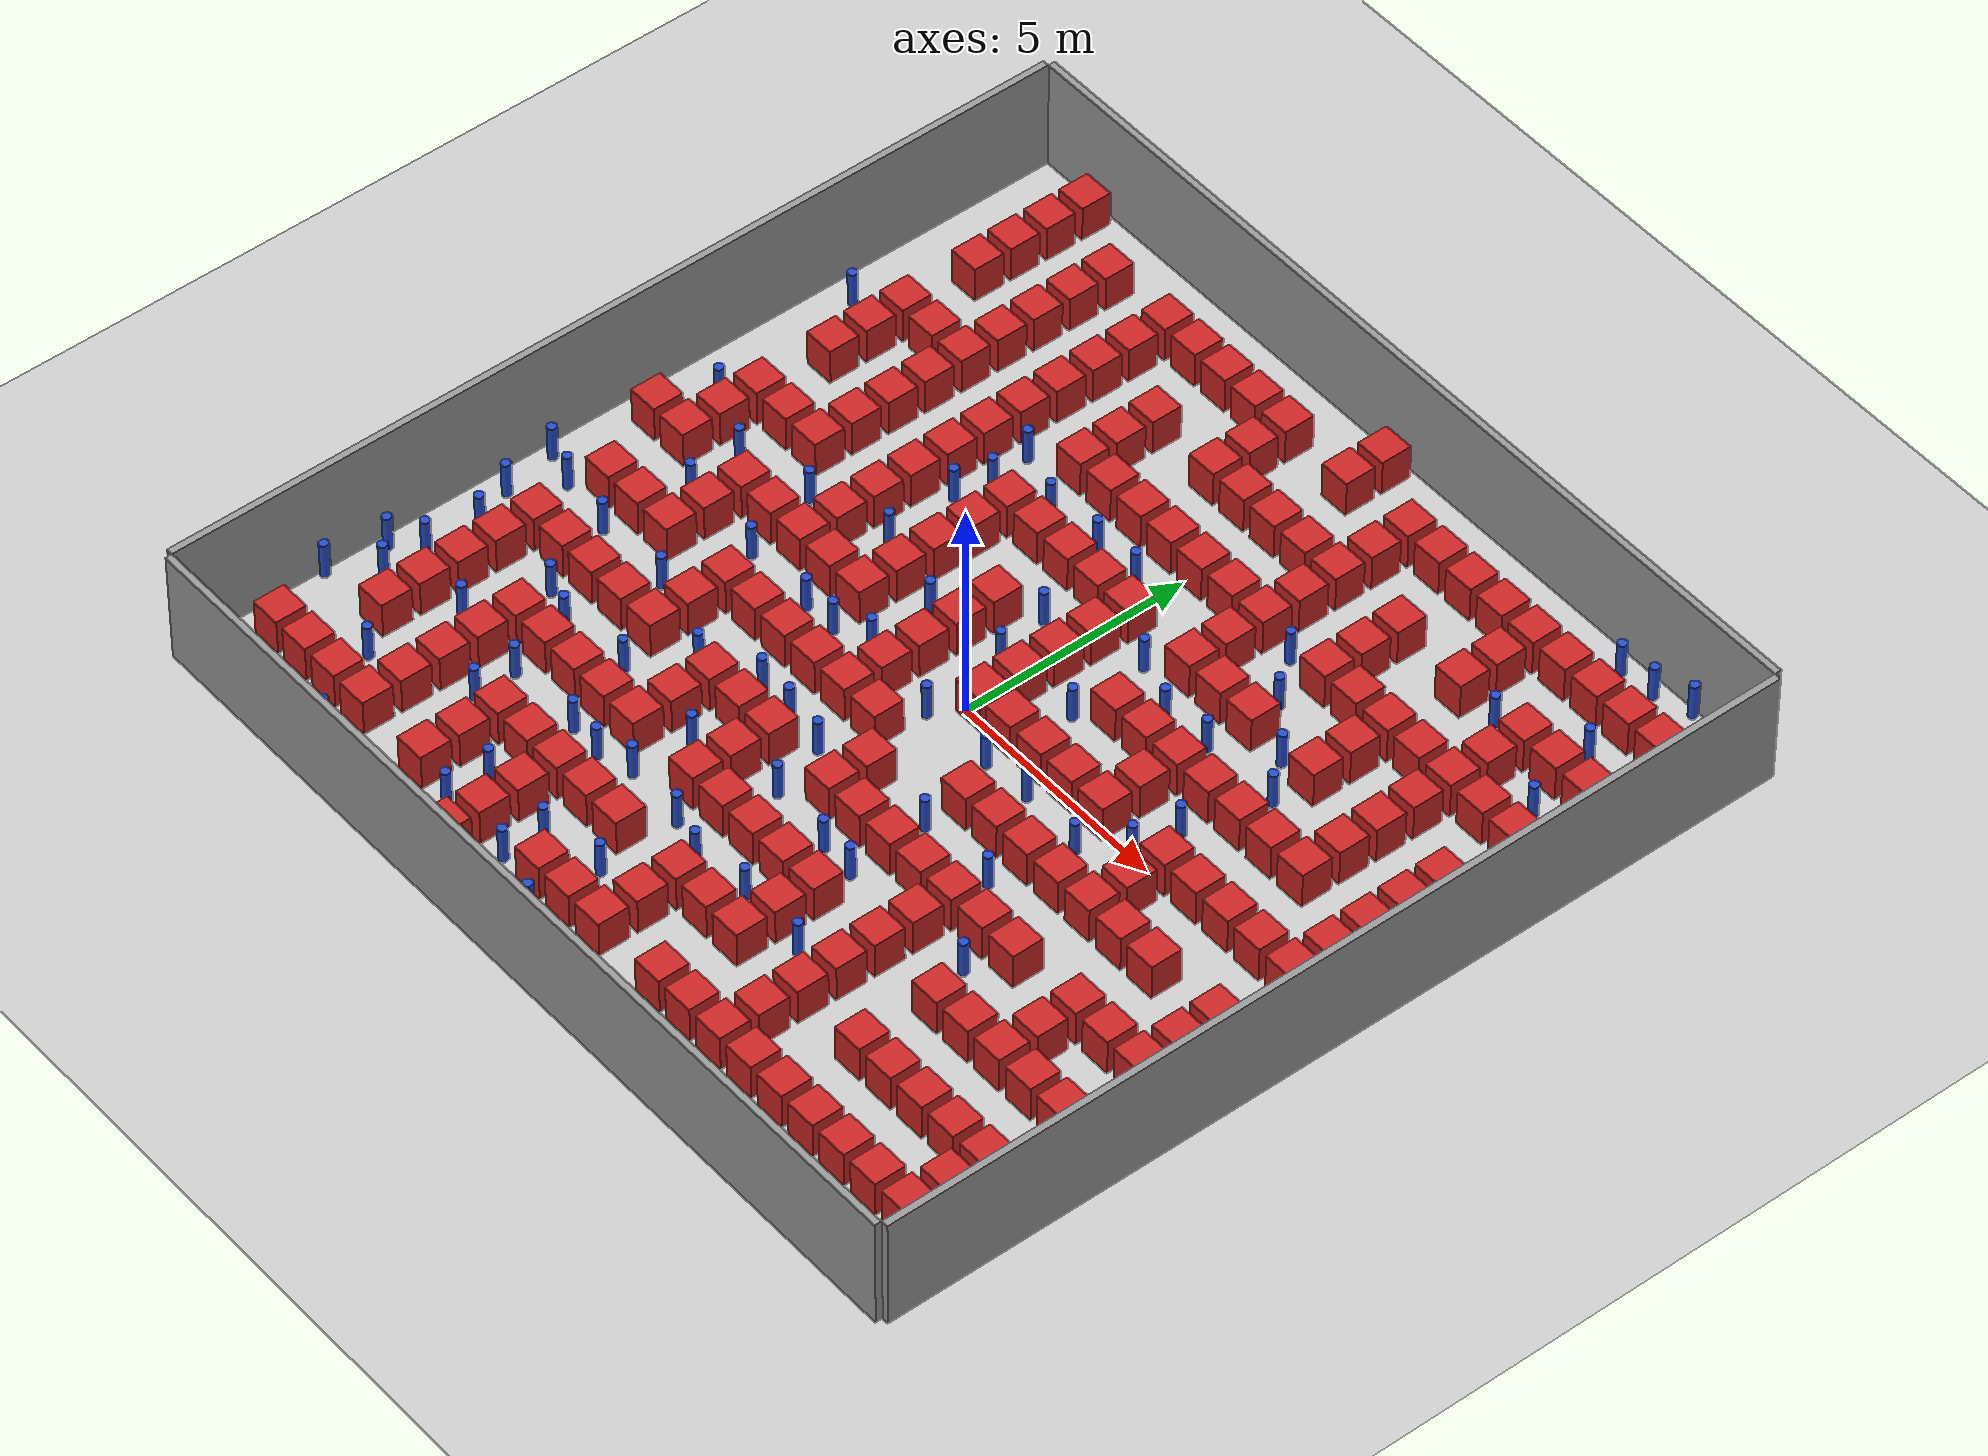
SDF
<sdf version="1.6">
 <world name="default">
  <light name="sun" type="directional">
   <pose>0 0 1000 0 -0 0</pose>
   <diffuse>0.8 0.8 0.8 1</diffuse>
   <specular>0.1 0.1 0.1 1</specular>
   <attenuation>
    <range>1000</range>
    <constant>0.9</constant>
    <linear>0.01</linear>
    <quadratic>0.001</quadratic>
   </attenuation>
   <direction>-0.5 0.5 -1</direction>
  </light>
  <model name="ground_plane">
   <static>1</static>
   <link name="link">
    <collision name="collision">
     <geometry><plane><normal>0 0 1</normal><size>100 100</size></plane></geometry>
     <surface><friction><ode><mu>100</mu><mu2>50</mu2></ode></friction></surface>
    </collision>
    <visual name="visual">
     <cast_shadows>0</cast_shadows>
     <geometry><plane><normal>0 0 1</normal><size>100 100</size></plane></geometry>
     <material>
      <script><uri>file://media/materials/scripts/gazebo.material</uri><name>Gazebo/Grey</name></script>
     </material>
    </visual>
   </link>
  </model>
  <gravity>0 0 -9.8</gravity>
  <magnetic_field>6e-06 2.3e-05 -4.2e-05</magnetic_field>
  <atmosphere type="adiabatic"/>
  <physics name="default_physics" default="0" type="ode">
   <max_step_size>0.001</max_step_size>
   <real_time_factor>1</real_time_factor>
   <real_time_update_rate>1000</real_time_update_rate>
  </physics>
  <scene><ambient>0.4 0.4 0.4 1</ambient><background>0.7 0.7 0.7 1</background><shadows>1</shadows></scene>
  <spherical_coordinates>
   <surface_model>EARTH_WGS84</surface_model>
   <latitude_deg>0</latitude_deg>
   <longitude_deg>0</longitude_deg>
   <elevation>0</elevation>
   <heading_deg>0</heading_deg>
  </spherical_coordinates>
  <model name="NamedLocations"><static>1</static><link name="DefaultStart"/></model>
  <model name="20x20_walls">
   <pose>0.044518 0.0261 0 0 -0 0</pose>
   <link name="Wall_1">
    <collision name="Wall_1_Collision">
     <geometry><box><size>20 0.15 2.5</size></box></geometry>
     <pose>0 0 1.25 0 -0 0</pose>
    </collision>
    <visual name="Wall_1_Visual">
     <pose>0 0 1.25 0 -0 0</pose>
     <geometry><box><size>20 0.15 2.5</size></box></geometry>
     <material>
      <script><uri>file://media/materials/scripts/gazebo.material</uri><name>Gazebo/Grey</name></script>
      <ambient>0.976471 0.992157 1 1</ambient>
     </material>
     <meta><layer>0</layer></meta>
    </visual>
    <pose>0 10.075 0 0 -0 0</pose>
   </link>
   <link name="Wall_3">
    <collision name="Wall_3_Collision">
     <geometry><box><size>20 0.15 2.5</size></box></geometry>
     <pose>0 0 1.25 0 -0 0</pose>
    </collision>
    <visual name="Wall_3_Visual">
     <pose>0 0 1.25 0 -0 0</pose>
     <geometry><box><size>20 0.15 2.5</size></box></geometry>
     <material>
      <script><uri>file://media/materials/scripts/gazebo.material</uri><name>Gazebo/Grey</name></script>
      <ambient>0.976471 0.992157 1 1</ambient>
     </material>
     <meta><layer>0</layer></meta>
    </visual>
    <pose>10.075 0 0 0 0 -1.5708</pose>
   </link>
   <link name="Wall_4">
    <collision name="Wall_4_Collision">
     <geometry><box><size>20 0.15 2.5</size></box></geometry>
     <pose>0 0 1.25 0 -0 0</pose>
    </collision>
    <visual name="Wall_4_Visual">
     <pose>0 0 1.25 0 -0 0</pose>
     <geometry><box><size>20 0.15 2.5</size></box></geometry>
     <material>
      <script><uri>file://media/materials/scripts/gazebo.material</uri><name>Gazebo/Grey</name></script>
      <ambient>0.976471 0.992157 1 1</ambient>
     </material>
     <meta><layer>0</layer></meta>
    </visual>
    <pose>0 -10.075 0 0 -0 3.14159</pose>
   </link>
   <link name="Wall_5">
    <collision name="Wall_5_Collision">
     <geometry><box><size>20 0.15 2.5</size></box></geometry>
     <pose>0 0 1.25 0 -0 0</pose>
    </collision>
    <visual name="Wall_5_Visual">
     <pose>0 0 1.25 0 -0 0</pose>
     <geometry><box><size>20 0.15 2.5</size></box></geometry>
     <material>
      <script><uri>file://media/materials/scripts/gazebo.material</uri><name>Gazebo/Grey</name></script>
      <ambient>0.976471 0.992157 1 1</ambient>
     </material>
     <meta><layer>0</layer></meta>
    </visual>
    <pose>-10.075 0 0 0 -0 1.5708</pose>
   </link>
   <static>1</static>
  </model>
  <model name="box_obstacle0">
   <static>0</static>
   <link name="link">
    <pose>0 0 0.1 0 -0 0</pose>
    <inertial>
     <mass>100</mass>
     <inertia>
      <ixx>0.166667</ixx>
      <ixy>0</ixy>
      <ixz>0</ixz>
      <iyy>0.166667</iyy>
      <iyz>0</iyz>
      <izz>0.166667</izz>
     </inertia>
    </inertial>
    <collision name="collision"><geometry><box><size>0.675 0.675 0.8</size></box></geometry></collision>
    <visual name="visual">
     <geometry><box><size>0.675 0.675 0.8</size></box></geometry>
     <material>
      <script><name>Gazebo/Red</name><uri>file://media/materials/scripts/gazebo.material</uri></script>
     </material>
    </visual>
   </link>
   <pose>-9.15097 -8.30135 0.299996 4e-06 -0 0.001125</pose>
  </model>
  <model name="box_obstacle1">
   <static>0</static>
   <link name="link">
    <pose>0 0 0.1 0 -0 0</pose>
    <inertial>
     <mass>100</mass>
     <inertia>
      <ixx>0.166667</ixx>
      <ixy>0</ixy>
      <ixz>0</ixz>
      <iyy>0.166667</iyy>
      <iyz>0</iyz>
      <izz>0.166667</izz>
     </inertia>
    </inertial>
    <collision name="collision"><geometry><box><size>0.675 0.675 0.8</size></box></geometry></collision>
    <visual name="visual">
     <geometry><box><size>0.675 0.675 0.8</size></box></geometry>
     <material>
      <script><name>Gazebo/Red</name><uri>file://media/materials/scripts/gazebo.material</uri></script>
     </material>
    </visual>
   </link>
   <pose>-9.15097 0.19865 0.299996 4e-06 -0 0.001125</pose>
  </model>
  <model name="box_obstacle2">
   <static>0</static>
   <link name="link">
    <pose>0 0 0.1 0 -0 0</pose>
    <inertial>
     <mass>100</mass>
     <inertia>
      <ixx>0.166667</ixx>
      <ixy>0</ixy>
      <ixz>0</ixz>
      <iyy>0.166667</iyy>
      <iyz>0</iyz>
      <izz>0.166667</izz>
     </inertia>
    </inertial>
    <collision name="collision"><geometry><box><size>0.675 0.675 0.8</size></box></geometry></collision>
    <visual name="visual">
     <geometry><box><size>0.675 0.675 0.8</size></box></geometry>
     <material>
      <script><name>Gazebo/Red</name><uri>file://media/materials/scripts/gazebo.material</uri></script>
     </material>
    </visual>
   </link>
   <pose>-8.30097 -8.30135 0.299996 4e-06 -0 0.001125</pose>
  </model>
  <model name="box_obstacle3">
   <static>0</static>
   <link name="link">
    <pose>0 0 0.1 0 -0 0</pose>
    <inertial>
     <mass>100</mass>
     <inertia>
      <ixx>0.166667</ixx>
      <ixy>0</ixy>
      <ixz>0</ixz>
      <iyy>0.166667</iyy>
      <iyz>0</iyz>
      <izz>0.166667</izz>
     </inertia>
    </inertial>
    <collision name="collision"><geometry><box><size>0.675 0.675 0.8</size></box></geometry></collision>
    <visual name="visual">
     <geometry><box><size>0.675 0.675 0.8</size></box></geometry>
     <material>
      <script><name>Gazebo/Red</name><uri>file://media/materials/scripts/gazebo.material</uri></script>
     </material>
    </visual>
   </link>
   <pose>-8.30097 -6.60135 0.299996 4e-06 -0 0.001125</pose>
  </model>
  <model name="box_obstacle4">
   <static>0</static>
   <link name="link">
    <pose>0 0 0.1 0 -0 0</pose>
    <inertial>
     <mass>100</mass>
     <inertia>
      <ixx>0.166667</ixx>
      <ixy>0</ixy>
      <ixz>0</ixz>
      <iyy>0.166667</iyy>
      <iyz>0</iyz>
      <izz>0.166667</izz>
     </inertia>
    </inertial>
    <collision name="collision"><geometry><box><size>0.675 0.675 0.8</size></box></geometry></collision>
    <visual name="visual">
     <geometry><box><size>0.675 0.675 0.8</size></box></geometry>
     <material>
      <script><name>Gazebo/Red</name><uri>file://media/materials/scripts/gazebo.material</uri></script>
     </material>
    </visual>
   </link>
   <pose>-8.30097 -5.75135 0.299996 4e-06 -0 0.001125</pose>
  </model>
  <model name="box_obstacle5">
   <static>0</static>
   <link name="link">
    <pose>0 0 0.1 0 -0 0</pose>
    <inertial>
     <mass>100</mass>
     <inertia>
      <ixx>0.166667</ixx>
      <ixy>0</ixy>
      <ixz>0</ixz>
      <iyy>0.166667</iyy>
      <iyz>0</iyz>
      <izz>0.166667</izz>
     </inertia>
    </inertial>
    <collision name="collision"><geometry><box><size>0.675 0.675 0.8</size></box></geometry></collision>
    <visual name="visual">
     <geometry><box><size>0.675 0.675 0.8</size></box></geometry>
     <material>
      <script><name>Gazebo/Red</name><uri>file://media/materials/scripts/gazebo.material</uri></script>
     </material>
    </visual>
   </link>
   <pose>-8.30097 -4.90135 0.299996 4e-06 -0 0.001125</pose>
  </model>
  <model name="box_obstacle6">
   <static>0</static>
   <link name="link">
    <pose>0 0 0.1 0 -0 0</pose>
    <inertial>
     <mass>100</mass>
     <inertia>
      <ixx>0.166667</ixx>
      <ixy>0</ixy>
      <ixz>0</ixz>
      <iyy>0.166667</iyy>
      <iyz>0</iyz>
      <izz>0.166667</izz>
     </inertia>
    </inertial>
    <collision name="collision"><geometry><box><size>0.675 0.675 0.8</size></box></geometry></collision>
    <visual name="visual">
     <geometry><box><size>0.675 0.675 0.8</size></box></geometry>
     <material>
      <script><name>Gazebo/Red</name><uri>file://media/materials/scripts/gazebo.material</uri></script>
     </material>
    </visual>
   </link>
   <pose>-8.30097 -4.05135 0.299996 4e-06 -0 0.001125</pose>
  </model>
  <model name="box_obstacle7">
   <static>0</static>
   <link name="link">
    <pose>0 0 0.1 0 -0 0</pose>
    <inertial>
     <mass>100</mass>
     <inertia>
      <ixx>0.166667</ixx>
      <ixy>0</ixy>
      <ixz>0</ixz>
      <iyy>0.166667</iyy>
      <iyz>0</iyz>
      <izz>0.166667</izz>
     </inertia>
    </inertial>
    <collision name="collision"><geometry><box><size>0.675 0.675 0.8</size></box></geometry></collision>
    <visual name="visual">
     <geometry><box><size>0.675 0.675 0.8</size></box></geometry>
     <material>
      <script><name>Gazebo/Red</name><uri>file://media/materials/scripts/gazebo.material</uri></script>
     </material>
    </visual>
   </link>
   <pose>-8.30097 -3.20135 0.299996 4e-06 -0 0.001125</pose>
  </model>
  <model name="box_obstacle8">
   <static>0</static>
   <link name="link">
    <pose>0 0 0.1 0 -0 0</pose>
    <inertial>
     <mass>100</mass>
     <inertia>
      <ixx>0.166667</ixx>
      <ixy>0</ixy>
      <ixz>0</ixz>
      <iyy>0.166667</iyy>
      <iyz>0</iyz>
      <izz>0.166667</izz>
     </inertia>
    </inertial>
    <collision name="collision"><geometry><box><size>0.675 0.675 0.8</size></box></geometry></collision>
    <visual name="visual">
     <geometry><box><size>0.675 0.675 0.8</size></box></geometry>
     <material>
      <script><name>Gazebo/Red</name><uri>file://media/materials/scripts/gazebo.material</uri></script>
     </material>
    </visual>
   </link>
   <pose>-8.30097 -1.50135 0.299996 4e-06 -0 0.001125</pose>
  </model>
  <model name="box_obstacle9">
   <static>0</static>
   <link name="link">
    <pose>0 0 0.1 0 -0 0</pose>
    <inertial>
     <mass>100</mass>
     <inertia>
      <ixx>0.166667</ixx>
      <ixy>0</ixy>
      <ixz>0</ixz>
      <iyy>0.166667</iyy>
      <iyz>0</iyz>
      <izz>0.166667</izz>
     </inertia>
    </inertial>
    <collision name="collision"><geometry><box><size>0.675 0.675 0.8</size></box></geometry></collision>
    <visual name="visual">
     <geometry><box><size>0.675 0.675 0.8</size></box></geometry>
     <material>
      <script><name>Gazebo/Red</name><uri>file://media/materials/scripts/gazebo.material</uri></script>
     </material>
    </visual>
   </link>
   <pose>-8.30097 0.19865 0.299996 4e-06 -0 0.001125</pose>
  </model>
  <model name="box_obstacle10">
   <static>0</static>
   <link name="link">
    <pose>0 0 0.1 0 -0 0</pose>
    <inertial>
     <mass>100</mass>
     <inertia>
      <ixx>0.166667</ixx>
      <ixy>0</ixy>
      <ixz>0</ixz>
      <iyy>0.166667</iyy>
      <iyz>0</iyz>
      <izz>0.166667</izz>
     </inertia>
    </inertial>
    <collision name="collision"><geometry><box><size>0.675 0.675 0.8</size></box></geometry></collision>
    <visual name="visual">
     <geometry><box><size>0.675 0.675 0.8</size></box></geometry>
     <material>
      <script><name>Gazebo/Red</name><uri>file://media/materials/scripts/gazebo.material</uri></script>
     </material>
    </visual>
   </link>
   <pose>-8.30097 1.04865 0.299996 4e-06 -0 0.001125</pose>
  </model>
  <model name="box_obstacle11">
   <static>0</static>
   <link name="link">
    <pose>0 0 0.1 0 -0 0</pose>
    <inertial>
     <mass>100</mass>
     <inertia>
      <ixx>0.166667</ixx>
      <ixy>0</ixy>
      <ixz>0</ixz>
      <iyy>0.166667</iyy>
      <iyz>0</iyz>
      <izz>0.166667</izz>
     </inertia>
    </inertial>
    <collision name="collision"><geometry><box><size>0.675 0.675 0.8</size></box></geometry></collision>
    <visual name="visual">
     <geometry><box><size>0.675 0.675 0.8</size></box></geometry>
     <material>
      <script><name>Gazebo/Red</name><uri>file://media/materials/scripts/gazebo.material</uri></script>
     </material>
    </visual>
   </link>
   <pose>-8.30097 1.89865 0.299996 4e-06 -0 0.001125</pose>
  </model>
  <model name="box_obstacle12">
   <static>0</static>
   <link name="link">
    <pose>0 0 0.1 0 -0 0</pose>
    <inertial>
     <mass>100</mass>
     <inertia>
      <ixx>0.166667</ixx>
      <ixy>0</ixy>
      <ixz>0</ixz>
      <iyy>0.166667</iyy>
      <iyz>0</iyz>
      <izz>0.166667</izz>
     </inertia>
    </inertial>
    <collision name="collision"><geometry><box><size>0.675 0.675 0.8</size></box></geometry></collision>
    <visual name="visual">
     <geometry><box><size>0.675 0.675 0.8</size></box></geometry>
     <material>
      <script><name>Gazebo/Red</name><uri>file://media/materials/scripts/gazebo.material</uri></script>
     </material>
    </visual>
   </link>
   <pose>-8.30097 3.59865 0.299996 4e-06 -0 0.001125</pose>
  </model>
  <model name="box_obstacle13">
   <static>0</static>
   <link name="link">
    <pose>0 0 0.1 0 -0 0</pose>
    <inertial>
     <mass>100</mass>
     <inertia>
      <ixx>0.166667</ixx>
      <ixy>0</ixy>
      <ixz>0</ixz>
      <iyy>0.166667</iyy>
      <iyz>0</iyz>
      <izz>0.166667</izz>
     </inertia>
    </inertial>
    <collision name="collision"><geometry><box><size>0.675 0.675 0.8</size></box></geometry></collision>
    <visual name="visual">
     <geometry><box><size>0.675 0.675 0.8</size></box></geometry>
     <material>
      <script><name>Gazebo/Red</name><uri>file://media/materials/scripts/gazebo.material</uri></script>
     </material>
    </visual>
   </link>
   <pose>-8.30097 4.44865 0.299996 4e-06 -0 0.001125</pose>
  </model>
  <model name="box_obstacle14">
   <static>0</static>
   <link name="link">
    <pose>0 0 0.1 0 -0 0</pose>
    <inertial>
     <mass>100</mass>
     <inertia>
      <ixx>0.166667</ixx>
      <ixy>0</ixy>
      <ixz>0</ixz>
      <iyy>0.166667</iyy>
      <iyz>0</iyz>
      <izz>0.166667</izz>
     </inertia>
    </inertial>
    <collision name="collision"><geometry><box><size>0.675 0.675 0.8</size></box></geometry></collision>
    <visual name="visual">
     <geometry><box><size>0.675 0.675 0.8</size></box></geometry>
     <material>
      <script><name>Gazebo/Red</name><uri>file://media/materials/scripts/gazebo.material</uri></script>
     </material>
    </visual>
   </link>
   <pose>-8.30097 5.29865 0.299996 4e-06 -0 0.001125</pose>
  </model>
  <model name="box_obstacle15">
   <static>0</static>
   <link name="link">
    <pose>0 0 0.1 0 -0 0</pose>
    <inertial>
     <mass>100</mass>
     <inertia>
      <ixx>0.166667</ixx>
      <ixy>0</ixy>
      <ixz>0</ixz>
      <iyy>0.166667</iyy>
      <iyz>0</iyz>
      <izz>0.166667</izz>
     </inertia>
    </inertial>
    <collision name="collision"><geometry><box><size>0.675 0.675 0.8</size></box></geometry></collision>
    <visual name="visual">
     <geometry><box><size>0.675 0.675 0.8</size></box></geometry>
     <material>
      <script><name>Gazebo/Red</name><uri>file://media/materials/scripts/gazebo.material</uri></script>
     </material>
    </visual>
   </link>
   <pose>-8.30097 6.99865 0.299996 4e-06 -0 0.001125</pose>
  </model>
  <model name="box_obstacle16">
   <static>0</static>
   <link name="link">
    <pose>0 0 0.1 0 -0 0</pose>
    <inertial>
     <mass>100</mass>
     <inertia>
      <ixx>0.166667</ixx>
      <ixy>0</ixy>
      <ixz>0</ixz>
      <iyy>0.166667</iyy>
      <iyz>0</iyz>
      <izz>0.166667</izz>
     </inertia>
    </inertial>
    <collision name="collision"><geometry><box><size>0.675 0.675 0.8</size></box></geometry></collision>
    <visual name="visual">
     <geometry><box><size>0.675 0.675 0.8</size></box></geometry>
     <material>
      <script><name>Gazebo/Red</name><uri>file://media/materials/scripts/gazebo.material</uri></script>
     </material>
    </visual>
   </link>
   <pose>-8.30097 7.84865 0.299996 4e-06 -0 0.001125</pose>
  </model>
  <model name="box_obstacle17">
   <static>0</static>
   <link name="link">
    <pose>0 0 0.1 0 -0 0</pose>
    <inertial>
     <mass>100</mass>
     <inertia>
      <ixx>0.166667</ixx>
      <ixy>0</ixy>
      <ixz>0</ixz>
      <iyy>0.166667</iyy>
      <iyz>0</iyz>
      <izz>0.166667</izz>
     </inertia>
    </inertial>
    <collision name="collision"><geometry><box><size>0.675 0.675 0.8</size></box></geometry></collision>
    <visual name="visual">
     <geometry><box><size>0.675 0.675 0.8</size></box></geometry>
     <material>
      <script><name>Gazebo/Red</name><uri>file://media/materials/scripts/gazebo.material</uri></script>
     </material>
    </visual>
   </link>
   <pose>-8.30097 8.69865 0.299996 4e-06 -0 0.001125</pose>
  </model>
  <model name="box_obstacle18">
   <static>0</static>
   <link name="link">
    <pose>0 0 0.1 0 -0 0</pose>
    <inertial>
     <mass>100</mass>
     <inertia>
      <ixx>0.166667</ixx>
      <ixy>0</ixy>
      <ixz>0</ixz>
      <iyy>0.166667</iyy>
      <iyz>0</iyz>
      <izz>0.166667</izz>
     </inertia>
    </inertial>
    <collision name="collision"><geometry><box><size>0.675 0.675 0.8</size></box></geometry></collision>
    <visual name="visual">
     <geometry><box><size>0.675 0.675 0.8</size></box></geometry>
     <material>
      <script><name>Gazebo/Red</name><uri>file://media/materials/scripts/gazebo.material</uri></script>
     </material>
    </visual>
   </link>
   <pose>-8.30097 9.54865 0.299996 4e-06 -0 0.001125</pose>
  </model>
  <model name="box_obstacle19">
   <static>0</static>
   <link name="link">
    <pose>0 0 0.1 0 -0 0</pose>
    <inertial>
     <mass>100</mass>
     <inertia>
      <ixx>0.166667</ixx>
      <ixy>0</ixy>
      <ixz>0</ixz>
      <iyy>0.166667</iyy>
      <iyz>0</iyz>
      <izz>0.166667</izz>
     </inertia>
    </inertial>
    <collision name="collision"><geometry><box><size>0.675 0.675 0.8</size></box></geometry></collision>
    <visual name="visual">
     <geometry><box><size>0.675 0.675 0.8</size></box></geometry>
     <material>
      <script><name>Gazebo/Red</name><uri>file://media/materials/scripts/gazebo.material</uri></script>
     </material>
    </visual>
   </link>
   <pose>-7.45097 -8.30135 0.299996 4e-06 -0 0.001125</pose>
  </model>
  <model name="box_obstacle20">
   <static>0</static>
   <link name="link">
    <pose>0 0 0.1 0 -0 0</pose>
    <inertial>
     <mass>100</mass>
     <inertia>
      <ixx>0.166667</ixx>
      <ixy>0</ixy>
      <ixz>0</ixz>
      <iyy>0.166667</iyy>
      <iyz>0</iyz>
      <izz>0.166667</izz>
     </inertia>
    </inertial>
    <collision name="collision"><geometry><box><size>0.675 0.675 0.8</size></box></geometry></collision>
    <visual name="visual">
     <geometry><box><size>0.675 0.675 0.8</size></box></geometry>
     <material>
      <script><name>Gazebo/Red</name><uri>file://media/materials/scripts/gazebo.material</uri></script>
     </material>
    </visual>
   </link>
   <pose>-7.45097 -3.20135 0.299996 4e-06 -0 0.001125</pose>
  </model>
  <model name="box_obstacle21">
   <static>0</static>
   <link name="link">
    <pose>0 0 0.1 0 -0 0</pose>
    <inertial>
     <mass>100</mass>
     <inertia>
      <ixx>0.166667</ixx>
      <ixy>0</ixy>
      <ixz>0</ixz>
      <iyy>0.166667</iyy>
      <iyz>0</iyz>
      <izz>0.166667</izz>
     </inertia>
    </inertial>
    <collision name="collision"><geometry><box><size>0.675 0.675 0.8</size></box></geometry></collision>
    <visual name="visual">
     <geometry><box><size>0.675 0.675 0.8</size></box></geometry>
     <material>
      <script><name>Gazebo/Red</name><uri>file://media/materials/scripts/gazebo.material</uri></script>
     </material>
    </visual>
   </link>
   <pose>-7.45097 -1.50135 0.299996 4e-06 -0 0.001125</pose>
  </model>
  <model name="box_obstacle22">
   <static>0</static>
   <link name="link">
    <pose>0 0 0.1 0 -0 0</pose>
    <inertial>
     <mass>100</mass>
     <inertia>
      <ixx>0.166667</ixx>
      <ixy>0</ixy>
      <ixz>0</ixz>
      <iyy>0.166667</iyy>
      <iyz>0</iyz>
      <izz>0.166667</izz>
     </inertia>
    </inertial>
    <collision name="collision"><geometry><box><size>0.675 0.675 0.8</size></box></geometry></collision>
    <visual name="visual">
     <geometry><box><size>0.675 0.675 0.8</size></box></geometry>
     <material>
      <script><name>Gazebo/Red</name><uri>file://media/materials/scripts/gazebo.material</uri></script>
     </material>
    </visual>
   </link>
   <pose>-7.45097 1.89865 0.299996 4e-06 -0 0.001125</pose>
  </model>
  <model name="box_obstacle23">
   <static>0</static>
   <link name="link">
    <pose>0 0 0.1 0 -0 0</pose>
    <inertial>
     <mass>100</mass>
     <inertia>
      <ixx>0.166667</ixx>
      <ixy>0</ixy>
      <ixz>0</ixz>
      <iyy>0.166667</iyy>
      <iyz>0</iyz>
      <izz>0.166667</izz>
     </inertia>
    </inertial>
    <collision name="collision"><geometry><box><size>0.675 0.675 0.8</size></box></geometry></collision>
    <visual name="visual">
     <geometry><box><size>0.675 0.675 0.8</size></box></geometry>
     <material>
      <script><name>Gazebo/Red</name><uri>file://media/materials/scripts/gazebo.material</uri></script>
     </material>
    </visual>
   </link>
   <pose>-7.45097 5.29865 0.299996 4e-06 -0 0.001125</pose>
  </model>
  <model name="box_obstacle24">
   <static>0</static>
   <link name="link">
    <pose>0 0 0.1 0 -0 0</pose>
    <inertial>
     <mass>100</mass>
     <inertia>
      <ixx>0.166667</ixx>
      <ixy>0</ixy>
      <ixz>0</ixz>
      <iyy>0.166667</iyy>
      <iyz>0</iyz>
      <izz>0.166667</izz>
     </inertia>
    </inertial>
    <collision name="collision"><geometry><box><size>0.675 0.675 0.8</size></box></geometry></collision>
    <visual name="visual">
     <geometry><box><size>0.675 0.675 0.8</size></box></geometry>
     <material>
      <script><name>Gazebo/Red</name><uri>file://media/materials/scripts/gazebo.material</uri></script>
     </material>
    </visual>
   </link>
   <pose>-6.60097 -8.30135 0.299996 4e-06 -0 0.001125</pose>
  </model>
  <model name="box_obstacle25">
   <static>0</static>
   <link name="link">
    <pose>0 0 0.1 0 -0 0</pose>
    <inertial>
     <mass>100</mass>
     <inertia>
      <ixx>0.166667</ixx>
      <ixy>0</ixy>
      <ixz>0</ixz>
      <iyy>0.166667</iyy>
      <iyz>0</iyz>
      <izz>0.166667</izz>
     </inertia>
    </inertial>
    <collision name="collision"><geometry><box><size>0.675 0.675 0.8</size></box></geometry></collision>
    <visual name="visual">
     <geometry><box><size>0.675 0.675 0.8</size></box></geometry>
     <material>
      <script><name>Gazebo/Red</name><uri>file://media/materials/scripts/gazebo.material</uri></script>
     </material>
    </visual>
   </link>
   <pose>-6.60097 -7.45135 0.299996 4e-06 -0 0.001125</pose>
  </model>
  <model name="box_obstacle26">
   <static>0</static>
   <link name="link">
    <pose>0 0 0.1 0 -0 0</pose>
    <inertial>
     <mass>100</mass>
     <inertia>
      <ixx>0.166667</ixx>
      <ixy>0</ixy>
      <ixz>0</ixz>
      <iyy>0.166667</iyy>
      <iyz>0</iyz>
      <izz>0.166667</izz>
     </inertia>
    </inertial>
    <collision name="collision"><geometry><box><size>0.675 0.675 0.8</size></box></geometry></collision>
    <visual name="visual">
     <geometry><box><size>0.675 0.675 0.8</size></box></geometry>
     <material>
      <script><name>Gazebo/Red</name><uri>file://media/materials/scripts/gazebo.material</uri></script>
     </material>
    </visual>
   </link>
   <pose>-6.60097 -6.60135 0.299996 4e-06 -0 0.001125</pose>
  </model>
  <model name="box_obstacle27">
   <static>0</static>
   <link name="link">
    <pose>0 0 0.1 0 -0 0</pose>
    <inertial>
     <mass>100</mass>
     <inertia>
      <ixx>0.166667</ixx>
      <ixy>0</ixy>
      <ixz>0</ixz>
      <iyy>0.166667</iyy>
      <iyz>0</iyz>
      <izz>0.166667</izz>
     </inertia>
    </inertial>
    <collision name="collision"><geometry><box><size>0.675 0.675 0.8</size></box></geometry></collision>
    <visual name="visual">
     <geometry><box><size>0.675 0.675 0.8</size></box></geometry>
     <material>
      <script><name>Gazebo/Red</name><uri>file://media/materials/scripts/gazebo.material</uri></script>
     </material>
    </visual>
   </link>
   <pose>-6.60097 -5.75135 0.299996 4e-06 -0 0.001125</pose>
  </model>
  <model name="box_obstacle28">
   <static>0</static>
   <link name="link">
    <pose>0 0 0.1 0 -0 0</pose>
    <inertial>
     <mass>100</mass>
     <inertia>
      <ixx>0.166667</ixx>
      <ixy>0</ixy>
      <ixz>0</ixz>
      <iyy>0.166667</iyy>
      <iyz>0</iyz>
      <izz>0.166667</izz>
     </inertia>
    </inertial>
    <collision name="collision"><geometry><box><size>0.675 0.675 0.8</size></box></geometry></collision>
    <visual name="visual">
     <geometry><box><size>0.675 0.675 0.8</size></box></geometry>
     <material>
      <script><name>Gazebo/Red</name><uri>file://media/materials/scripts/gazebo.material</uri></script>
     </material>
    </visual>
   </link>
   <pose>-6.60097 -4.90135 0.299996 4e-06 -0 0.001125</pose>
  </model>
  <model name="box_obstacle29">
   <static>0</static>
   <link name="link">
    <pose>0 0 0.1 0 -0 0</pose>
    <inertial>
     <mass>100</mass>
     <inertia>
      <ixx>0.166667</ixx>
      <ixy>0</ixy>
      <ixz>0</ixz>
      <iyy>0.166667</iyy>
      <iyz>0</iyz>
      <izz>0.166667</izz>
     </inertia>
    </inertial>
    <collision name="collision"><geometry><box><size>0.675 0.675 0.8</size></box></geometry></collision>
    <visual name="visual">
     <geometry><box><size>0.675 0.675 0.8</size></box></geometry>
     <material>
      <script><name>Gazebo/Red</name><uri>file://media/materials/scripts/gazebo.material</uri></script>
     </material>
    </visual>
   </link>
   <pose>-6.60097 -3.20135 0.299996 4e-06 -0 0.001125</pose>
  </model>
  <model name="box_obstacle30">
   <static>0</static>
   <link name="link">
    <pose>0 0 0.1 0 -0 0</pose>
    <inertial>
     <mass>100</mass>
     <inertia>
      <ixx>0.166667</ixx>
      <ixy>0</ixy>
      <ixz>0</ixz>
      <iyy>0.166667</iyy>
      <iyz>0</iyz>
      <izz>0.166667</izz>
     </inertia>
    </inertial>
    <collision name="collision"><geometry><box><size>0.675 0.675 0.8</size></box></geometry></collision>
    <visual name="visual">
     <geometry><box><size>0.675 0.675 0.8</size></box></geometry>
     <material>
      <script><name>Gazebo/Red</name><uri>file://media/materials/scripts/gazebo.material</uri></script>
     </material>
    </visual>
   </link>
   <pose>-6.60097 -1.50135 0.299996 4e-06 -0 0.001125</pose>
  </model>
  <model name="box_obstacle31">
   <static>0</static>
   <link name="link">
    <pose>0 0 0.1 0 -0 0</pose>
    <inertial>
     <mass>100</mass>
     <inertia>
      <ixx>0.166667</ixx>
      <ixy>0</ixy>
      <ixz>0</ixz>
      <iyy>0.166667</iyy>
      <iyz>0</iyz>
      <izz>0.166667</izz>
     </inertia>
    </inertial>
    <collision name="collision"><geometry><box><size>0.675 0.675 0.8</size></box></geometry></collision>
    <visual name="visual">
     <geometry><box><size>0.675 0.675 0.8</size></box></geometry>
     <material>
      <script><name>Gazebo/Red</name><uri>file://media/materials/scripts/gazebo.material</uri></script>
     </material>
    </visual>
   </link>
   <pose>-6.60097 -0.65135 0.299996 4e-06 -0 0.001125</pose>
  </model>
  <model name="box_obstacle32">
   <static>0</static>
   <link name="link">
    <pose>0 0 0.1 0 -0 0</pose>
    <inertial>
     <mass>100</mass>
     <inertia>
      <ixx>0.166667</ixx>
      <ixy>0</ixy>
      <ixz>0</ixz>
      <iyy>0.166667</iyy>
      <iyz>0</iyz>
      <izz>0.166667</izz>
     </inertia>
    </inertial>
    <collision name="collision"><geometry><box><size>0.675 0.675 0.8</size></box></geometry></collision>
    <visual name="visual">
     <geometry><box><size>0.675 0.675 0.8</size></box></geometry>
     <material>
      <script><name>Gazebo/Red</name><uri>file://media/materials/scripts/gazebo.material</uri></script>
     </material>
    </visual>
   </link>
   <pose>-6.60097 0.19865 0.299996 4e-06 -0 0.001125</pose>
  </model>
  <model name="box_obstacle33">
   <static>0</static>
   <link name="link">
    <pose>0 0 0.1 0 -0 0</pose>
    <inertial>
     <mass>100</mass>
     <inertia>
      <ixx>0.166667</ixx>
      <ixy>0</ixy>
      <ixz>0</ixz>
      <iyy>0.166667</iyy>
      <iyz>0</iyz>
      <izz>0.166667</izz>
     </inertia>
    </inertial>
    <collision name="collision"><geometry><box><size>0.675 0.675 0.8</size></box></geometry></collision>
    <visual name="visual">
     <geometry><box><size>0.675 0.675 0.8</size></box></geometry>
     <material>
      <script><name>Gazebo/Red</name><uri>file://media/materials/scripts/gazebo.material</uri></script>
     </material>
    </visual>
   </link>
   <pose>-6.60097 1.89865 0.299996 4e-06 -0 0.001125</pose>
  </model>
  <model name="box_obstacle34">
   <static>0</static>
   <link name="link">
    <pose>0 0 0.1 0 -0 0</pose>
    <inertial>
     <mass>100</mass>
     <inertia>
      <ixx>0.166667</ixx>
      <ixy>0</ixy>
      <ixz>0</ixz>
      <iyy>0.166667</iyy>
      <iyz>0</iyz>
      <izz>0.166667</izz>
     </inertia>
    </inertial>
    <collision name="collision"><geometry><box><size>0.675 0.675 0.8</size></box></geometry></collision>
    <visual name="visual">
     <geometry><box><size>0.675 0.675 0.8</size></box></geometry>
     <material>
      <script><name>Gazebo/Red</name><uri>file://media/materials/scripts/gazebo.material</uri></script>
     </material>
    </visual>
   </link>
   <pose>-6.60097 2.74865 0.299996 4e-06 -0 0.001125</pose>
  </model>
  <model name="box_obstacle35">
   <static>0</static>
   <link name="link">
    <pose>0 0 0.1 0 -0 0</pose>
    <inertial>
     <mass>100</mass>
     <inertia>
      <ixx>0.166667</ixx>
      <ixy>0</ixy>
      <ixz>0</ixz>
      <iyy>0.166667</iyy>
      <iyz>0</iyz>
      <izz>0.166667</izz>
     </inertia>
    </inertial>
    <collision name="collision"><geometry><box><size>0.675 0.675 0.8</size></box></geometry></collision>
    <visual name="visual">
     <geometry><box><size>0.675 0.675 0.8</size></box></geometry>
     <material>
      <script><name>Gazebo/Red</name><uri>file://media/materials/scripts/gazebo.material</uri></script>
     </material>
    </visual>
   </link>
   <pose>-6.60097 3.59865 0.299996 4e-06 -0 0.001125</pose>
  </model>
  <model name="box_obstacle36">
   <static>0</static>
   <link name="link">
    <pose>0 0 0.1 0 -0 0</pose>
    <inertial>
     <mass>100</mass>
     <inertia>
      <ixx>0.166667</ixx>
      <ixy>0</ixy>
      <ixz>0</ixz>
      <iyy>0.166667</iyy>
      <iyz>0</iyz>
      <izz>0.166667</izz>
     </inertia>
    </inertial>
    <collision name="collision"><geometry><box><size>0.675 0.675 0.8</size></box></geometry></collision>
    <visual name="visual">
     <geometry><box><size>0.675 0.675 0.8</size></box></geometry>
     <material>
      <script><name>Gazebo/Red</name><uri>file://media/materials/scripts/gazebo.material</uri></script>
     </material>
    </visual>
   </link>
   <pose>-6.60097 4.44865 0.299996 4e-06 -0 0.001125</pose>
  </model>
  <model name="box_obstacle37">
   <static>0</static>
   <link name="link">
    <pose>0 0 0.1 0 -0 0</pose>
    <inertial>
     <mass>100</mass>
     <inertia>
      <ixx>0.166667</ixx>
      <ixy>0</ixy>
      <ixz>0</ixz>
      <iyy>0.166667</iyy>
      <iyz>0</iyz>
      <izz>0.166667</izz>
     </inertia>
    </inertial>
    <collision name="collision"><geometry><box><size>0.675 0.675 0.8</size></box></geometry></collision>
    <visual name="visual">
     <geometry><box><size>0.675 0.675 0.8</size></box></geometry>
     <material>
      <script><name>Gazebo/Red</name><uri>file://media/materials/scripts/gazebo.material</uri></script>
     </material>
    </visual>
   </link>
   <pose>-6.60097 5.29865 0.299996 4e-06 -0 0.001125</pose>
  </model>
  <model name="box_obstacle38">
   <static>0</static>
   <link name="link">
    <pose>0 0 0.1 0 -0 0</pose>
    <inertial>
     <mass>100</mass>
     <inertia>
      <ixx>0.166667</ixx>
      <ixy>0</ixy>
      <ixz>0</ixz>
      <iyy>0.166667</iyy>
      <iyz>0</iyz>
      <izz>0.166667</izz>
     </inertia>
    </inertial>
    <collision name="collision"><geometry><box><size>0.675 0.675 0.8</size></box></geometry></collision>
    <visual name="visual">
     <geometry><box><size>0.675 0.675 0.8</size></box></geometry>
     <material>
      <script><name>Gazebo/Red</name><uri>file://media/materials/scripts/gazebo.material</uri></script>
     </material>
    </visual>
   </link>
   <pose>-6.60097 6.14865 0.299996 4e-06 -0 0.001125</pose>
  </model>
  <model name="box_obstacle39">
   <static>0</static>
   <link name="link">
    <pose>0 0 0.1 0 -0 0</pose>
    <inertial>
     <mass>100</mass>
     <inertia>
      <ixx>0.166667</ixx>
      <ixy>0</ixy>
      <ixz>0</ixz>
      <iyy>0.166667</iyy>
      <iyz>0</iyz>
      <izz>0.166667</izz>
     </inertia>
    </inertial>
    <collision name="collision"><geometry><box><size>0.675 0.675 0.8</size></box></geometry></collision>
    <visual name="visual">
     <geometry><box><size>0.675 0.675 0.8</size></box></geometry>
     <material>
      <script><name>Gazebo/Red</name><uri>file://media/materials/scripts/gazebo.material</uri></script>
     </material>
    </visual>
   </link>
   <pose>-6.60097 6.99865 0.299996 4e-06 -0 0.001125</pose>
  </model>
  <model name="box_obstacle40">
   <static>0</static>
   <link name="link">
    <pose>0 0 0.1 0 -0 0</pose>
    <inertial>
     <mass>100</mass>
     <inertia>
      <ixx>0.166667</ixx>
      <ixy>0</ixy>
      <ixz>0</ixz>
      <iyy>0.166667</iyy>
      <iyz>0</iyz>
      <izz>0.166667</izz>
     </inertia>
    </inertial>
    <collision name="collision"><geometry><box><size>0.675 0.675 0.8</size></box></geometry></collision>
    <visual name="visual">
     <geometry><box><size>0.675 0.675 0.8</size></box></geometry>
     <material>
      <script><name>Gazebo/Red</name><uri>file://media/materials/scripts/gazebo.material</uri></script>
     </material>
    </visual>
   </link>
   <pose>-6.60097 7.84865 0.299996 4e-06 -0 0.001125</pose>
  </model>
  <model name="box_obstacle41">
   <static>0</static>
   <link name="link">
    <pose>0 0 0.1 0 -0 0</pose>
    <inertial>
     <mass>100</mass>
     <inertia>
      <ixx>0.166667</ixx>
      <ixy>0</ixy>
      <ixz>0</ixz>
      <iyy>0.166667</iyy>
      <iyz>0</iyz>
      <izz>0.166667</izz>
     </inertia>
    </inertial>
    <collision name="collision"><geometry><box><size>0.675 0.675 0.8</size></box></geometry></collision>
    <visual name="visual">
     <geometry><box><size>0.675 0.675 0.8</size></box></geometry>
     <material>
      <script><name>Gazebo/Red</name><uri>file://media/materials/scripts/gazebo.material</uri></script>
     </material>
    </visual>
   </link>
   <pose>-6.60097 8.69865 0.299996 4e-06 -0 0.001125</pose>
  </model>
  <model name="box_obstacle42">
   <static>0</static>
   <link name="link">
    <pose>0 0 0.1 0 -0 0</pose>
    <inertial>
     <mass>100</mass>
     <inertia>
      <ixx>0.166667</ixx>
      <ixy>0</ixy>
      <ixz>0</ixz>
      <iyy>0.166667</iyy>
      <iyz>0</iyz>
      <izz>0.166667</izz>
     </inertia>
    </inertial>
    <collision name="collision"><geometry><box><size>0.675 0.675 0.8</size></box></geometry></collision>
    <visual name="visual">
     <geometry><box><size>0.675 0.675 0.8</size></box></geometry>
     <material>
      <script><name>Gazebo/Red</name><uri>file://media/materials/scripts/gazebo.material</uri></script>
     </material>
    </visual>
   </link>
   <pose>-5.75097 -4.90135 0.299996 4e-06 -0 0.001125</pose>
  </model>
  <model name="box_obstacle43">
   <static>0</static>
   <link name="link">
    <pose>0 0 0.1 0 -0 0</pose>
    <inertial>
     <mass>100</mass>
     <inertia>
      <ixx>0.166667</ixx>
      <ixy>0</ixy>
      <ixz>0</ixz>
      <iyy>0.166667</iyy>
      <iyz>0</iyz>
      <izz>0.166667</izz>
     </inertia>
    </inertial>
    <collision name="collision"><geometry><box><size>0.675 0.675 0.8</size></box></geometry></collision>
    <visual name="visual">
     <geometry><box><size>0.675 0.675 0.8</size></box></geometry>
     <material>
      <script><name>Gazebo/Red</name><uri>file://media/materials/scripts/gazebo.material</uri></script>
     </material>
    </visual>
   </link>
   <pose>-5.75097 -3.20135 0.299996 4e-06 -0 0.001125</pose>
  </model>
  <model name="box_obstacle44">
   <static>0</static>
   <link name="link">
    <pose>0 0 0.1 0 -0 0</pose>
    <inertial>
     <mass>100</mass>
     <inertia>
      <ixx>0.166667</ixx>
      <ixy>0</ixy>
      <ixz>0</ixz>
      <iyy>0.166667</iyy>
      <iyz>0</iyz>
      <izz>0.166667</izz>
     </inertia>
    </inertial>
    <collision name="collision"><geometry><box><size>0.675 0.675 0.8</size></box></geometry></collision>
    <visual name="visual">
     <geometry><box><size>0.675 0.675 0.8</size></box></geometry>
     <material>
      <script><name>Gazebo/Red</name><uri>file://media/materials/scripts/gazebo.material</uri></script>
     </material>
    </visual>
   </link>
   <pose>-5.75097 0.19865 0.299996 4e-06 -0 0.001125</pose>
  </model>
  <model name="box_obstacle45">
   <static>0</static>
   <link name="link">
    <pose>0 0 0.1 0 -0 0</pose>
    <inertial>
     <mass>100</mass>
     <inertia>
      <ixx>0.166667</ixx>
      <ixy>0</ixy>
      <ixz>0</ixz>
      <iyy>0.166667</iyy>
      <iyz>0</iyz>
      <izz>0.166667</izz>
     </inertia>
    </inertial>
    <collision name="collision"><geometry><box><size>0.675 0.675 0.8</size></box></geometry></collision>
    <visual name="visual">
     <geometry><box><size>0.675 0.675 0.8</size></box></geometry>
     <material>
      <script><name>Gazebo/Red</name><uri>file://media/materials/scripts/gazebo.material</uri></script>
     </material>
    </visual>
   </link>
   <pose>-4.90097 -8.30135 0.299996 4e-06 -0 0.001125</pose>
  </model>
  <model name="box_obstacle46">
   <static>0</static>
   <link name="link">
    <pose>0 0 0.1 0 -0 0</pose>
    <inertial>
     <mass>100</mass>
     <inertia>
      <ixx>0.166667</ixx>
      <ixy>0</ixy>
      <ixz>0</ixz>
      <iyy>0.166667</iyy>
      <iyz>0</iyz>
      <izz>0.166667</izz>
     </inertia>
    </inertial>
    <collision name="collision"><geometry><box><size>0.675 0.675 0.8</size></box></geometry></collision>
    <visual name="visual">
     <geometry><box><size>0.675 0.675 0.8</size></box></geometry>
     <material>
      <script><name>Gazebo/Red</name><uri>file://media/materials/scripts/gazebo.material</uri></script>
     </material>
    </visual>
   </link>
   <pose>-4.90097 -7.45135 0.299996 4e-06 -0 0.001125</pose>
  </model>
  <model name="box_obstacle47">
   <static>0</static>
   <link name="link">
    <pose>0 0 0.1 0 -0 0</pose>
    <inertial>
     <mass>100</mass>
     <inertia>
      <ixx>0.166667</ixx>
      <ixy>0</ixy>
      <ixz>0</ixz>
      <iyy>0.166667</iyy>
      <iyz>0</iyz>
      <izz>0.166667</izz>
     </inertia>
    </inertial>
    <collision name="collision"><geometry><box><size>0.675 0.675 0.8</size></box></geometry></collision>
    <visual name="visual">
     <geometry><box><size>0.675 0.675 0.8</size></box></geometry>
     <material>
      <script><name>Gazebo/Red</name><uri>file://media/materials/scripts/gazebo.material</uri></script>
     </material>
    </visual>
   </link>
   <pose>-4.90097 -6.60135 0.299996 4e-06 -0 0.001125</pose>
  </model>
  <model name="box_obstacle48">
   <static>0</static>
   <link name="link">
    <pose>0 0 0.1 0 -0 0</pose>
    <inertial>
     <mass>100</mass>
     <inertia>
      <ixx>0.166667</ixx>
      <ixy>0</ixy>
      <ixz>0</ixz>
      <iyy>0.166667</iyy>
      <iyz>0</iyz>
      <izz>0.166667</izz>
     </inertia>
    </inertial>
    <collision name="collision"><geometry><box><size>0.675 0.675 0.8</size></box></geometry></collision>
    <visual name="visual">
     <geometry><box><size>0.675 0.675 0.8</size></box></geometry>
     <material>
      <script><name>Gazebo/Red</name><uri>file://media/materials/scripts/gazebo.material</uri></script>
     </material>
    </visual>
   </link>
   <pose>-4.90097 -4.90135 0.299996 4e-06 -0 0.001125</pose>
  </model>
  <model name="box_obstacle49">
   <static>0</static>
   <link name="link">
    <pose>0 0 0.1 0 -0 0</pose>
    <inertial>
     <mass>100</mass>
     <inertia>
      <ixx>0.166667</ixx>
      <ixy>0</ixy>
      <ixz>0</ixz>
      <iyy>0.166667</iyy>
      <iyz>0</iyz>
      <izz>0.166667</izz>
     </inertia>
    </inertial>
    <collision name="collision"><geometry><box><size>0.675 0.675 0.8</size></box></geometry></collision>
    <visual name="visual">
     <geometry><box><size>0.675 0.675 0.8</size></box></geometry>
     <material>
      <script><name>Gazebo/Red</name><uri>file://media/materials/scripts/gazebo.material</uri></script>
     </material>
    </visual>
   </link>
   <pose>-4.90097 -3.20135 0.299996 4e-06 -0 0.001125</pose>
  </model>
  <model name="box_obstacle50">
   <static>0</static>
   <link name="link">
    <pose>0 0 0.1 0 -0 0</pose>
    <inertial>
     <mass>100</mass>
     <inertia>
      <ixx>0.166667</ixx>
      <ixy>0</ixy>
      <ixz>0</ixz>
      <iyy>0.166667</iyy>
      <iyz>0</iyz>
      <izz>0.166667</izz>
     </inertia>
    </inertial>
    <collision name="collision"><geometry><box><size>0.675 0.675 0.8</size></box></geometry></collision>
    <visual name="visual">
     <geometry><box><size>0.675 0.675 0.8</size></box></geometry>
     <material>
      <script><name>Gazebo/Red</name><uri>file://media/materials/scripts/gazebo.material</uri></script>
     </material>
    </visual>
   </link>
   <pose>-4.90097 -2.35135 0.299996 4e-06 -0 0.001125</pose>
  </model>
  <model name="box_obstacle51">
   <static>0</static>
   <link name="link">
    <pose>0 0 0.1 0 -0 0</pose>
    <inertial>
     <mass>100</mass>
     <inertia>
      <ixx>0.166667</ixx>
      <ixy>0</ixy>
      <ixz>0</ixz>
      <iyy>0.166667</iyy>
      <iyz>0</iyz>
      <izz>0.166667</izz>
     </inertia>
    </inertial>
    <collision name="collision"><geometry><box><size>0.675 0.675 0.8</size></box></geometry></collision>
    <visual name="visual">
     <geometry><box><size>0.675 0.675 0.8</size></box></geometry>
     <material>
      <script><name>Gazebo/Red</name><uri>file://media/materials/scripts/gazebo.material</uri></script>
     </material>
    </visual>
   </link>
   <pose>-4.90097 -1.50135 0.299996 4e-06 -0 0.001125</pose>
  </model>
  <model name="box_obstacle52">
   <static>0</static>
   <link name="link">
    <pose>0 0 0.1 0 -0 0</pose>
    <inertial>
     <mass>100</mass>
     <inertia>
      <ixx>0.166667</ixx>
      <ixy>0</ixy>
      <ixz>0</ixz>
      <iyy>0.166667</iyy>
      <iyz>0</iyz>
      <izz>0.166667</izz>
     </inertia>
    </inertial>
    <collision name="collision"><geometry><box><size>0.675 0.675 0.8</size></box></geometry></collision>
    <visual name="visual">
     <geometry><box><size>0.675 0.675 0.8</size></box></geometry>
     <material>
      <script><name>Gazebo/Red</name><uri>file://media/materials/scripts/gazebo.material</uri></script>
     </material>
    </visual>
   </link>
   <pose>-4.90097 0.19865 0.299996 4e-06 -0 0.001125</pose>
  </model>
  <model name="box_obstacle53">
   <static>0</static>
   <link name="link">
    <pose>0 0 0.1 0 -0 0</pose>
    <inertial>
     <mass>100</mass>
     <inertia>
      <ixx>0.166667</ixx>
      <ixy>0</ixy>
      <ixz>0</ixz>
      <iyy>0.166667</iyy>
      <iyz>0</iyz>
      <izz>0.166667</izz>
     </inertia>
    </inertial>
    <collision name="collision"><geometry><box><size>0.675 0.675 0.8</size></box></geometry></collision>
    <visual name="visual">
     <geometry><box><size>0.675 0.675 0.8</size></box></geometry>
     <material>
      <script><name>Gazebo/Red</name><uri>file://media/materials/scripts/gazebo.material</uri></script>
     </material>
    </visual>
   </link>
   <pose>-4.90097 1.04865 0.299996 4e-06 -0 0.001125</pose>
  </model>
  <model name="box_obstacle54">
   <static>0</static>
   <link name="link">
    <pose>0 0 0.1 0 -0 0</pose>
    <inertial>
     <mass>100</mass>
     <inertia>
      <ixx>0.166667</ixx>
      <ixy>0</ixy>
      <ixz>0</ixz>
      <iyy>0.166667</iyy>
      <iyz>0</iyz>
      <izz>0.166667</izz>
     </inertia>
    </inertial>
    <collision name="collision"><geometry><box><size>0.675 0.675 0.8</size></box></geometry></collision>
    <visual name="visual">
     <geometry><box><size>0.675 0.675 0.8</size></box></geometry>
     <material>
      <script><name>Gazebo/Red</name><uri>file://media/materials/scripts/gazebo.material</uri></script>
     </material>
    </visual>
   </link>
   <pose>-4.90097 1.89865 0.299996 4e-06 -0 0.001125</pose>
  </model>
  <model name="box_obstacle55">
   <static>0</static>
   <link name="link">
    <pose>0 0 0.1 0 -0 0</pose>
    <inertial>
     <mass>100</mass>
     <inertia>
      <ixx>0.166667</ixx>
      <ixy>0</ixy>
      <ixz>0</ixz>
      <iyy>0.166667</iyy>
      <iyz>0</iyz>
      <izz>0.166667</izz>
     </inertia>
    </inertial>
    <collision name="collision"><geometry><box><size>0.675 0.675 0.8</size></box></geometry></collision>
    <visual name="visual">
     <geometry><box><size>0.675 0.675 0.8</size></box></geometry>
     <material>
      <script><name>Gazebo/Red</name><uri>file://media/materials/scripts/gazebo.material</uri></script>
     </material>
    </visual>
   </link>
   <pose>-4.90097 2.74865 0.299996 4e-06 -0 0.001125</pose>
  </model>
  <model name="box_obstacle56">
   <static>0</static>
   <link name="link">
    <pose>0 0 0.1 0 -0 0</pose>
    <inertial>
     <mass>100</mass>
     <inertia>
      <ixx>0.166667</ixx>
      <ixy>0</ixy>
      <ixz>0</ixz>
      <iyy>0.166667</iyy>
      <iyz>0</iyz>
      <izz>0.166667</izz>
     </inertia>
    </inertial>
    <collision name="collision"><geometry><box><size>0.675 0.675 0.8</size></box></geometry></collision>
    <visual name="visual">
     <geometry><box><size>0.675 0.675 0.8</size></box></geometry>
     <material>
      <script><name>Gazebo/Red</name><uri>file://media/materials/scripts/gazebo.material</uri></script>
     </material>
    </visual>
   </link>
   <pose>-4.90097 3.59865 0.299996 4e-06 -0 0.001125</pose>
  </model>
  <model name="box_obstacle57">
   <static>0</static>
   <link name="link">
    <pose>0 0 0.1 0 -0 0</pose>
    <inertial>
     <mass>100</mass>
     <inertia>
      <ixx>0.166667</ixx>
      <ixy>0</ixy>
      <ixz>0</ixz>
      <iyy>0.166667</iyy>
      <iyz>0</iyz>
      <izz>0.166667</izz>
     </inertia>
    </inertial>
    <collision name="collision"><geometry><box><size>0.675 0.675 0.8</size></box></geometry></collision>
    <visual name="visual">
     <geometry><box><size>0.675 0.675 0.8</size></box></geometry>
     <material>
      <script><name>Gazebo/Red</name><uri>file://media/materials/scripts/gazebo.material</uri></script>
     </material>
    </visual>
   </link>
   <pose>-4.90097 4.44865 0.299996 4e-06 -0 0.001125</pose>
  </model>
  <model name="box_obstacle58">
   <static>0</static>
   <link name="link">
    <pose>0 0 0.1 0 -0 0</pose>
    <inertial>
     <mass>100</mass>
     <inertia>
      <ixx>0.166667</ixx>
      <ixy>0</ixy>
      <ixz>0</ixz>
      <iyy>0.166667</iyy>
      <iyz>0</iyz>
      <izz>0.166667</izz>
     </inertia>
    </inertial>
    <collision name="collision"><geometry><box><size>0.675 0.675 0.8</size></box></geometry></collision>
    <visual name="visual">
     <geometry><box><size>0.675 0.675 0.8</size></box></geometry>
     <material>
      <script><name>Gazebo/Red</name><uri>file://media/materials/scripts/gazebo.material</uri></script>
     </material>
    </visual>
   </link>
   <pose>-4.90097 5.29865 0.299996 4e-06 -0 0.001125</pose>
  </model>
  <model name="box_obstacle59">
   <static>0</static>
   <link name="link">
    <pose>0 0 0.1 0 -0 0</pose>
    <inertial>
     <mass>100</mass>
     <inertia>
      <ixx>0.166667</ixx>
      <ixy>0</ixy>
      <ixz>0</ixz>
      <iyy>0.166667</iyy>
      <iyz>0</iyz>
      <izz>0.166667</izz>
     </inertia>
    </inertial>
    <collision name="collision"><geometry><box><size>0.675 0.675 0.8</size></box></geometry></collision>
    <visual name="visual">
     <geometry><box><size>0.675 0.675 0.8</size></box></geometry>
     <material>
      <script><name>Gazebo/Red</name><uri>file://media/materials/scripts/gazebo.material</uri></script>
     </material>
    </visual>
   </link>
   <pose>-4.90097 6.14865 0.299996 4e-06 -0 0.001125</pose>
  </model>
  <model name="box_obstacle60">
   <static>0</static>
   <link name="link">
    <pose>0 0 0.1 0 -0 0</pose>
    <inertial>
     <mass>100</mass>
     <inertia>
      <ixx>0.166667</ixx>
      <ixy>0</ixy>
      <ixz>0</ixz>
      <iyy>0.166667</iyy>
      <iyz>0</iyz>
      <izz>0.166667</izz>
     </inertia>
    </inertial>
    <collision name="collision"><geometry><box><size>0.675 0.675 0.8</size></box></geometry></collision>
    <visual name="visual">
     <geometry><box><size>0.675 0.675 0.8</size></box></geometry>
     <material>
      <script><name>Gazebo/Red</name><uri>file://media/materials/scripts/gazebo.material</uri></script>
     </material>
    </visual>
   </link>
   <pose>-4.90097 6.99865 0.299996 4e-06 -0 0.001125</pose>
  </model>
  <model name="box_obstacle61">
   <static>0</static>
   <link name="link">
    <pose>0 0 0.1 0 -0 0</pose>
    <inertial>
     <mass>100</mass>
     <inertia>
      <ixx>0.166667</ixx>
      <ixy>0</ixy>
      <ixz>0</ixz>
      <iyy>0.166667</iyy>
      <iyz>0</iyz>
      <izz>0.166667</izz>
     </inertia>
    </inertial>
    <collision name="collision"><geometry><box><size>0.675 0.675 0.8</size></box></geometry></collision>
    <visual name="visual">
     <geometry><box><size>0.675 0.675 0.8</size></box></geometry>
     <material>
      <script><name>Gazebo/Red</name><uri>file://media/materials/scripts/gazebo.material</uri></script>
     </material>
    </visual>
   </link>
   <pose>-4.90097 7.84865 0.299996 4e-06 -0 0.001125</pose>
  </model>
  <model name="box_obstacle62">
   <static>0</static>
   <link name="link">
    <pose>0 0 0.1 0 -0 0</pose>
    <inertial>
     <mass>100</mass>
     <inertia>
      <ixx>0.166667</ixx>
      <ixy>0</ixy>
      <ixz>0</ixz>
      <iyy>0.166667</iyy>
      <iyz>0</iyz>
      <izz>0.166667</izz>
     </inertia>
    </inertial>
    <collision name="collision"><geometry><box><size>0.675 0.675 0.8</size></box></geometry></collision>
    <visual name="visual">
     <geometry><box><size>0.675 0.675 0.8</size></box></geometry>
     <material>
      <script><name>Gazebo/Red</name><uri>file://media/materials/scripts/gazebo.material</uri></script>
     </material>
    </visual>
   </link>
   <pose>-4.90097 8.69865 0.299996 4e-06 -0 0.001125</pose>
  </model>
  <model name="box_obstacle63">
   <static>0</static>
   <link name="link">
    <pose>0 0 0.1 0 -0 0</pose>
    <inertial>
     <mass>100</mass>
     <inertia>
      <ixx>0.166667</ixx>
      <ixy>0</ixy>
      <ixz>0</ixz>
      <iyy>0.166667</iyy>
      <iyz>0</iyz>
      <izz>0.166667</izz>
     </inertia>
    </inertial>
    <collision name="collision"><geometry><box><size>0.675 0.675 0.8</size></box></geometry></collision>
    <visual name="visual">
     <geometry><box><size>0.675 0.675 0.8</size></box></geometry>
     <material>
      <script><name>Gazebo/Red</name><uri>file://media/materials/scripts/gazebo.material</uri></script>
     </material>
    </visual>
   </link>
   <pose>-4.05097 -6.60135 0.299996 4e-06 -0 0.001125</pose>
  </model>
  <model name="box_obstacle64">
   <static>0</static>
   <link name="link">
    <pose>0 0 0.1 0 -0 0</pose>
    <inertial>
     <mass>100</mass>
     <inertia>
      <ixx>0.166667</ixx>
      <ixy>0</ixy>
      <ixz>0</ixz>
      <iyy>0.166667</iyy>
      <iyz>0</iyz>
      <izz>0.166667</izz>
     </inertia>
    </inertial>
    <collision name="collision"><geometry><box><size>0.675 0.675 0.8</size></box></geometry></collision>
    <visual name="visual">
     <geometry><box><size>0.675 0.675 0.8</size></box></geometry>
     <material>
      <script><name>Gazebo/Red</name><uri>file://media/materials/scripts/gazebo.material</uri></script>
     </material>
    </visual>
   </link>
   <pose>-4.05097 -4.90135 0.299996 4e-06 -0 0.001125</pose>
  </model>
  <model name="box_obstacle65">
   <static>0</static>
   <link name="link">
    <pose>0 0 0.1 0 -0 0</pose>
    <inertial>
     <mass>100</mass>
     <inertia>
      <ixx>0.166667</ixx>
      <ixy>0</ixy>
      <ixz>0</ixz>
      <iyy>0.166667</iyy>
      <iyz>0</iyz>
      <izz>0.166667</izz>
     </inertia>
    </inertial>
    <collision name="collision"><geometry><box><size>0.675 0.675 0.8</size></box></geometry></collision>
    <visual name="visual">
     <geometry><box><size>0.675 0.675 0.8</size></box></geometry>
     <material>
      <script><name>Gazebo/Red</name><uri>file://media/materials/scripts/gazebo.material</uri></script>
     </material>
    </visual>
   </link>
   <pose>-4.05097 -1.50135 0.299996 4e-06 -0 0.001125</pose>
  </model>
  <model name="box_obstacle66">
   <static>0</static>
   <link name="link">
    <pose>0 0 0.1 0 -0 0</pose>
    <inertial>
     <mass>100</mass>
     <inertia>
      <ixx>0.166667</ixx>
      <ixy>0</ixy>
      <ixz>0</ixz>
      <iyy>0.166667</iyy>
      <iyz>0</iyz>
      <izz>0.166667</izz>
     </inertia>
    </inertial>
    <collision name="collision"><geometry><box><size>0.675 0.675 0.8</size></box></geometry></collision>
    <visual name="visual">
     <geometry><box><size>0.675 0.675 0.8</size></box></geometry>
     <material>
      <script><name>Gazebo/Red</name><uri>file://media/materials/scripts/gazebo.material</uri></script>
     </material>
    </visual>
   </link>
   <pose>-4.05097 0.19865 0.299996 4e-06 -0 0.001125</pose>
  </model>
  <model name="box_obstacle67">
   <static>0</static>
   <link name="link">
    <pose>0 0 0.1 0 -0 0</pose>
    <inertial>
     <mass>100</mass>
     <inertia>
      <ixx>0.166667</ixx>
      <ixy>0</ixy>
      <ixz>0</ixz>
      <iyy>0.166667</iyy>
      <iyz>0</iyz>
      <izz>0.166667</izz>
     </inertia>
    </inertial>
    <collision name="collision"><geometry><box><size>0.675 0.675 0.8</size></box></geometry></collision>
    <visual name="visual">
     <geometry><box><size>0.675 0.675 0.8</size></box></geometry>
     <material>
      <script><name>Gazebo/Red</name><uri>file://media/materials/scripts/gazebo.material</uri></script>
     </material>
    </visual>
   </link>
   <pose>-4.05097 8.69865 0.299996 4e-06 -0 0.001125</pose>
  </model>
  <model name="box_obstacle68">
   <static>0</static>
   <link name="link">
    <pose>0 0 0.1 0 -0 0</pose>
    <inertial>
     <mass>100</mass>
     <inertia>
      <ixx>0.166667</ixx>
      <ixy>0</ixy>
      <ixz>0</ixz>
      <iyy>0.166667</iyy>
      <iyz>0</iyz>
      <izz>0.166667</izz>
     </inertia>
    </inertial>
    <collision name="collision"><geometry><box><size>0.675 0.675 0.8</size></box></geometry></collision>
    <visual name="visual">
     <geometry><box><size>0.675 0.675 0.8</size></box></geometry>
     <material>
      <script><name>Gazebo/Red</name><uri>file://media/materials/scripts/gazebo.material</uri></script>
     </material>
    </visual>
   </link>
   <pose>-3.20097 -9.15135 0.299996 4e-06 -0 0.001125</pose>
  </model>
  <model name="box_obstacle69">
   <static>0</static>
   <link name="link">
    <pose>0 0 0.1 0 -0 0</pose>
    <inertial>
     <mass>100</mass>
     <inertia>
      <ixx>0.166667</ixx>
      <ixy>0</ixy>
      <ixz>0</ixz>
      <iyy>0.166667</iyy>
      <iyz>0</iyz>
      <izz>0.166667</izz>
     </inertia>
    </inertial>
    <collision name="collision"><geometry><box><size>0.675 0.675 0.8</size></box></geometry></collision>
    <visual name="visual">
     <geometry><box><size>0.675 0.675 0.8</size></box></geometry>
     <material>
      <script><name>Gazebo/Red</name><uri>file://media/materials/scripts/gazebo.material</uri></script>
     </material>
    </visual>
   </link>
   <pose>-3.20097 -8.30135 0.299996 4e-06 -0 0.001125</pose>
  </model>
  <model name="box_obstacle70">
   <static>0</static>
   <link name="link">
    <pose>0 0 0.1 0 -0 0</pose>
    <inertial>
     <mass>100</mass>
     <inertia>
      <ixx>0.166667</ixx>
      <ixy>0</ixy>
      <ixz>0</ixz>
      <iyy>0.166667</iyy>
      <iyz>0</iyz>
      <izz>0.166667</izz>
     </inertia>
    </inertial>
    <collision name="collision"><geometry><box><size>0.675 0.675 0.8</size></box></geometry></collision>
    <visual name="visual">
     <geometry><box><size>0.675 0.675 0.8</size></box></geometry>
     <material>
      <script><name>Gazebo/Red</name><uri>file://media/materials/scripts/gazebo.material</uri></script>
     </material>
    </visual>
   </link>
   <pose>-3.20097 -7.45135 0.299996 4e-06 -0 0.001125</pose>
  </model>
  <model name="box_obstacle71">
   <static>0</static>
   <link name="link">
    <pose>0 0 0.1 0 -0 0</pose>
    <inertial>
     <mass>100</mass>
     <inertia>
      <ixx>0.166667</ixx>
      <ixy>0</ixy>
      <ixz>0</ixz>
      <iyy>0.166667</iyy>
      <iyz>0</iyz>
      <izz>0.166667</izz>
     </inertia>
    </inertial>
    <collision name="collision"><geometry><box><size>0.675 0.675 0.8</size></box></geometry></collision>
    <visual name="visual">
     <geometry><box><size>0.675 0.675 0.8</size></box></geometry>
     <material>
      <script><name>Gazebo/Red</name><uri>file://media/materials/scripts/gazebo.material</uri></script>
     </material>
    </visual>
   </link>
   <pose>-3.20097 -6.60135 0.299996 4e-06 -0 0.001125</pose>
  </model>
  <model name="box_obstacle72">
   <static>0</static>
   <link name="link">
    <pose>0 0 0.1 0 -0 0</pose>
    <inertial>
     <mass>100</mass>
     <inertia>
      <ixx>0.166667</ixx>
      <ixy>0</ixy>
      <ixz>0</ixz>
      <iyy>0.166667</iyy>
      <iyz>0</iyz>
      <izz>0.166667</izz>
     </inertia>
    </inertial>
    <collision name="collision"><geometry><box><size>0.675 0.675 0.8</size></box></geometry></collision>
    <visual name="visual">
     <geometry><box><size>0.675 0.675 0.8</size></box></geometry>
     <material>
      <script><name>Gazebo/Red</name><uri>file://media/materials/scripts/gazebo.material</uri></script>
     </material>
    </visual>
   </link>
   <pose>-3.20097 -4.90135 0.299996 4e-06 -0 0.001125</pose>
  </model>
  <model name="box_obstacle73">
   <static>0</static>
   <link name="link">
    <pose>0 0 0.1 0 -0 0</pose>
    <inertial>
     <mass>100</mass>
     <inertia>
      <ixx>0.166667</ixx>
      <ixy>0</ixy>
      <ixz>0</ixz>
      <iyy>0.166667</iyy>
      <iyz>0</iyz>
      <izz>0.166667</izz>
     </inertia>
    </inertial>
    <collision name="collision"><geometry><box><size>0.675 0.675 0.8</size></box></geometry></collision>
    <visual name="visual">
     <geometry><box><size>0.675 0.675 0.8</size></box></geometry>
     <material>
      <script><name>Gazebo/Red</name><uri>file://media/materials/scripts/gazebo.material</uri></script>
     </material>
    </visual>
   </link>
   <pose>-3.20097 -4.05135 0.299996 4e-06 -0 0.001125</pose>
  </model>
  <model name="box_obstacle74">
   <static>0</static>
   <link name="link">
    <pose>0 0 0.1 0 -0 0</pose>
    <inertial>
     <mass>100</mass>
     <inertia>
      <ixx>0.166667</ixx>
      <ixy>0</ixy>
      <ixz>0</ixz>
      <iyy>0.166667</iyy>
      <iyz>0</iyz>
      <izz>0.166667</izz>
     </inertia>
    </inertial>
    <collision name="collision"><geometry><box><size>0.675 0.675 0.8</size></box></geometry></collision>
    <visual name="visual">
     <geometry><box><size>0.675 0.675 0.8</size></box></geometry>
     <material>
      <script><name>Gazebo/Red</name><uri>file://media/materials/scripts/gazebo.material</uri></script>
     </material>
    </visual>
   </link>
   <pose>-3.20097 -3.20135 0.299996 4e-06 -0 0.001125</pose>
  </model>
  <model name="box_obstacle75">
   <static>0</static>
   <link name="link">
    <pose>0 0 0.1 0 -0 0</pose>
    <inertial>
     <mass>100</mass>
     <inertia>
      <ixx>0.166667</ixx>
      <ixy>0</ixy>
      <ixz>0</ixz>
      <iyy>0.166667</iyy>
      <iyz>0</iyz>
      <izz>0.166667</izz>
     </inertia>
    </inertial>
    <collision name="collision"><geometry><box><size>0.675 0.675 0.8</size></box></geometry></collision>
    <visual name="visual">
     <geometry><box><size>0.675 0.675 0.8</size></box></geometry>
     <material>
      <script><name>Gazebo/Red</name><uri>file://media/materials/scripts/gazebo.material</uri></script>
     </material>
    </visual>
   </link>
   <pose>-3.20097 -1.50135 0.299996 4e-06 -0 0.001125</pose>
  </model>
  <model name="box_obstacle76">
   <static>0</static>
   <link name="link">
    <pose>0 0 0.1 0 -0 0</pose>
    <inertial>
     <mass>100</mass>
     <inertia>
      <ixx>0.166667</ixx>
      <ixy>0</ixy>
      <ixz>0</ixz>
      <iyy>0.166667</iyy>
      <iyz>0</iyz>
      <izz>0.166667</izz>
     </inertia>
    </inertial>
    <collision name="collision"><geometry><box><size>0.675 0.675 0.8</size></box></geometry></collision>
    <visual name="visual">
     <geometry><box><size>0.675 0.675 0.8</size></box></geometry>
     <material>
      <script><name>Gazebo/Red</name><uri>file://media/materials/scripts/gazebo.material</uri></script>
     </material>
    </visual>
   </link>
   <pose>-3.20097 0.19865 0.299996 4e-06 -0 0.001125</pose>
  </model>
  <model name="box_obstacle77">
   <static>0</static>
   <link name="link">
    <pose>0 0 0.1 0 -0 0</pose>
    <inertial>
     <mass>100</mass>
     <inertia>
      <ixx>0.166667</ixx>
      <ixy>0</ixy>
      <ixz>0</ixz>
      <iyy>0.166667</iyy>
      <iyz>0</iyz>
      <izz>0.166667</izz>
     </inertia>
    </inertial>
    <collision name="collision"><geometry><box><size>0.675 0.675 0.8</size></box></geometry></collision>
    <visual name="visual">
     <geometry><box><size>0.675 0.675 0.8</size></box></geometry>
     <material>
      <script><name>Gazebo/Red</name><uri>file://media/materials/scripts/gazebo.material</uri></script>
     </material>
    </visual>
   </link>
   <pose>-3.20097 1.04865 0.299996 4e-06 -0 0.001125</pose>
  </model>
  <model name="box_obstacle78">
   <static>0</static>
   <link name="link">
    <pose>0 0 0.1 0 -0 0</pose>
    <inertial>
     <mass>100</mass>
     <inertia>
      <ixx>0.166667</ixx>
      <ixy>0</ixy>
      <ixz>0</ixz>
      <iyy>0.166667</iyy>
      <iyz>0</iyz>
      <izz>0.166667</izz>
     </inertia>
    </inertial>
    <collision name="collision"><geometry><box><size>0.675 0.675 0.8</size></box></geometry></collision>
    <visual name="visual">
     <geometry><box><size>0.675 0.675 0.8</size></box></geometry>
     <material>
      <script><name>Gazebo/Red</name><uri>file://media/materials/scripts/gazebo.material</uri></script>
     </material>
    </visual>
   </link>
   <pose>-3.20097 1.89865 0.299996 4e-06 -0 0.001125</pose>
  </model>
  <model name="box_obstacle79">
   <static>0</static>
   <link name="link">
    <pose>0 0 0.1 0 -0 0</pose>
    <inertial>
     <mass>100</mass>
     <inertia>
      <ixx>0.166667</ixx>
      <ixy>0</ixy>
      <ixz>0</ixz>
      <iyy>0.166667</iyy>
      <iyz>0</iyz>
      <izz>0.166667</izz>
     </inertia>
    </inertial>
    <collision name="collision"><geometry><box><size>0.675 0.675 0.8</size></box></geometry></collision>
    <visual name="visual">
     <geometry><box><size>0.675 0.675 0.8</size></box></geometry>
     <material>
      <script><name>Gazebo/Red</name><uri>file://media/materials/scripts/gazebo.material</uri></script>
     </material>
    </visual>
   </link>
   <pose>-3.20097 2.74865 0.299996 4e-06 -0 0.001125</pose>
  </model>
  <model name="box_obstacle80">
   <static>0</static>
   <link name="link">
    <pose>0 0 0.1 0 -0 0</pose>
    <inertial>
     <mass>100</mass>
     <inertia>
      <ixx>0.166667</ixx>
      <ixy>0</ixy>
      <ixz>0</ixz>
      <iyy>0.166667</iyy>
      <iyz>0</iyz>
      <izz>0.166667</izz>
     </inertia>
    </inertial>
    <collision name="collision"><geometry><box><size>0.675 0.675 0.8</size></box></geometry></collision>
    <visual name="visual">
     <geometry><box><size>0.675 0.675 0.8</size></box></geometry>
     <material>
      <script><name>Gazebo/Red</name><uri>file://media/materials/scripts/gazebo.material</uri></script>
     </material>
    </visual>
   </link>
   <pose>-3.20097 3.59865 0.299996 4e-06 -0 0.001125</pose>
  </model>
  <model name="box_obstacle81">
   <static>0</static>
   <link name="link">
    <pose>0 0 0.1 0 -0 0</pose>
    <inertial>
     <mass>100</mass>
     <inertia>
      <ixx>0.166667</ixx>
      <ixy>0</ixy>
      <ixz>0</ixz>
      <iyy>0.166667</iyy>
      <iyz>0</iyz>
      <izz>0.166667</izz>
     </inertia>
    </inertial>
    <collision name="collision"><geometry><box><size>0.675 0.675 0.8</size></box></geometry></collision>
    <visual name="visual">
     <geometry><box><size>0.675 0.675 0.8</size></box></geometry>
     <material>
      <script><name>Gazebo/Red</name><uri>file://media/materials/scripts/gazebo.material</uri></script>
     </material>
    </visual>
   </link>
   <pose>-3.20097 5.29865 0.299996 4e-06 -0 0.001125</pose>
  </model>
  <model name="box_obstacle82">
   <static>0</static>
   <link name="link">
    <pose>0 0 0.1 0 -0 0</pose>
    <inertial>
     <mass>100</mass>
     <inertia>
      <ixx>0.166667</ixx>
      <ixy>0</ixy>
      <ixz>0</ixz>
      <iyy>0.166667</iyy>
      <iyz>0</iyz>
      <izz>0.166667</izz>
     </inertia>
    </inertial>
    <collision name="collision"><geometry><box><size>0.675 0.675 0.8</size></box></geometry></collision>
    <visual name="visual">
     <geometry><box><size>0.675 0.675 0.8</size></box></geometry>
     <material>
      <script><name>Gazebo/Red</name><uri>file://media/materials/scripts/gazebo.material</uri></script>
     </material>
    </visual>
   </link>
   <pose>-3.20097 6.14865 0.299996 4e-06 -0 0.001125</pose>
  </model>
  <model name="box_obstacle83">
   <static>0</static>
   <link name="link">
    <pose>0 0 0.1 0 -0 0</pose>
    <inertial>
     <mass>100</mass>
     <inertia>
      <ixx>0.166667</ixx>
      <ixy>0</ixy>
      <ixz>0</ixz>
      <iyy>0.166667</iyy>
      <iyz>0</iyz>
      <izz>0.166667</izz>
     </inertia>
    </inertial>
    <collision name="collision"><geometry><box><size>0.675 0.675 0.8</size></box></geometry></collision>
    <visual name="visual">
     <geometry><box><size>0.675 0.675 0.8</size></box></geometry>
     <material>
      <script><name>Gazebo/Red</name><uri>file://media/materials/scripts/gazebo.material</uri></script>
     </material>
    </visual>
   </link>
   <pose>-3.20097 6.99865 0.299996 4e-06 -0 0.001125</pose>
  </model>
  <model name="box_obstacle84">
   <static>0</static>
   <link name="link">
    <pose>0 0 0.1 0 -0 0</pose>
    <inertial>
     <mass>100</mass>
     <inertia>
      <ixx>0.166667</ixx>
      <ixy>0</ixy>
      <ixz>0</ixz>
      <iyy>0.166667</iyy>
      <iyz>0</iyz>
      <izz>0.166667</izz>
     </inertia>
    </inertial>
    <collision name="collision"><geometry><box><size>0.675 0.675 0.8</size></box></geometry></collision>
    <visual name="visual">
     <geometry><box><size>0.675 0.675 0.8</size></box></geometry>
     <material>
      <script><name>Gazebo/Red</name><uri>file://media/materials/scripts/gazebo.material</uri></script>
     </material>
    </visual>
   </link>
   <pose>-3.20097 8.69865 0.299996 4e-06 -0 0.001125</pose>
  </model>
  <model name="box_obstacle85">
   <static>0</static>
   <link name="link">
    <pose>0 0 0.1 0 -0 0</pose>
    <inertial>
     <mass>100</mass>
     <inertia>
      <ixx>0.166667</ixx>
      <ixy>0</ixy>
      <ixz>0</ixz>
      <iyy>0.166667</iyy>
      <iyz>0</iyz>
      <izz>0.166667</izz>
     </inertia>
    </inertial>
    <collision name="collision"><geometry><box><size>0.675 0.675 0.8</size></box></geometry></collision>
    <visual name="visual">
     <geometry><box><size>0.675 0.675 0.8</size></box></geometry>
     <material>
      <script><name>Gazebo/Red</name><uri>file://media/materials/scripts/gazebo.material</uri></script>
     </material>
    </visual>
   </link>
   <pose>-2.35097 -6.60135 0.299996 4e-06 -0 0.001125</pose>
  </model>
  <model name="box_obstacle86">
   <static>0</static>
   <link name="link">
    <pose>0 0 0.1 0 -0 0</pose>
    <inertial>
     <mass>100</mass>
     <inertia>
      <ixx>0.166667</ixx>
      <ixy>0</ixy>
      <ixz>0</ixz>
      <iyy>0.166667</iyy>
      <iyz>0</iyz>
      <izz>0.166667</izz>
     </inertia>
    </inertial>
    <collision name="collision"><geometry><box><size>0.675 0.675 0.8</size></box></geometry></collision>
    <visual name="visual">
     <geometry><box><size>0.675 0.675 0.8</size></box></geometry>
     <material>
      <script><name>Gazebo/Red</name><uri>file://media/materials/scripts/gazebo.material</uri></script>
     </material>
    </visual>
   </link>
   <pose>-2.35097 -3.20135 0.299996 4e-06 -0 0.001125</pose>
  </model>
  <model name="box_obstacle87">
   <static>0</static>
   <link name="link">
    <pose>0 0 0.1 0 -0 0</pose>
    <inertial>
     <mass>100</mass>
     <inertia>
      <ixx>0.166667</ixx>
      <ixy>0</ixy>
      <ixz>0</ixz>
      <iyy>0.166667</iyy>
      <iyz>0</iyz>
      <izz>0.166667</izz>
     </inertia>
    </inertial>
    <collision name="collision"><geometry><box><size>0.675 0.675 0.8</size></box></geometry></collision>
    <visual name="visual">
     <geometry><box><size>0.675 0.675 0.8</size></box></geometry>
     <material>
      <script><name>Gazebo/Red</name><uri>file://media/materials/scripts/gazebo.material</uri></script>
     </material>
    </visual>
   </link>
   <pose>-2.35097 -1.50135 0.299996 4e-06 -0 0.001125</pose>
  </model>
  <model name="box_obstacle88">
   <static>0</static>
   <link name="link">
    <pose>0 0 0.1 0 -0 0</pose>
    <inertial>
     <mass>100</mass>
     <inertia>
      <ixx>0.166667</ixx>
      <ixy>0</ixy>
      <ixz>0</ixz>
      <iyy>0.166667</iyy>
      <iyz>0</iyz>
      <izz>0.166667</izz>
     </inertia>
    </inertial>
    <collision name="collision"><geometry><box><size>0.675 0.675 0.8</size></box></geometry></collision>
    <visual name="visual">
     <geometry><box><size>0.675 0.675 0.8</size></box></geometry>
     <material>
      <script><name>Gazebo/Red</name><uri>file://media/materials/scripts/gazebo.material</uri></script>
     </material>
    </visual>
   </link>
   <pose>-2.35097 3.59865 0.299996 4e-06 -0 0.001125</pose>
  </model>
  <model name="box_obstacle89">
   <static>0</static>
   <link name="link">
    <pose>0 0 0.1 0 -0 0</pose>
    <inertial>
     <mass>100</mass>
     <inertia>
      <ixx>0.166667</ixx>
      <ixy>0</ixy>
      <ixz>0</ixz>
      <iyy>0.166667</iyy>
      <iyz>0</iyz>
      <izz>0.166667</izz>
     </inertia>
    </inertial>
    <collision name="collision"><geometry><box><size>0.675 0.675 0.8</size></box></geometry></collision>
    <visual name="visual">
     <geometry><box><size>0.675 0.675 0.8</size></box></geometry>
     <material>
      <script><name>Gazebo/Red</name><uri>file://media/materials/scripts/gazebo.material</uri></script>
     </material>
    </visual>
   </link>
   <pose>-2.35097 5.29865 0.299996 4e-06 -0 0.001125</pose>
  </model>
  <model name="box_obstacle90">
   <static>0</static>
   <link name="link">
    <pose>0 0 0.1 0 -0 0</pose>
    <inertial>
     <mass>100</mass>
     <inertia>
      <ixx>0.166667</ixx>
      <ixy>0</ixy>
      <ixz>0</ixz>
      <iyy>0.166667</iyy>
      <iyz>0</iyz>
      <izz>0.166667</izz>
     </inertia>
    </inertial>
    <collision name="collision"><geometry><box><size>0.675 0.675 0.8</size></box></geometry></collision>
    <visual name="visual">
     <geometry><box><size>0.675 0.675 0.8</size></box></geometry>
     <material>
      <script><name>Gazebo/Red</name><uri>file://media/materials/scripts/gazebo.material</uri></script>
     </material>
    </visual>
   </link>
   <pose>-2.35097 8.69865 0.299996 4e-06 -0 0.001125</pose>
  </model>
  <model name="box_obstacle91">
   <static>0</static>
   <link name="link">
    <pose>0 0 0.1 0 -0 0</pose>
    <inertial>
     <mass>100</mass>
     <inertia>
      <ixx>0.166667</ixx>
      <ixy>0</ixy>
      <ixz>0</ixz>
      <iyy>0.166667</iyy>
      <iyz>0</iyz>
      <izz>0.166667</izz>
     </inertia>
    </inertial>
    <collision name="collision"><geometry><box><size>0.675 0.675 0.8</size></box></geometry></collision>
    <visual name="visual">
     <geometry><box><size>0.675 0.675 0.8</size></box></geometry>
     <material>
      <script><name>Gazebo/Red</name><uri>file://media/materials/scripts/gazebo.material</uri></script>
     </material>
    </visual>
   </link>
   <pose>-1.50097 -8.30135 0.299996 4e-06 -0 0.001125</pose>
  </model>
  <model name="box_obstacle92">
   <static>0</static>
   <link name="link">
    <pose>0 0 0.1 0 -0 0</pose>
    <inertial>
     <mass>100</mass>
     <inertia>
      <ixx>0.166667</ixx>
      <ixy>0</ixy>
      <ixz>0</ixz>
      <iyy>0.166667</iyy>
      <iyz>0</iyz>
      <izz>0.166667</izz>
     </inertia>
    </inertial>
    <collision name="collision"><geometry><box><size>0.675 0.675 0.8</size></box></geometry></collision>
    <visual name="visual">
     <geometry><box><size>0.675 0.675 0.8</size></box></geometry>
     <material>
      <script><name>Gazebo/Red</name><uri>file://media/materials/scripts/gazebo.material</uri></script>
     </material>
    </visual>
   </link>
   <pose>-1.50097 -6.60135 0.299996 4e-06 -0 0.001125</pose>
  </model>
  <model name="box_obstacle93">
   <static>0</static>
   <link name="link">
    <pose>0 0 0.1 0 -0 0</pose>
    <inertial>
     <mass>100</mass>
     <inertia>
      <ixx>0.166667</ixx>
      <ixy>0</ixy>
      <ixz>0</ixz>
      <iyy>0.166667</iyy>
      <iyz>0</iyz>
      <izz>0.166667</izz>
     </inertia>
    </inertial>
    <collision name="collision"><geometry><box><size>0.675 0.675 0.8</size></box></geometry></collision>
    <visual name="visual">
     <geometry><box><size>0.675 0.675 0.8</size></box></geometry>
     <material>
      <script><name>Gazebo/Red</name><uri>file://media/materials/scripts/gazebo.material</uri></script>
     </material>
    </visual>
   </link>
   <pose>-1.50097 -4.90135 0.299996 4e-06 -0 0.001125</pose>
  </model>
  <model name="box_obstacle94">
   <static>0</static>
   <link name="link">
    <pose>0 0 0.1 0 -0 0</pose>
    <inertial>
     <mass>100</mass>
     <inertia>
      <ixx>0.166667</ixx>
      <ixy>0</ixy>
      <ixz>0</ixz>
      <iyy>0.166667</iyy>
      <iyz>0</iyz>
      <izz>0.166667</izz>
     </inertia>
    </inertial>
    <collision name="collision"><geometry><box><size>0.675 0.675 0.8</size></box></geometry></collision>
    <visual name="visual">
     <geometry><box><size>0.675 0.675 0.8</size></box></geometry>
     <material>
      <script><name>Gazebo/Red</name><uri>file://media/materials/scripts/gazebo.material</uri></script>
     </material>
    </visual>
   </link>
   <pose>-1.50097 -4.05135 0.299996 4e-06 -0 0.001125</pose>
  </model>
  <model name="box_obstacle95">
   <static>0</static>
   <link name="link">
    <pose>0 0 0.1 0 -0 0</pose>
    <inertial>
     <mass>100</mass>
     <inertia>
      <ixx>0.166667</ixx>
      <ixy>0</ixy>
      <ixz>0</ixz>
      <iyy>0.166667</iyy>
      <iyz>0</iyz>
      <izz>0.166667</izz>
     </inertia>
    </inertial>
    <collision name="collision"><geometry><box><size>0.675 0.675 0.8</size></box></geometry></collision>
    <visual name="visual">
     <geometry><box><size>0.675 0.675 0.8</size></box></geometry>
     <material>
      <script><name>Gazebo/Red</name><uri>file://media/materials/scripts/gazebo.material</uri></script>
     </material>
    </visual>
   </link>
   <pose>-1.50097 -3.20135 0.299996 4e-06 -0 0.001125</pose>
  </model>
  <model name="box_obstacle96">
   <static>0</static>
   <link name="link">
    <pose>0 0 0.1 0 -0 0</pose>
    <inertial>
     <mass>100</mass>
     <inertia>
      <ixx>0.166667</ixx>
      <ixy>0</ixy>
      <ixz>0</ixz>
      <iyy>0.166667</iyy>
      <iyz>0</iyz>
      <izz>0.166667</izz>
     </inertia>
    </inertial>
    <collision name="collision"><geometry><box><size>0.675 0.675 0.8</size></box></geometry></collision>
    <visual name="visual">
     <geometry><box><size>0.675 0.675 0.8</size></box></geometry>
     <material>
      <script><name>Gazebo/Red</name><uri>file://media/materials/scripts/gazebo.material</uri></script>
     </material>
    </visual>
   </link>
   <pose>-1.50097 -1.50135 0.299996 4e-06 -0 0.001125</pose>
  </model>
  <model name="box_obstacle97">
   <static>0</static>
   <link name="link">
    <pose>0 0 0.1 0 -0 0</pose>
    <inertial>
     <mass>100</mass>
     <inertia>
      <ixx>0.166667</ixx>
      <ixy>0</ixy>
      <ixz>0</ixz>
      <iyy>0.166667</iyy>
      <iyz>0</iyz>
      <izz>0.166667</izz>
     </inertia>
    </inertial>
    <collision name="collision"><geometry><box><size>0.675 0.675 0.8</size></box></geometry></collision>
    <visual name="visual">
     <geometry><box><size>0.675 0.675 0.8</size></box></geometry>
     <material>
      <script><name>Gazebo/Red</name><uri>file://media/materials/scripts/gazebo.material</uri></script>
     </material>
    </visual>
   </link>
   <pose>-1.50097 -0.65135 0.299996 4e-06 -0 0.001125</pose>
  </model>
  <model name="box_obstacle98">
   <static>0</static>
   <link name="link">
    <pose>0 0 0.1 0 -0 0</pose>
    <inertial>
     <mass>100</mass>
     <inertia>
      <ixx>0.166667</ixx>
      <ixy>0</ixy>
      <ixz>0</ixz>
      <iyy>0.166667</iyy>
      <iyz>0</iyz>
      <izz>0.166667</izz>
     </inertia>
    </inertial>
    <collision name="collision"><geometry><box><size>0.675 0.675 0.8</size></box></geometry></collision>
    <visual name="visual">
     <geometry><box><size>0.675 0.675 0.8</size></box></geometry>
     <material>
      <script><name>Gazebo/Red</name><uri>file://media/materials/scripts/gazebo.material</uri></script>
     </material>
    </visual>
   </link>
   <pose>-1.50097 0.19865 0.299996 4e-06 -0 0.001125</pose>
  </model>
  <model name="box_obstacle99">
   <static>0</static>
   <link name="link">
    <pose>0 0 0.1 0 -0 0</pose>
    <inertial>
     <mass>100</mass>
     <inertia>
      <ixx>0.166667</ixx>
      <ixy>0</ixy>
      <ixz>0</ixz>
      <iyy>0.166667</iyy>
      <iyz>0</iyz>
      <izz>0.166667</izz>
     </inertia>
    </inertial>
    <collision name="collision"><geometry><box><size>0.675 0.675 0.8</size></box></geometry></collision>
    <visual name="visual">
     <geometry><box><size>0.675 0.675 0.8</size></box></geometry>
     <material>
      <script><name>Gazebo/Red</name><uri>file://media/materials/scripts/gazebo.material</uri></script>
     </material>
    </visual>
   </link>
   <pose>-1.50097 1.04865 0.299996 4e-06 -0 0.001125</pose>
  </model>
  <model name="box_obstacle100">
   <static>0</static>
   <link name="link">
    <pose>0 0 0.1 0 -0 0</pose>
    <inertial>
     <mass>100</mass>
     <inertia>
      <ixx>0.166667</ixx>
      <ixy>0</ixy>
      <ixz>0</ixz>
      <iyy>0.166667</iyy>
      <iyz>0</iyz>
      <izz>0.166667</izz>
     </inertia>
    </inertial>
    <collision name="collision"><geometry><box><size>0.675 0.675 0.8</size></box></geometry></collision>
    <visual name="visual">
     <geometry><box><size>0.675 0.675 0.8</size></box></geometry>
     <material>
      <script><name>Gazebo/Red</name><uri>file://media/materials/scripts/gazebo.material</uri></script>
     </material>
    </visual>
   </link>
   <pose>-1.50097 1.89865 0.299996 4e-06 -0 0.001125</pose>
  </model>
  <model name="box_obstacle101">
   <static>0</static>
   <link name="link">
    <pose>0 0 0.1 0 -0 0</pose>
    <inertial>
     <mass>100</mass>
     <inertia>
      <ixx>0.166667</ixx>
      <ixy>0</ixy>
      <ixz>0</ixz>
      <iyy>0.166667</iyy>
      <iyz>0</iyz>
      <izz>0.166667</izz>
     </inertia>
    </inertial>
    <collision name="collision"><geometry><box><size>0.675 0.675 0.8</size></box></geometry></collision>
    <visual name="visual">
     <geometry><box><size>0.675 0.675 0.8</size></box></geometry>
     <material>
      <script><name>Gazebo/Red</name><uri>file://media/materials/scripts/gazebo.material</uri></script>
     </material>
    </visual>
   </link>
   <pose>-1.50097 3.59865 0.299996 4e-06 -0 0.001125</pose>
  </model>
  <model name="box_obstacle102">
   <static>0</static>
   <link name="link">
    <pose>0 0 0.1 0 -0 0</pose>
    <inertial>
     <mass>100</mass>
     <inertia>
      <ixx>0.166667</ixx>
      <ixy>0</ixy>
      <ixz>0</ixz>
      <iyy>0.166667</iyy>
      <iyz>0</iyz>
      <izz>0.166667</izz>
     </inertia>
    </inertial>
    <collision name="collision"><geometry><box><size>0.675 0.675 0.8</size></box></geometry></collision>
    <visual name="visual">
     <geometry><box><size>0.675 0.675 0.8</size></box></geometry>
     <material>
      <script><name>Gazebo/Red</name><uri>file://media/materials/scripts/gazebo.material</uri></script>
     </material>
    </visual>
   </link>
   <pose>-1.50097 5.29865 0.299996 4e-06 -0 0.001125</pose>
  </model>
  <model name="box_obstacle103">
   <static>0</static>
   <link name="link">
    <pose>0 0 0.1 0 -0 0</pose>
    <inertial>
     <mass>100</mass>
     <inertia>
      <ixx>0.166667</ixx>
      <ixy>0</ixy>
      <ixz>0</ixz>
      <iyy>0.166667</iyy>
      <iyz>0</iyz>
      <izz>0.166667</izz>
     </inertia>
    </inertial>
    <collision name="collision"><geometry><box><size>0.675 0.675 0.8</size></box></geometry></collision>
    <visual name="visual">
     <geometry><box><size>0.675 0.675 0.8</size></box></geometry>
     <material>
      <script><name>Gazebo/Red</name><uri>file://media/materials/scripts/gazebo.material</uri></script>
     </material>
    </visual>
   </link>
   <pose>-1.50097 6.99865 0.299996 4e-06 -0 0.001125</pose>
  </model>
  <model name="box_obstacle104">
   <static>0</static>
   <link name="link">
    <pose>0 0 0.1 0 -0 0</pose>
    <inertial>
     <mass>100</mass>
     <inertia>
      <ixx>0.166667</ixx>
      <ixy>0</ixy>
      <ixz>0</ixz>
      <iyy>0.166667</iyy>
      <iyz>0</iyz>
      <izz>0.166667</izz>
     </inertia>
    </inertial>
    <collision name="collision"><geometry><box><size>0.675 0.675 0.8</size></box></geometry></collision>
    <visual name="visual">
     <geometry><box><size>0.675 0.675 0.8</size></box></geometry>
     <material>
      <script><name>Gazebo/Red</name><uri>file://media/materials/scripts/gazebo.material</uri></script>
     </material>
    </visual>
   </link>
   <pose>-1.50097 7.84865 0.299996 4e-06 -0 0.001125</pose>
  </model>
  <model name="box_obstacle105">
   <static>0</static>
   <link name="link">
    <pose>0 0 0.1 0 -0 0</pose>
    <inertial>
     <mass>100</mass>
     <inertia>
      <ixx>0.166667</ixx>
      <ixy>0</ixy>
      <ixz>0</ixz>
      <iyy>0.166667</iyy>
      <iyz>0</iyz>
      <izz>0.166667</izz>
     </inertia>
    </inertial>
    <collision name="collision"><geometry><box><size>0.675 0.675 0.8</size></box></geometry></collision>
    <visual name="visual">
     <geometry><box><size>0.675 0.675 0.8</size></box></geometry>
     <material>
      <script><name>Gazebo/Red</name><uri>file://media/materials/scripts/gazebo.material</uri></script>
     </material>
    </visual>
   </link>
   <pose>-1.50097 8.69865 0.299996 4e-06 -0 0.001125</pose>
  </model>
  <model name="box_obstacle106">
   <static>0</static>
   <link name="link">
    <pose>0 0 0.1 0 -0 0</pose>
    <inertial>
     <mass>100</mass>
     <inertia>
      <ixx>0.166667</ixx>
      <ixy>0</ixy>
      <ixz>0</ixz>
      <iyy>0.166667</iyy>
      <iyz>0</iyz>
      <izz>0.166667</izz>
     </inertia>
    </inertial>
    <collision name="collision"><geometry><box><size>0.675 0.675 0.8</size></box></geometry></collision>
    <visual name="visual">
     <geometry><box><size>0.675 0.675 0.8</size></box></geometry>
     <material>
      <script><name>Gazebo/Red</name><uri>file://media/materials/scripts/gazebo.material</uri></script>
     </material>
    </visual>
   </link>
   <pose>-0.65097 -8.30135 0.299996 4e-06 -0 0.001125</pose>
  </model>
  <model name="box_obstacle107">
   <static>0</static>
   <link name="link">
    <pose>0 0 0.1 0 -0 0</pose>
    <inertial>
     <mass>100</mass>
     <inertia>
      <ixx>0.166667</ixx>
      <ixy>0</ixy>
      <ixz>0</ixz>
      <iyy>0.166667</iyy>
      <iyz>0</iyz>
      <izz>0.166667</izz>
     </inertia>
    </inertial>
    <collision name="collision"><geometry><box><size>0.675 0.675 0.8</size></box></geometry></collision>
    <visual name="visual">
     <geometry><box><size>0.675 0.675 0.8</size></box></geometry>
     <material>
      <script><name>Gazebo/Red</name><uri>file://media/materials/scripts/gazebo.material</uri></script>
     </material>
    </visual>
   </link>
   <pose>-0.65097 -4.90135 0.299996 4e-06 -0 0.001125</pose>
  </model>
  <model name="box_obstacle108">
   <static>0</static>
   <link name="link">
    <pose>0 0 0.1 0 -0 0</pose>
    <inertial>
     <mass>100</mass>
     <inertia>
      <ixx>0.166667</ixx>
      <ixy>0</ixy>
      <ixz>0</ixz>
      <iyy>0.166667</iyy>
      <iyz>0</iyz>
      <izz>0.166667</izz>
     </inertia>
    </inertial>
    <collision name="collision"><geometry><box><size>0.675 0.675 0.8</size></box></geometry></collision>
    <visual name="visual">
     <geometry><box><size>0.675 0.675 0.8</size></box></geometry>
     <material>
      <script><name>Gazebo/Red</name><uri>file://media/materials/scripts/gazebo.material</uri></script>
     </material>
    </visual>
   </link>
   <pose>-0.65097 -1.50135 0.299996 4e-06 -0 0.001125</pose>
  </model>
  <model name="box_obstacle109">
   <static>0</static>
   <link name="link">
    <pose>0 0 0.1 0 -0 0</pose>
    <inertial>
     <mass>100</mass>
     <inertia>
      <ixx>0.166667</ixx>
      <ixy>0</ixy>
      <ixz>0</ixz>
      <iyy>0.166667</iyy>
      <iyz>0</iyz>
      <izz>0.166667</izz>
     </inertia>
    </inertial>
    <collision name="collision"><geometry><box><size>0.675 0.675 0.8</size></box></geometry></collision>
    <visual name="visual">
     <geometry><box><size>0.675 0.675 0.8</size></box></geometry>
     <material>
      <script><name>Gazebo/Red</name><uri>file://media/materials/scripts/gazebo.material</uri></script>
     </material>
    </visual>
   </link>
   <pose>-0.65097 3.59865 0.299996 4e-06 -0 0.001125</pose>
  </model>
  <model name="box_obstacle110">
   <static>0</static>
   <link name="link">
    <pose>0 0 0.1 0 -0 0</pose>
    <inertial>
     <mass>100</mass>
     <inertia>
      <ixx>0.166667</ixx>
      <ixy>0</ixy>
      <ixz>0</ixz>
      <iyy>0.166667</iyy>
      <iyz>0</iyz>
      <izz>0.166667</izz>
     </inertia>
    </inertial>
    <collision name="collision"><geometry><box><size>0.675 0.675 0.8</size></box></geometry></collision>
    <visual name="visual">
     <geometry><box><size>0.675 0.675 0.8</size></box></geometry>
     <material>
      <script><name>Gazebo/Red</name><uri>file://media/materials/scripts/gazebo.material</uri></script>
     </material>
    </visual>
   </link>
   <pose>-0.65097 5.29865 0.299996 4e-06 -0 0.001125</pose>
  </model>
  <model name="box_obstacle111">
   <static>0</static>
   <link name="link">
    <pose>0 0 0.1 0 -0 0</pose>
    <inertial>
     <mass>100</mass>
     <inertia>
      <ixx>0.166667</ixx>
      <ixy>0</ixy>
      <ixz>0</ixz>
      <iyy>0.166667</iyy>
      <iyz>0</iyz>
      <izz>0.166667</izz>
     </inertia>
    </inertial>
    <collision name="collision"><geometry><box><size>0.675 0.675 0.8</size></box></geometry></collision>
    <visual name="visual">
     <geometry><box><size>0.675 0.675 0.8</size></box></geometry>
     <material>
      <script><name>Gazebo/Red</name><uri>file://media/materials/scripts/gazebo.material</uri></script>
     </material>
    </visual>
   </link>
   <pose>-0.65097 6.99865 0.299996 4e-06 -0 0.001125</pose>
  </model>
  <model name="box_obstacle112">
   <static>0</static>
   <link name="link">
    <pose>0 0 0.1 0 -0 0</pose>
    <inertial>
     <mass>100</mass>
     <inertia>
      <ixx>0.166667</ixx>
      <ixy>0</ixy>
      <ixz>0</ixz>
      <iyy>0.166667</iyy>
      <iyz>0</iyz>
      <izz>0.166667</izz>
     </inertia>
    </inertial>
    <collision name="collision"><geometry><box><size>0.675 0.675 0.8</size></box></geometry></collision>
    <visual name="visual">
     <geometry><box><size>0.675 0.675 0.8</size></box></geometry>
     <material>
      <script><name>Gazebo/Red</name><uri>file://media/materials/scripts/gazebo.material</uri></script>
     </material>
    </visual>
   </link>
   <pose>0.19903 -8.30135 0.299996 4e-06 -0 0.001125</pose>
  </model>
  <model name="box_obstacle113">
   <static>0</static>
   <link name="link">
    <pose>0 0 0.1 0 -0 0</pose>
    <inertial>
     <mass>100</mass>
     <inertia>
      <ixx>0.166667</ixx>
      <ixy>0</ixy>
      <ixz>0</ixz>
      <iyy>0.166667</iyy>
      <iyz>0</iyz>
      <izz>0.166667</izz>
     </inertia>
    </inertial>
    <collision name="collision"><geometry><box><size>0.675 0.675 0.8</size></box></geometry></collision>
    <visual name="visual">
     <geometry><box><size>0.675 0.675 0.8</size></box></geometry>
     <material>
      <script><name>Gazebo/Red</name><uri>file://media/materials/scripts/gazebo.material</uri></script>
     </material>
    </visual>
   </link>
   <pose>0.19903 -7.45135 0.299996 4e-06 -0 0.001125</pose>
  </model>
  <model name="box_obstacle114">
   <static>0</static>
   <link name="link">
    <pose>0 0 0.1 0 -0 0</pose>
    <inertial>
     <mass>100</mass>
     <inertia>
      <ixx>0.166667</ixx>
      <ixy>0</ixy>
      <ixz>0</ixz>
      <iyy>0.166667</iyy>
      <iyz>0</iyz>
      <izz>0.166667</izz>
     </inertia>
    </inertial>
    <collision name="collision"><geometry><box><size>0.675 0.675 0.8</size></box></geometry></collision>
    <visual name="visual">
     <geometry><box><size>0.675 0.675 0.8</size></box></geometry>
     <material>
      <script><name>Gazebo/Red</name><uri>file://media/materials/scripts/gazebo.material</uri></script>
     </material>
    </visual>
   </link>
   <pose>0.19903 -6.60135 0.299996 4e-06 -0 0.001125</pose>
  </model>
  <model name="box_obstacle115">
   <static>0</static>
   <link name="link">
    <pose>0 0 0.1 0 -0 0</pose>
    <inertial>
     <mass>100</mass>
     <inertia>
      <ixx>0.166667</ixx>
      <ixy>0</ixy>
      <ixz>0</ixz>
      <iyy>0.166667</iyy>
      <iyz>0</iyz>
      <izz>0.166667</izz>
     </inertia>
    </inertial>
    <collision name="collision"><geometry><box><size>0.675 0.675 0.8</size></box></geometry></collision>
    <visual name="visual">
     <geometry><box><size>0.675 0.675 0.8</size></box></geometry>
     <material>
      <script><name>Gazebo/Red</name><uri>file://media/materials/scripts/gazebo.material</uri></script>
     </material>
    </visual>
   </link>
   <pose>0.19903 -4.90135 0.299996 4e-06 -0 0.001125</pose>
  </model>
  <model name="box_obstacle116">
   <static>0</static>
   <link name="link">
    <pose>0 0 0.1 0 -0 0</pose>
    <inertial>
     <mass>100</mass>
     <inertia>
      <ixx>0.166667</ixx>
      <ixy>0</ixy>
      <ixz>0</ixz>
      <iyy>0.166667</iyy>
      <iyz>0</iyz>
      <izz>0.166667</izz>
     </inertia>
    </inertial>
    <collision name="collision"><geometry><box><size>0.675 0.675 0.8</size></box></geometry></collision>
    <visual name="visual">
     <geometry><box><size>0.675 0.675 0.8</size></box></geometry>
     <material>
      <script><name>Gazebo/Red</name><uri>file://media/materials/scripts/gazebo.material</uri></script>
     </material>
    </visual>
   </link>
   <pose>0.19903 -3.20135 0.299996 4e-06 -0 0.001125</pose>
  </model>
  <model name="box_obstacle117">
   <static>0</static>
   <link name="link">
    <pose>0 0 0.1 0 -0 0</pose>
    <inertial>
     <mass>100</mass>
     <inertia>
      <ixx>0.166667</ixx>
      <ixy>0</ixy>
      <ixz>0</ixz>
      <iyy>0.166667</iyy>
      <iyz>0</iyz>
      <izz>0.166667</izz>
     </inertia>
    </inertial>
    <collision name="collision"><geometry><box><size>0.675 0.675 0.8</size></box></geometry></collision>
    <visual name="visual">
     <geometry><box><size>0.675 0.675 0.8</size></box></geometry>
     <material>
      <script><name>Gazebo/Red</name><uri>file://media/materials/scripts/gazebo.material</uri></script>
     </material>
    </visual>
   </link>
   <pose>0.19903 -2.35135 0.299996 4e-06 -0 0.001125</pose>
  </model>
  <model name="box_obstacle118">
   <static>0</static>
   <link name="link">
    <pose>0 0 0.1 0 -0 0</pose>
    <inertial>
     <mass>100</mass>
     <inertia>
      <ixx>0.166667</ixx>
      <ixy>0</ixy>
      <ixz>0</ixz>
      <iyy>0.166667</iyy>
      <iyz>0</iyz>
      <izz>0.166667</izz>
     </inertia>
    </inertial>
    <collision name="collision"><geometry><box><size>0.675 0.675 0.8</size></box></geometry></collision>
    <visual name="visual">
     <geometry><box><size>0.675 0.675 0.8</size></box></geometry>
     <material>
      <script><name>Gazebo/Red</name><uri>file://media/materials/scripts/gazebo.material</uri></script>
     </material>
    </visual>
   </link>
   <pose>0.19903 0.19865 0.299996 4e-06 -0 0.001125</pose>
  </model>
  <model name="box_obstacle119">
   <static>0</static>
   <link name="link">
    <pose>0 0 0.1 0 -0 0</pose>
    <inertial>
     <mass>100</mass>
     <inertia>
      <ixx>0.166667</ixx>
      <ixy>0</ixy>
      <ixz>0</ixz>
      <iyy>0.166667</iyy>
      <iyz>0</iyz>
      <izz>0.166667</izz>
     </inertia>
    </inertial>
    <collision name="collision"><geometry><box><size>0.675 0.675 0.8</size></box></geometry></collision>
    <visual name="visual">
     <geometry><box><size>0.675 0.675 0.8</size></box></geometry>
     <material>
      <script><name>Gazebo/Red</name><uri>file://media/materials/scripts/gazebo.material</uri></script>
     </material>
    </visual>
   </link>
   <pose>0.19903 1.04865 0.299996 4e-06 -0 0.001125</pose>
  </model>
  <model name="box_obstacle120">
   <static>0</static>
   <link name="link">
    <pose>0 0 0.1 0 -0 0</pose>
    <inertial>
     <mass>100</mass>
     <inertia>
      <ixx>0.166667</ixx>
      <ixy>0</ixy>
      <ixz>0</ixz>
      <iyy>0.166667</iyy>
      <iyz>0</iyz>
      <izz>0.166667</izz>
     </inertia>
    </inertial>
    <collision name="collision"><geometry><box><size>0.675 0.675 0.8</size></box></geometry></collision>
    <visual name="visual">
     <geometry><box><size>0.675 0.675 0.8</size></box></geometry>
     <material>
      <script><name>Gazebo/Red</name><uri>file://media/materials/scripts/gazebo.material</uri></script>
     </material>
    </visual>
   </link>
   <pose>0.19903 1.89865 0.299996 4e-06 -0 0.001125</pose>
  </model>
  <model name="box_obstacle121">
   <static>0</static>
   <link name="link">
    <pose>0 0 0.1 0 -0 0</pose>
    <inertial>
     <mass>100</mass>
     <inertia>
      <ixx>0.166667</ixx>
      <ixy>0</ixy>
      <ixz>0</ixz>
      <iyy>0.166667</iyy>
      <iyz>0</iyz>
      <izz>0.166667</izz>
     </inertia>
    </inertial>
    <collision name="collision"><geometry><box><size>0.675 0.675 0.8</size></box></geometry></collision>
    <visual name="visual">
     <geometry><box><size>0.675 0.675 0.8</size></box></geometry>
     <material>
      <script><name>Gazebo/Red</name><uri>file://media/materials/scripts/gazebo.material</uri></script>
     </material>
    </visual>
   </link>
   <pose>0.19903 2.74865 0.299996 4e-06 -0 0.001125</pose>
  </model>
  <model name="box_obstacle122">
   <static>0</static>
   <link name="link">
    <pose>0 0 0.1 0 -0 0</pose>
    <inertial>
     <mass>100</mass>
     <inertia>
      <ixx>0.166667</ixx>
      <ixy>0</ixy>
      <ixz>0</ixz>
      <iyy>0.166667</iyy>
      <iyz>0</iyz>
      <izz>0.166667</izz>
     </inertia>
    </inertial>
    <collision name="collision"><geometry><box><size>0.675 0.675 0.8</size></box></geometry></collision>
    <visual name="visual">
     <geometry><box><size>0.675 0.675 0.8</size></box></geometry>
     <material>
      <script><name>Gazebo/Red</name><uri>file://media/materials/scripts/gazebo.material</uri></script>
     </material>
    </visual>
   </link>
   <pose>0.19903 3.59865 0.299996 4e-06 -0 0.001125</pose>
  </model>
  <model name="box_obstacle123">
   <static>0</static>
   <link name="link">
    <pose>0 0 0.1 0 -0 0</pose>
    <inertial>
     <mass>100</mass>
     <inertia>
      <ixx>0.166667</ixx>
      <ixy>0</ixy>
      <ixz>0</ixz>
      <iyy>0.166667</iyy>
      <iyz>0</iyz>
      <izz>0.166667</izz>
     </inertia>
    </inertial>
    <collision name="collision"><geometry><box><size>0.675 0.675 0.8</size></box></geometry></collision>
    <visual name="visual">
     <geometry><box><size>0.675 0.675 0.8</size></box></geometry>
     <material>
      <script><name>Gazebo/Red</name><uri>file://media/materials/scripts/gazebo.material</uri></script>
     </material>
    </visual>
   </link>
   <pose>0.19903 5.29865 0.299996 4e-06 -0 0.001125</pose>
  </model>
  <model name="box_obstacle124">
   <static>0</static>
   <link name="link">
    <pose>0 0 0.1 0 -0 0</pose>
    <inertial>
     <mass>100</mass>
     <inertia>
      <ixx>0.166667</ixx>
      <ixy>0</ixy>
      <ixz>0</ixz>
      <iyy>0.166667</iyy>
      <iyz>0</iyz>
      <izz>0.166667</izz>
     </inertia>
    </inertial>
    <collision name="collision"><geometry><box><size>0.675 0.675 0.8</size></box></geometry></collision>
    <visual name="visual">
     <geometry><box><size>0.675 0.675 0.8</size></box></geometry>
     <material>
      <script><name>Gazebo/Red</name><uri>file://media/materials/scripts/gazebo.material</uri></script>
     </material>
    </visual>
   </link>
   <pose>0.19903 6.99865 0.299996 4e-06 -0 0.001125</pose>
  </model>
  <model name="box_obstacle125">
   <static>0</static>
   <link name="link">
    <pose>0 0 0.1 0 -0 0</pose>
    <inertial>
     <mass>100</mass>
     <inertia>
      <ixx>0.166667</ixx>
      <ixy>0</ixy>
      <ixz>0</ixz>
      <iyy>0.166667</iyy>
      <iyz>0</iyz>
      <izz>0.166667</izz>
     </inertia>
    </inertial>
    <collision name="collision"><geometry><box><size>0.675 0.675 0.8</size></box></geometry></collision>
    <visual name="visual">
     <geometry><box><size>0.675 0.675 0.8</size></box></geometry>
     <material>
      <script><name>Gazebo/Red</name><uri>file://media/materials/scripts/gazebo.material</uri></script>
     </material>
    </visual>
   </link>
   <pose>0.19903 8.69865 0.299996 4e-06 -0 0.001125</pose>
  </model>
  <model name="box_obstacle126">
   <static>0</static>
   <link name="link">
    <pose>0 0 0.1 0 -0 0</pose>
    <inertial>
     <mass>100</mass>
     <inertia>
      <ixx>0.166667</ixx>
      <ixy>0</ixy>
      <ixz>0</ixz>
      <iyy>0.166667</iyy>
      <iyz>0</iyz>
      <izz>0.166667</izz>
     </inertia>
    </inertial>
    <collision name="collision"><geometry><box><size>0.675 0.675 0.8</size></box></geometry></collision>
    <visual name="visual">
     <geometry><box><size>0.675 0.675 0.8</size></box></geometry>
     <material>
      <script><name>Gazebo/Red</name><uri>file://media/materials/scripts/gazebo.material</uri></script>
     </material>
    </visual>
   </link>
   <pose>0.19903 9.54865 0.299996 4e-06 -0 0.001125</pose>
  </model>
  <model name="box_obstacle127">
   <static>0</static>
   <link name="link">
    <pose>0 0 0.1 0 -0 0</pose>
    <inertial>
     <mass>100</mass>
     <inertia>
      <ixx>0.166667</ixx>
      <ixy>0</ixy>
      <ixz>0</ixz>
      <iyy>0.166667</iyy>
      <iyz>0</iyz>
      <izz>0.166667</izz>
     </inertia>
    </inertial>
    <collision name="collision"><geometry><box><size>0.675 0.675 0.8</size></box></geometry></collision>
    <visual name="visual">
     <geometry><box><size>0.675 0.675 0.8</size></box></geometry>
     <material>
      <script><name>Gazebo/Red</name><uri>file://media/materials/scripts/gazebo.material</uri></script>
     </material>
    </visual>
   </link>
   <pose>1.04903 -6.60135 0.299996 4e-06 -0 0.001125</pose>
  </model>
  <model name="box_obstacle128">
   <static>0</static>
   <link name="link">
    <pose>0 0 0.1 0 -0 0</pose>
    <inertial>
     <mass>100</mass>
     <inertia>
      <ixx>0.166667</ixx>
      <ixy>0</ixy>
      <ixz>0</ixz>
      <iyy>0.166667</iyy>
      <iyz>0</iyz>
      <izz>0.166667</izz>
     </inertia>
    </inertial>
    <collision name="collision"><geometry><box><size>0.675 0.675 0.8</size></box></geometry></collision>
    <visual name="visual">
     <geometry><box><size>0.675 0.675 0.8</size></box></geometry>
     <material>
      <script><name>Gazebo/Red</name><uri>file://media/materials/scripts/gazebo.material</uri></script>
     </material>
    </visual>
   </link>
   <pose>1.04903 -4.90135 0.299996 4e-06 -0 0.001125</pose>
  </model>
  <model name="box_obstacle129">
   <static>0</static>
   <link name="link">
    <pose>0 0 0.1 0 -0 0</pose>
    <inertial>
     <mass>100</mass>
     <inertia>
      <ixx>0.166667</ixx>
      <ixy>0</ixy>
      <ixz>0</ixz>
      <iyy>0.166667</iyy>
      <iyz>0</iyz>
      <izz>0.166667</izz>
     </inertia>
    </inertial>
    <collision name="collision"><geometry><box><size>0.675 0.675 0.8</size></box></geometry></collision>
    <visual name="visual">
     <geometry><box><size>0.675 0.675 0.8</size></box></geometry>
     <material>
      <script><name>Gazebo/Red</name><uri>file://media/materials/scripts/gazebo.material</uri></script>
     </material>
    </visual>
   </link>
   <pose>1.04903 -3.20135 0.299996 4e-06 -0 0.001125</pose>
  </model>
  <model name="box_obstacle130">
   <static>0</static>
   <link name="link">
    <pose>0 0 0.1 0 -0 0</pose>
    <inertial>
     <mass>100</mass>
     <inertia>
      <ixx>0.166667</ixx>
      <ixy>0</ixy>
      <ixz>0</ixz>
      <iyy>0.166667</iyy>
      <iyz>0</iyz>
      <izz>0.166667</izz>
     </inertia>
    </inertial>
    <collision name="collision"><geometry><box><size>0.675 0.675 0.8</size></box></geometry></collision>
    <visual name="visual">
     <geometry><box><size>0.675 0.675 0.8</size></box></geometry>
     <material>
      <script><name>Gazebo/Red</name><uri>file://media/materials/scripts/gazebo.material</uri></script>
     </material>
    </visual>
   </link>
   <pose>1.04903 0.19865 0.299996 4e-06 -0 0.001125</pose>
  </model>
  <model name="box_obstacle131">
   <static>0</static>
   <link name="link">
    <pose>0 0 0.1 0 -0 0</pose>
    <inertial>
     <mass>100</mass>
     <inertia>
      <ixx>0.166667</ixx>
      <ixy>0</ixy>
      <ixz>0</ixz>
      <iyy>0.166667</iyy>
      <iyz>0</iyz>
      <izz>0.166667</izz>
     </inertia>
    </inertial>
    <collision name="collision"><geometry><box><size>0.675 0.675 0.8</size></box></geometry></collision>
    <visual name="visual">
     <geometry><box><size>0.675 0.675 0.8</size></box></geometry>
     <material>
      <script><name>Gazebo/Red</name><uri>file://media/materials/scripts/gazebo.material</uri></script>
     </material>
    </visual>
   </link>
   <pose>1.04903 5.29865 0.299996 4e-06 -0 0.001125</pose>
  </model>
  <model name="box_obstacle132">
   <static>0</static>
   <link name="link">
    <pose>0 0 0.1 0 -0 0</pose>
    <inertial>
     <mass>100</mass>
     <inertia>
      <ixx>0.166667</ixx>
      <ixy>0</ixy>
      <ixz>0</ixz>
      <iyy>0.166667</iyy>
      <iyz>0</iyz>
      <izz>0.166667</izz>
     </inertia>
    </inertial>
    <collision name="collision"><geometry><box><size>0.675 0.675 0.8</size></box></geometry></collision>
    <visual name="visual">
     <geometry><box><size>0.675 0.675 0.8</size></box></geometry>
     <material>
      <script><name>Gazebo/Red</name><uri>file://media/materials/scripts/gazebo.material</uri></script>
     </material>
    </visual>
   </link>
   <pose>1.04903 6.99865 0.299996 4e-06 -0 0.001125</pose>
  </model>
  <model name="box_obstacle133">
   <static>0</static>
   <link name="link">
    <pose>0 0 0.1 0 -0 0</pose>
    <inertial>
     <mass>100</mass>
     <inertia>
      <ixx>0.166667</ixx>
      <ixy>0</ixy>
      <ixz>0</ixz>
      <iyy>0.166667</iyy>
      <iyz>0</iyz>
      <izz>0.166667</izz>
     </inertia>
    </inertial>
    <collision name="collision"><geometry><box><size>0.675 0.675 0.8</size></box></geometry></collision>
    <visual name="visual">
     <geometry><box><size>0.675 0.675 0.8</size></box></geometry>
     <material>
      <script><name>Gazebo/Red</name><uri>file://media/materials/scripts/gazebo.material</uri></script>
     </material>
    </visual>
   </link>
   <pose>1.89903 -8.30135 0.299996 4e-06 -0 0.001125</pose>
  </model>
  <model name="box_obstacle134">
   <static>0</static>
   <link name="link">
    <pose>0 0 0.1 0 -0 0</pose>
    <inertial>
     <mass>100</mass>
     <inertia>
      <ixx>0.166667</ixx>
      <ixy>0</ixy>
      <ixz>0</ixz>
      <iyy>0.166667</iyy>
      <iyz>0</iyz>
      <izz>0.166667</izz>
     </inertia>
    </inertial>
    <collision name="collision"><geometry><box><size>0.675 0.675 0.8</size></box></geometry></collision>
    <visual name="visual">
     <geometry><box><size>0.675 0.675 0.8</size></box></geometry>
     <material>
      <script><name>Gazebo/Red</name><uri>file://media/materials/scripts/gazebo.material</uri></script>
     </material>
    </visual>
   </link>
   <pose>1.89903 -6.60135 0.299996 4e-06 -0 0.001125</pose>
  </model>
  <model name="box_obstacle135">
   <static>0</static>
   <link name="link">
    <pose>0 0 0.1 0 -0 0</pose>
    <inertial>
     <mass>100</mass>
     <inertia>
      <ixx>0.166667</ixx>
      <ixy>0</ixy>
      <ixz>0</ixz>
      <iyy>0.166667</iyy>
      <iyz>0</iyz>
      <izz>0.166667</izz>
     </inertia>
    </inertial>
    <collision name="collision"><geometry><box><size>0.675 0.675 0.8</size></box></geometry></collision>
    <visual name="visual">
     <geometry><box><size>0.675 0.675 0.8</size></box></geometry>
     <material>
      <script><name>Gazebo/Red</name><uri>file://media/materials/scripts/gazebo.material</uri></script>
     </material>
    </visual>
   </link>
   <pose>1.89903 -5.75135 0.299996 4e-06 -0 0.001125</pose>
  </model>
  <model name="box_obstacle136">
   <static>0</static>
   <link name="link">
    <pose>0 0 0.1 0 -0 0</pose>
    <inertial>
     <mass>100</mass>
     <inertia>
      <ixx>0.166667</ixx>
      <ixy>0</ixy>
      <ixz>0</ixz>
      <iyy>0.166667</iyy>
      <iyz>0</iyz>
      <izz>0.166667</izz>
     </inertia>
    </inertial>
    <collision name="collision"><geometry><box><size>0.675 0.675 0.8</size></box></geometry></collision>
    <visual name="visual">
     <geometry><box><size>0.675 0.675 0.8</size></box></geometry>
     <material>
      <script><name>Gazebo/Red</name><uri>file://media/materials/scripts/gazebo.material</uri></script>
     </material>
    </visual>
   </link>
   <pose>1.89903 -4.90135 0.299996 4e-06 -0 0.001125</pose>
  </model>
  <model name="box_obstacle137">
   <static>0</static>
   <link name="link">
    <pose>0 0 0.1 0 -0 0</pose>
    <inertial>
     <mass>100</mass>
     <inertia>
      <ixx>0.166667</ixx>
      <ixy>0</ixy>
      <ixz>0</ixz>
      <iyy>0.166667</iyy>
      <iyz>0</iyz>
      <izz>0.166667</izz>
     </inertia>
    </inertial>
    <collision name="collision"><geometry><box><size>0.675 0.675 0.8</size></box></geometry></collision>
    <visual name="visual">
     <geometry><box><size>0.675 0.675 0.8</size></box></geometry>
     <material>
      <script><name>Gazebo/Red</name><uri>file://media/materials/scripts/gazebo.material</uri></script>
     </material>
    </visual>
   </link>
   <pose>1.89903 -3.20135 0.299996 4e-06 -0 0.001125</pose>
  </model>
  <model name="box_obstacle138">
   <static>0</static>
   <link name="link">
    <pose>0 0 0.1 0 -0 0</pose>
    <inertial>
     <mass>100</mass>
     <inertia>
      <ixx>0.166667</ixx>
      <ixy>0</ixy>
      <ixz>0</ixz>
      <iyy>0.166667</iyy>
      <iyz>0</iyz>
      <izz>0.166667</izz>
     </inertia>
    </inertial>
    <collision name="collision"><geometry><box><size>0.675 0.675 0.8</size></box></geometry></collision>
    <visual name="visual">
     <geometry><box><size>0.675 0.675 0.8</size></box></geometry>
     <material>
      <script><name>Gazebo/Red</name><uri>file://media/materials/scripts/gazebo.material</uri></script>
     </material>
    </visual>
   </link>
   <pose>1.89903 -1.50135 0.299996 4e-06 -0 0.001125</pose>
  </model>
  <model name="box_obstacle139">
   <static>0</static>
   <link name="link">
    <pose>0 0 0.1 0 -0 0</pose>
    <inertial>
     <mass>100</mass>
     <inertia>
      <ixx>0.166667</ixx>
      <ixy>0</ixy>
      <ixz>0</ixz>
      <iyy>0.166667</iyy>
      <iyz>0</iyz>
      <izz>0.166667</izz>
     </inertia>
    </inertial>
    <collision name="collision"><geometry><box><size>0.675 0.675 0.8</size></box></geometry></collision>
    <visual name="visual">
     <geometry><box><size>0.675 0.675 0.8</size></box></geometry>
     <material>
      <script><name>Gazebo/Red</name><uri>file://media/materials/scripts/gazebo.material</uri></script>
     </material>
    </visual>
   </link>
   <pose>1.89903 0.19865 0.299996 4e-06 -0 0.001125</pose>
  </model>
  <model name="box_obstacle140">
   <static>0</static>
   <link name="link">
    <pose>0 0 0.1 0 -0 0</pose>
    <inertial>
     <mass>100</mass>
     <inertia>
      <ixx>0.166667</ixx>
      <ixy>0</ixy>
      <ixz>0</ixz>
      <iyy>0.166667</iyy>
      <iyz>0</iyz>
      <izz>0.166667</izz>
     </inertia>
    </inertial>
    <collision name="collision"><geometry><box><size>0.675 0.675 0.8</size></box></geometry></collision>
    <visual name="visual">
     <geometry><box><size>0.675 0.675 0.8</size></box></geometry>
     <material>
      <script><name>Gazebo/Red</name><uri>file://media/materials/scripts/gazebo.material</uri></script>
     </material>
    </visual>
   </link>
   <pose>1.89903 1.89865 0.299996 4e-06 -0 0.001125</pose>
  </model>
  <model name="box_obstacle141">
   <static>0</static>
   <link name="link">
    <pose>0 0 0.1 0 -0 0</pose>
    <inertial>
     <mass>100</mass>
     <inertia>
      <ixx>0.166667</ixx>
      <ixy>0</ixy>
      <ixz>0</ixz>
      <iyy>0.166667</iyy>
      <iyz>0</iyz>
      <izz>0.166667</izz>
     </inertia>
    </inertial>
    <collision name="collision"><geometry><box><size>0.675 0.675 0.8</size></box></geometry></collision>
    <visual name="visual">
     <geometry><box><size>0.675 0.675 0.8</size></box></geometry>
     <material>
      <script><name>Gazebo/Red</name><uri>file://media/materials/scripts/gazebo.material</uri></script>
     </material>
    </visual>
   </link>
   <pose>1.89903 3.59865 0.299996 4e-06 -0 0.001125</pose>
  </model>
  <model name="box_obstacle142">
   <static>0</static>
   <link name="link">
    <pose>0 0 0.1 0 -0 0</pose>
    <inertial>
     <mass>100</mass>
     <inertia>
      <ixx>0.166667</ixx>
      <ixy>0</ixy>
      <ixz>0</ixz>
      <iyy>0.166667</iyy>
      <iyz>0</iyz>
      <izz>0.166667</izz>
     </inertia>
    </inertial>
    <collision name="collision"><geometry><box><size>0.675 0.675 0.8</size></box></geometry></collision>
    <visual name="visual">
     <geometry><box><size>0.675 0.675 0.8</size></box></geometry>
     <material>
      <script><name>Gazebo/Red</name><uri>file://media/materials/scripts/gazebo.material</uri></script>
     </material>
    </visual>
   </link>
   <pose>1.89903 4.44865 0.299996 4e-06 -0 0.001125</pose>
  </model>
  <model name="box_obstacle143">
   <static>0</static>
   <link name="link">
    <pose>0 0 0.1 0 -0 0</pose>
    <inertial>
     <mass>100</mass>
     <inertia>
      <ixx>0.166667</ixx>
      <ixy>0</ixy>
      <ixz>0</ixz>
      <iyy>0.166667</iyy>
      <iyz>0</iyz>
      <izz>0.166667</izz>
     </inertia>
    </inertial>
    <collision name="collision"><geometry><box><size>0.675 0.675 0.8</size></box></geometry></collision>
    <visual name="visual">
     <geometry><box><size>0.675 0.675 0.8</size></box></geometry>
     <material>
      <script><name>Gazebo/Red</name><uri>file://media/materials/scripts/gazebo.material</uri></script>
     </material>
    </visual>
   </link>
   <pose>1.89903 5.29865 0.299996 4e-06 -0 0.001125</pose>
  </model>
  <model name="box_obstacle144">
   <static>0</static>
   <link name="link">
    <pose>0 0 0.1 0 -0 0</pose>
    <inertial>
     <mass>100</mass>
     <inertia>
      <ixx>0.166667</ixx>
      <ixy>0</ixy>
      <ixz>0</ixz>
      <iyy>0.166667</iyy>
      <iyz>0</iyz>
      <izz>0.166667</izz>
     </inertia>
    </inertial>
    <collision name="collision"><geometry><box><size>0.675 0.675 0.8</size></box></geometry></collision>
    <visual name="visual">
     <geometry><box><size>0.675 0.675 0.8</size></box></geometry>
     <material>
      <script><name>Gazebo/Red</name><uri>file://media/materials/scripts/gazebo.material</uri></script>
     </material>
    </visual>
   </link>
   <pose>1.89903 6.14865 0.299996 4e-06 -0 0.001125</pose>
  </model>
  <model name="box_obstacle145">
   <static>0</static>
   <link name="link">
    <pose>0 0 0.1 0 -0 0</pose>
    <inertial>
     <mass>100</mass>
     <inertia>
      <ixx>0.166667</ixx>
      <ixy>0</ixy>
      <ixz>0</ixz>
      <iyy>0.166667</iyy>
      <iyz>0</iyz>
      <izz>0.166667</izz>
     </inertia>
    </inertial>
    <collision name="collision"><geometry><box><size>0.675 0.675 0.8</size></box></geometry></collision>
    <visual name="visual">
     <geometry><box><size>0.675 0.675 0.8</size></box></geometry>
     <material>
      <script><name>Gazebo/Red</name><uri>file://media/materials/scripts/gazebo.material</uri></script>
     </material>
    </visual>
   </link>
   <pose>1.89903 6.99865 0.299996 4e-06 -0 0.001125</pose>
  </model>
  <model name="box_obstacle146">
   <static>0</static>
   <link name="link">
    <pose>0 0 0.1 0 -0 0</pose>
    <inertial>
     <mass>100</mass>
     <inertia>
      <ixx>0.166667</ixx>
      <ixy>0</ixy>
      <ixz>0</ixz>
      <iyy>0.166667</iyy>
      <iyz>0</iyz>
      <izz>0.166667</izz>
     </inertia>
    </inertial>
    <collision name="collision"><geometry><box><size>0.675 0.675 0.8</size></box></geometry></collision>
    <visual name="visual">
     <geometry><box><size>0.675 0.675 0.8</size></box></geometry>
     <material>
      <script><name>Gazebo/Red</name><uri>file://media/materials/scripts/gazebo.material</uri></script>
     </material>
    </visual>
   </link>
   <pose>1.89903 7.84865 0.299996 4e-06 -0 0.001125</pose>
  </model>
  <model name="box_obstacle147">
   <static>0</static>
   <link name="link">
    <pose>0 0 0.1 0 -0 0</pose>
    <inertial>
     <mass>100</mass>
     <inertia>
      <ixx>0.166667</ixx>
      <ixy>0</ixy>
      <ixz>0</ixz>
      <iyy>0.166667</iyy>
      <iyz>0</iyz>
      <izz>0.166667</izz>
     </inertia>
    </inertial>
    <collision name="collision"><geometry><box><size>0.675 0.675 0.8</size></box></geometry></collision>
    <visual name="visual">
     <geometry><box><size>0.675 0.675 0.8</size></box></geometry>
     <material>
      <script><name>Gazebo/Red</name><uri>file://media/materials/scripts/gazebo.material</uri></script>
     </material>
    </visual>
   </link>
   <pose>1.89903 8.69865 0.299996 4e-06 -0 0.001125</pose>
  </model>
  <model name="box_obstacle148">
   <static>0</static>
   <link name="link">
    <pose>0 0 0.1 0 -0 0</pose>
    <inertial>
     <mass>100</mass>
     <inertia>
      <ixx>0.166667</ixx>
      <ixy>0</ixy>
      <ixz>0</ixz>
      <iyy>0.166667</iyy>
      <iyz>0</iyz>
      <izz>0.166667</izz>
     </inertia>
    </inertial>
    <collision name="collision"><geometry><box><size>0.675 0.675 0.8</size></box></geometry></collision>
    <visual name="visual">
     <geometry><box><size>0.675 0.675 0.8</size></box></geometry>
     <material>
      <script><name>Gazebo/Red</name><uri>file://media/materials/scripts/gazebo.material</uri></script>
     </material>
    </visual>
   </link>
   <pose>2.74903 -8.30135 0.299996 4e-06 -0 0.001125</pose>
  </model>
  <model name="box_obstacle149">
   <static>0</static>
   <link name="link">
    <pose>0 0 0.1 0 -0 0</pose>
    <inertial>
     <mass>100</mass>
     <inertia>
      <ixx>0.166667</ixx>
      <ixy>0</ixy>
      <ixz>0</ixz>
      <iyy>0.166667</iyy>
      <iyz>0</iyz>
      <izz>0.166667</izz>
     </inertia>
    </inertial>
    <collision name="collision"><geometry><box><size>0.675 0.675 0.8</size></box></geometry></collision>
    <visual name="visual">
     <geometry><box><size>0.675 0.675 0.8</size></box></geometry>
     <material>
      <script><name>Gazebo/Red</name><uri>file://media/materials/scripts/gazebo.material</uri></script>
     </material>
    </visual>
   </link>
   <pose>2.74903 -3.20135 0.299996 4e-06 -0 0.001125</pose>
  </model>
  <model name="box_obstacle150">
   <static>0</static>
   <link name="link">
    <pose>0 0 0.1 0 -0 0</pose>
    <inertial>
     <mass>100</mass>
     <inertia>
      <ixx>0.166667</ixx>
      <ixy>0</ixy>
      <ixz>0</ixz>
      <iyy>0.166667</iyy>
      <iyz>0</iyz>
      <izz>0.166667</izz>
     </inertia>
    </inertial>
    <collision name="collision"><geometry><box><size>0.675 0.675 0.8</size></box></geometry></collision>
    <visual name="visual">
     <geometry><box><size>0.675 0.675 0.8</size></box></geometry>
     <material>
      <script><name>Gazebo/Red</name><uri>file://media/materials/scripts/gazebo.material</uri></script>
     </material>
    </visual>
   </link>
   <pose>2.74903 -1.50135 0.299996 4e-06 -0 0.001125</pose>
  </model>
  <model name="box_obstacle151">
   <static>0</static>
   <link name="link">
    <pose>0 0 0.1 0 -0 0</pose>
    <inertial>
     <mass>100</mass>
     <inertia>
      <ixx>0.166667</ixx>
      <ixy>0</ixy>
      <ixz>0</ixz>
      <iyy>0.166667</iyy>
      <iyz>0</iyz>
      <izz>0.166667</izz>
     </inertia>
    </inertial>
    <collision name="collision"><geometry><box><size>0.675 0.675 0.8</size></box></geometry></collision>
    <visual name="visual">
     <geometry><box><size>0.675 0.675 0.8</size></box></geometry>
     <material>
      <script><name>Gazebo/Red</name><uri>file://media/materials/scripts/gazebo.material</uri></script>
     </material>
    </visual>
   </link>
   <pose>2.74903 0.19865 0.299996 4e-06 -0 0.001125</pose>
  </model>
  <model name="box_obstacle152">
   <static>0</static>
   <link name="link">
    <pose>0 0 0.1 0 -0 0</pose>
    <inertial>
     <mass>100</mass>
     <inertia>
      <ixx>0.166667</ixx>
      <ixy>0</ixy>
      <ixz>0</ixz>
      <iyy>0.166667</iyy>
      <iyz>0</iyz>
      <izz>0.166667</izz>
     </inertia>
    </inertial>
    <collision name="collision"><geometry><box><size>0.675 0.675 0.8</size></box></geometry></collision>
    <visual name="visual">
     <geometry><box><size>0.675 0.675 0.8</size></box></geometry>
     <material>
      <script><name>Gazebo/Red</name><uri>file://media/materials/scripts/gazebo.material</uri></script>
     </material>
    </visual>
   </link>
   <pose>2.74903 1.89865 0.299996 4e-06 -0 0.001125</pose>
  </model>
  <model name="box_obstacle153">
   <static>0</static>
   <link name="link">
    <pose>0 0 0.1 0 -0 0</pose>
    <inertial>
     <mass>100</mass>
     <inertia>
      <ixx>0.166667</ixx>
      <ixy>0</ixy>
      <ixz>0</ixz>
      <iyy>0.166667</iyy>
      <iyz>0</iyz>
      <izz>0.166667</izz>
     </inertia>
    </inertial>
    <collision name="collision"><geometry><box><size>0.675 0.675 0.8</size></box></geometry></collision>
    <visual name="visual">
     <geometry><box><size>0.675 0.675 0.8</size></box></geometry>
     <material>
      <script><name>Gazebo/Red</name><uri>file://media/materials/scripts/gazebo.material</uri></script>
     </material>
    </visual>
   </link>
   <pose>2.74903 3.59865 0.299996 4e-06 -0 0.001125</pose>
  </model>
  <model name="box_obstacle154">
   <static>0</static>
   <link name="link">
    <pose>0 0 0.1 0 -0 0</pose>
    <inertial>
     <mass>100</mass>
     <inertia>
      <ixx>0.166667</ixx>
      <ixy>0</ixy>
      <ixz>0</ixz>
      <iyy>0.166667</iyy>
      <iyz>0</iyz>
      <izz>0.166667</izz>
     </inertia>
    </inertial>
    <collision name="collision"><geometry><box><size>0.675 0.675 0.8</size></box></geometry></collision>
    <visual name="visual">
     <geometry><box><size>0.675 0.675 0.8</size></box></geometry>
     <material>
      <script><name>Gazebo/Red</name><uri>file://media/materials/scripts/gazebo.material</uri></script>
     </material>
    </visual>
   </link>
   <pose>2.74903 8.69865 0.299996 4e-06 -0 0.001125</pose>
  </model>
  <model name="box_obstacle155">
   <static>0</static>
   <link name="link">
    <pose>0 0 0.1 0 -0 0</pose>
    <inertial>
     <mass>100</mass>
     <inertia>
      <ixx>0.166667</ixx>
      <ixy>0</ixy>
      <ixz>0</ixz>
      <iyy>0.166667</iyy>
      <iyz>0</iyz>
      <izz>0.166667</izz>
     </inertia>
    </inertial>
    <collision name="collision"><geometry><box><size>0.675 0.675 0.8</size></box></geometry></collision>
    <visual name="visual">
     <geometry><box><size>0.675 0.675 0.8</size></box></geometry>
     <material>
      <script><name>Gazebo/Red</name><uri>file://media/materials/scripts/gazebo.material</uri></script>
     </material>
    </visual>
   </link>
   <pose>3.59903 -8.30135 0.299996 4e-06 -0 0.001125</pose>
  </model>
  <model name="box_obstacle156">
   <static>0</static>
   <link name="link">
    <pose>0 0 0.1 0 -0 0</pose>
    <inertial>
     <mass>100</mass>
     <inertia>
      <ixx>0.166667</ixx>
      <ixy>0</ixy>
      <ixz>0</ixz>
      <iyy>0.166667</iyy>
      <iyz>0</iyz>
      <izz>0.166667</izz>
     </inertia>
    </inertial>
    <collision name="collision"><geometry><box><size>0.675 0.675 0.8</size></box></geometry></collision>
    <visual name="visual">
     <geometry><box><size>0.675 0.675 0.8</size></box></geometry>
     <material>
      <script><name>Gazebo/Red</name><uri>file://media/materials/scripts/gazebo.material</uri></script>
     </material>
    </visual>
   </link>
   <pose>3.59903 -7.45135 0.299996 4e-06 -0 0.001125</pose>
  </model>
  <model name="box_obstacle157">
   <static>0</static>
   <link name="link">
    <pose>0 0 0.1 0 -0 0</pose>
    <inertial>
     <mass>100</mass>
     <inertia>
      <ixx>0.166667</ixx>
      <ixy>0</ixy>
      <ixz>0</ixz>
      <iyy>0.166667</iyy>
      <iyz>0</iyz>
      <izz>0.166667</izz>
     </inertia>
    </inertial>
    <collision name="collision"><geometry><box><size>0.675 0.675 0.8</size></box></geometry></collision>
    <visual name="visual">
     <geometry><box><size>0.675 0.675 0.8</size></box></geometry>
     <material>
      <script><name>Gazebo/Red</name><uri>file://media/materials/scripts/gazebo.material</uri></script>
     </material>
    </visual>
   </link>
   <pose>3.59903 -6.60135 0.299996 4e-06 -0 0.001125</pose>
  </model>
  <model name="box_obstacle158">
   <static>0</static>
   <link name="link">
    <pose>0 0 0.1 0 -0 0</pose>
    <inertial>
     <mass>100</mass>
     <inertia>
      <ixx>0.166667</ixx>
      <ixy>0</ixy>
      <ixz>0</ixz>
      <iyy>0.166667</iyy>
      <iyz>0</iyz>
      <izz>0.166667</izz>
     </inertia>
    </inertial>
    <collision name="collision"><geometry><box><size>0.675 0.675 0.8</size></box></geometry></collision>
    <visual name="visual">
     <geometry><box><size>0.675 0.675 0.8</size></box></geometry>
     <material>
      <script><name>Gazebo/Red</name><uri>file://media/materials/scripts/gazebo.material</uri></script>
     </material>
    </visual>
   </link>
   <pose>3.59903 -5.75135 0.299996 4e-06 -0 0.001125</pose>
  </model>
  <model name="box_obstacle159">
   <static>0</static>
   <link name="link">
    <pose>0 0 0.1 0 -0 0</pose>
    <inertial>
     <mass>100</mass>
     <inertia>
      <ixx>0.166667</ixx>
      <ixy>0</ixy>
      <ixz>0</ixz>
      <iyy>0.166667</iyy>
      <iyz>0</iyz>
      <izz>0.166667</izz>
     </inertia>
    </inertial>
    <collision name="collision"><geometry><box><size>0.675 0.675 0.8</size></box></geometry></collision>
    <visual name="visual">
     <geometry><box><size>0.675 0.675 0.8</size></box></geometry>
     <material>
      <script><name>Gazebo/Red</name><uri>file://media/materials/scripts/gazebo.material</uri></script>
     </material>
    </visual>
   </link>
   <pose>3.59903 -4.90135 0.299996 4e-06 -0 0.001125</pose>
  </model>
  <model name="box_obstacle160">
   <static>0</static>
   <link name="link">
    <pose>0 0 0.1 0 -0 0</pose>
    <inertial>
     <mass>100</mass>
     <inertia>
      <ixx>0.166667</ixx>
      <ixy>0</ixy>
      <ixz>0</ixz>
      <iyy>0.166667</iyy>
      <iyz>0</iyz>
      <izz>0.166667</izz>
     </inertia>
    </inertial>
    <collision name="collision"><geometry><box><size>0.675 0.675 0.8</size></box></geometry></collision>
    <visual name="visual">
     <geometry><box><size>0.675 0.675 0.8</size></box></geometry>
     <material>
      <script><name>Gazebo/Red</name><uri>file://media/materials/scripts/gazebo.material</uri></script>
     </material>
    </visual>
   </link>
   <pose>3.59903 -4.05135 0.299996 4e-06 -0 0.001125</pose>
  </model>
  <model name="box_obstacle161">
   <static>0</static>
   <link name="link">
    <pose>0 0 0.1 0 -0 0</pose>
    <inertial>
     <mass>100</mass>
     <inertia>
      <ixx>0.166667</ixx>
      <ixy>0</ixy>
      <ixz>0</ixz>
      <iyy>0.166667</iyy>
      <iyz>0</iyz>
      <izz>0.166667</izz>
     </inertia>
    </inertial>
    <collision name="collision"><geometry><box><size>0.675 0.675 0.8</size></box></geometry></collision>
    <visual name="visual">
     <geometry><box><size>0.675 0.675 0.8</size></box></geometry>
     <material>
      <script><name>Gazebo/Red</name><uri>file://media/materials/scripts/gazebo.material</uri></script>
     </material>
    </visual>
   </link>
   <pose>3.59903 -3.20135 0.299996 4e-06 -0 0.001125</pose>
  </model>
  <model name="box_obstacle162">
   <static>0</static>
   <link name="link">
    <pose>0 0 0.1 0 -0 0</pose>
    <inertial>
     <mass>100</mass>
     <inertia>
      <ixx>0.166667</ixx>
      <ixy>0</ixy>
      <ixz>0</ixz>
      <iyy>0.166667</iyy>
      <iyz>0</iyz>
      <izz>0.166667</izz>
     </inertia>
    </inertial>
    <collision name="collision"><geometry><box><size>0.675 0.675 0.8</size></box></geometry></collision>
    <visual name="visual">
     <geometry><box><size>0.675 0.675 0.8</size></box></geometry>
     <material>
      <script><name>Gazebo/Red</name><uri>file://media/materials/scripts/gazebo.material</uri></script>
     </material>
    </visual>
   </link>
   <pose>3.59903 -1.50135 0.299996 4e-06 -0 0.001125</pose>
  </model>
  <model name="box_obstacle163">
   <static>0</static>
   <link name="link">
    <pose>0 0 0.1 0 -0 0</pose>
    <inertial>
     <mass>100</mass>
     <inertia>
      <ixx>0.166667</ixx>
      <ixy>0</ixy>
      <ixz>0</ixz>
      <iyy>0.166667</iyy>
      <iyz>0</iyz>
      <izz>0.166667</izz>
     </inertia>
    </inertial>
    <collision name="collision"><geometry><box><size>0.675 0.675 0.8</size></box></geometry></collision>
    <visual name="visual">
     <geometry><box><size>0.675 0.675 0.8</size></box></geometry>
     <material>
      <script><name>Gazebo/Red</name><uri>file://media/materials/scripts/gazebo.material</uri></script>
     </material>
    </visual>
   </link>
   <pose>3.59903 0.19865 0.299996 4e-06 -0 0.001125</pose>
  </model>
  <model name="box_obstacle164">
   <static>0</static>
   <link name="link">
    <pose>0 0 0.1 0 -0 0</pose>
    <inertial>
     <mass>100</mass>
     <inertia>
      <ixx>0.166667</ixx>
      <ixy>0</ixy>
      <ixz>0</ixz>
      <iyy>0.166667</iyy>
      <iyz>0</iyz>
      <izz>0.166667</izz>
     </inertia>
    </inertial>
    <collision name="collision"><geometry><box><size>0.675 0.675 0.8</size></box></geometry></collision>
    <visual name="visual">
     <geometry><box><size>0.675 0.675 0.8</size></box></geometry>
     <material>
      <script><name>Gazebo/Red</name><uri>file://media/materials/scripts/gazebo.material</uri></script>
     </material>
    </visual>
   </link>
   <pose>3.59903 1.04865 0.299996 4e-06 -0 0.001125</pose>
  </model>
  <model name="box_obstacle165">
   <static>0</static>
   <link name="link">
    <pose>0 0 0.1 0 -0 0</pose>
    <inertial>
     <mass>100</mass>
     <inertia>
      <ixx>0.166667</ixx>
      <ixy>0</ixy>
      <ixz>0</ixz>
      <iyy>0.166667</iyy>
      <iyz>0</iyz>
      <izz>0.166667</izz>
     </inertia>
    </inertial>
    <collision name="collision"><geometry><box><size>0.675 0.675 0.8</size></box></geometry></collision>
    <visual name="visual">
     <geometry><box><size>0.675 0.675 0.8</size></box></geometry>
     <material>
      <script><name>Gazebo/Red</name><uri>file://media/materials/scripts/gazebo.material</uri></script>
     </material>
    </visual>
   </link>
   <pose>3.59903 1.89865 0.299996 4e-06 -0 0.001125</pose>
  </model>
  <model name="box_obstacle166">
   <static>0</static>
   <link name="link">
    <pose>0 0 0.1 0 -0 0</pose>
    <inertial>
     <mass>100</mass>
     <inertia>
      <ixx>0.166667</ixx>
      <ixy>0</ixy>
      <ixz>0</ixz>
      <iyy>0.166667</iyy>
      <iyz>0</iyz>
      <izz>0.166667</izz>
     </inertia>
    </inertial>
    <collision name="collision"><geometry><box><size>0.675 0.675 0.8</size></box></geometry></collision>
    <visual name="visual">
     <geometry><box><size>0.675 0.675 0.8</size></box></geometry>
     <material>
      <script><name>Gazebo/Red</name><uri>file://media/materials/scripts/gazebo.material</uri></script>
     </material>
    </visual>
   </link>
   <pose>3.59903 3.59865 0.299996 4e-06 -0 0.001125</pose>
  </model>
  <model name="box_obstacle167">
   <static>0</static>
   <link name="link">
    <pose>0 0 0.1 0 -0 0</pose>
    <inertial>
     <mass>100</mass>
     <inertia>
      <ixx>0.166667</ixx>
      <ixy>0</ixy>
      <ixz>0</ixz>
      <iyy>0.166667</iyy>
      <iyz>0</iyz>
      <izz>0.166667</izz>
     </inertia>
    </inertial>
    <collision name="collision"><geometry><box><size>0.675 0.675 0.8</size></box></geometry></collision>
    <visual name="visual">
     <geometry><box><size>0.675 0.675 0.8</size></box></geometry>
     <material>
      <script><name>Gazebo/Red</name><uri>file://media/materials/scripts/gazebo.material</uri></script>
     </material>
    </visual>
   </link>
   <pose>3.59903 5.29865 0.299996 4e-06 -0 0.001125</pose>
  </model>
  <model name="box_obstacle168">
   <static>0</static>
   <link name="link">
    <pose>0 0 0.1 0 -0 0</pose>
    <inertial>
     <mass>100</mass>
     <inertia>
      <ixx>0.166667</ixx>
      <ixy>0</ixy>
      <ixz>0</ixz>
      <iyy>0.166667</iyy>
      <iyz>0</iyz>
      <izz>0.166667</izz>
     </inertia>
    </inertial>
    <collision name="collision"><geometry><box><size>0.675 0.675 0.8</size></box></geometry></collision>
    <visual name="visual">
     <geometry><box><size>0.675 0.675 0.8</size></box></geometry>
     <material>
      <script><name>Gazebo/Red</name><uri>file://media/materials/scripts/gazebo.material</uri></script>
     </material>
    </visual>
   </link>
   <pose>3.59903 6.14865 0.299996 4e-06 -0 0.001125</pose>
  </model>
  <model name="box_obstacle169">
   <static>0</static>
   <link name="link">
    <pose>0 0 0.1 0 -0 0</pose>
    <inertial>
     <mass>100</mass>
     <inertia>
      <ixx>0.166667</ixx>
      <ixy>0</ixy>
      <ixz>0</ixz>
      <iyy>0.166667</iyy>
      <iyz>0</iyz>
      <izz>0.166667</izz>
     </inertia>
    </inertial>
    <collision name="collision"><geometry><box><size>0.675 0.675 0.8</size></box></geometry></collision>
    <visual name="visual">
     <geometry><box><size>0.675 0.675 0.8</size></box></geometry>
     <material>
      <script><name>Gazebo/Red</name><uri>file://media/materials/scripts/gazebo.material</uri></script>
     </material>
    </visual>
   </link>
   <pose>3.59903 6.99865 0.299996 4e-06 -0 0.001125</pose>
  </model>
  <model name="box_obstacle170">
   <static>0</static>
   <link name="link">
    <pose>0 0 0.1 0 -0 0</pose>
    <inertial>
     <mass>100</mass>
     <inertia>
      <ixx>0.166667</ixx>
      <ixy>0</ixy>
      <ixz>0</ixz>
      <iyy>0.166667</iyy>
      <iyz>0</iyz>
      <izz>0.166667</izz>
     </inertia>
    </inertial>
    <collision name="collision"><geometry><box><size>0.675 0.675 0.8</size></box></geometry></collision>
    <visual name="visual">
     <geometry><box><size>0.675 0.675 0.8</size></box></geometry>
     <material>
      <script><name>Gazebo/Red</name><uri>file://media/materials/scripts/gazebo.material</uri></script>
     </material>
    </visual>
   </link>
   <pose>3.59903 8.69865 0.299996 4e-06 -0 0.001125</pose>
  </model>
  <model name="box_obstacle171">
   <static>0</static>
   <link name="link">
    <pose>0 0 0.1 0 -0 0</pose>
    <inertial>
     <mass>100</mass>
     <inertia>
      <ixx>0.166667</ixx>
      <ixy>0</ixy>
      <ixz>0</ixz>
      <iyy>0.166667</iyy>
      <iyz>0</iyz>
      <izz>0.166667</izz>
     </inertia>
    </inertial>
    <collision name="collision"><geometry><box><size>0.675 0.675 0.8</size></box></geometry></collision>
    <visual name="visual">
     <geometry><box><size>0.675 0.675 0.8</size></box></geometry>
     <material>
      <script><name>Gazebo/Red</name><uri>file://media/materials/scripts/gazebo.material</uri></script>
     </material>
    </visual>
   </link>
   <pose>4.44903 -8.30135 0.299996 4e-06 -0 0.001125</pose>
  </model>
  <model name="box_obstacle172">
   <static>0</static>
   <link name="link">
    <pose>0 0 0.1 0 -0 0</pose>
    <inertial>
     <mass>100</mass>
     <inertia>
      <ixx>0.166667</ixx>
      <ixy>0</ixy>
      <ixz>0</ixz>
      <iyy>0.166667</iyy>
      <iyz>0</iyz>
      <izz>0.166667</izz>
     </inertia>
    </inertial>
    <collision name="collision"><geometry><box><size>0.675 0.675 0.8</size></box></geometry></collision>
    <visual name="visual">
     <geometry><box><size>0.675 0.675 0.8</size></box></geometry>
     <material>
      <script><name>Gazebo/Red</name><uri>file://media/materials/scripts/gazebo.material</uri></script>
     </material>
    </visual>
   </link>
   <pose>4.44903 -3.20135 0.299996 4e-06 -0 0.001125</pose>
  </model>
  <model name="box_obstacle173">
   <static>0</static>
   <link name="link">
    <pose>0 0 0.1 0 -0 0</pose>
    <inertial>
     <mass>100</mass>
     <inertia>
      <ixx>0.166667</ixx>
      <ixy>0</ixy>
      <ixz>0</ixz>
      <iyy>0.166667</iyy>
      <iyz>0</iyz>
      <izz>0.166667</izz>
     </inertia>
    </inertial>
    <collision name="collision"><geometry><box><size>0.675 0.675 0.8</size></box></geometry></collision>
    <visual name="visual">
     <geometry><box><size>0.675 0.675 0.8</size></box></geometry>
     <material>
      <script><name>Gazebo/Red</name><uri>file://media/materials/scripts/gazebo.material</uri></script>
     </material>
    </visual>
   </link>
   <pose>4.44903 -1.50135 0.299996 4e-06 -0 0.001125</pose>
  </model>
  <model name="box_obstacle174">
   <static>0</static>
   <link name="link">
    <pose>0 0 0.1 0 -0 0</pose>
    <inertial>
     <mass>100</mass>
     <inertia>
      <ixx>0.166667</ixx>
      <ixy>0</ixy>
      <ixz>0</ixz>
      <iyy>0.166667</iyy>
      <iyz>0</iyz>
      <izz>0.166667</izz>
     </inertia>
    </inertial>
    <collision name="collision"><geometry><box><size>0.675 0.675 0.8</size></box></geometry></collision>
    <visual name="visual">
     <geometry><box><size>0.675 0.675 0.8</size></box></geometry>
     <material>
      <script><name>Gazebo/Red</name><uri>file://media/materials/scripts/gazebo.material</uri></script>
     </material>
    </visual>
   </link>
   <pose>4.44903 1.89865 0.299996 4e-06 -0 0.001125</pose>
  </model>
  <model name="box_obstacle175">
   <static>0</static>
   <link name="link">
    <pose>0 0 0.1 0 -0 0</pose>
    <inertial>
     <mass>100</mass>
     <inertia>
      <ixx>0.166667</ixx>
      <ixy>0</ixy>
      <ixz>0</ixz>
      <iyy>0.166667</iyy>
      <iyz>0</iyz>
      <izz>0.166667</izz>
     </inertia>
    </inertial>
    <collision name="collision"><geometry><box><size>0.675 0.675 0.8</size></box></geometry></collision>
    <visual name="visual">
     <geometry><box><size>0.675 0.675 0.8</size></box></geometry>
     <material>
      <script><name>Gazebo/Red</name><uri>file://media/materials/scripts/gazebo.material</uri></script>
     </material>
    </visual>
   </link>
   <pose>4.44903 5.29865 0.299996 4e-06 -0 0.001125</pose>
  </model>
  <model name="box_obstacle176">
   <static>0</static>
   <link name="link">
    <pose>0 0 0.1 0 -0 0</pose>
    <inertial>
     <mass>100</mass>
     <inertia>
      <ixx>0.166667</ixx>
      <ixy>0</ixy>
      <ixz>0</ixz>
      <iyy>0.166667</iyy>
      <iyz>0</iyz>
      <izz>0.166667</izz>
     </inertia>
    </inertial>
    <collision name="collision"><geometry><box><size>0.675 0.675 0.8</size></box></geometry></collision>
    <visual name="visual">
     <geometry><box><size>0.675 0.675 0.8</size></box></geometry>
     <material>
      <script><name>Gazebo/Red</name><uri>file://media/materials/scripts/gazebo.material</uri></script>
     </material>
    </visual>
   </link>
   <pose>4.44903 8.69865 0.299996 4e-06 -0 0.001125</pose>
  </model>
  <model name="box_obstacle177">
   <static>0</static>
   <link name="link">
    <pose>0 0 0.1 0 -0 0</pose>
    <inertial>
     <mass>100</mass>
     <inertia>
      <ixx>0.166667</ixx>
      <ixy>0</ixy>
      <ixz>0</ixz>
      <iyy>0.166667</iyy>
      <iyz>0</iyz>
      <izz>0.166667</izz>
     </inertia>
    </inertial>
    <collision name="collision"><geometry><box><size>0.675 0.675 0.8</size></box></geometry></collision>
    <visual name="visual">
     <geometry><box><size>0.675 0.675 0.8</size></box></geometry>
     <material>
      <script><name>Gazebo/Red</name><uri>file://media/materials/scripts/gazebo.material</uri></script>
     </material>
    </visual>
   </link>
   <pose>5.29903 -8.30135 0.299996 4e-06 -0 0.001125</pose>
  </model>
  <model name="box_obstacle178">
   <static>0</static>
   <link name="link">
    <pose>0 0 0.1 0 -0 0</pose>
    <inertial>
     <mass>100</mass>
     <inertia>
      <ixx>0.166667</ixx>
      <ixy>0</ixy>
      <ixz>0</ixz>
      <iyy>0.166667</iyy>
      <iyz>0</iyz>
      <izz>0.166667</izz>
     </inertia>
    </inertial>
    <collision name="collision"><geometry><box><size>0.675 0.675 0.8</size></box></geometry></collision>
    <visual name="visual">
     <geometry><box><size>0.675 0.675 0.8</size></box></geometry>
     <material>
      <script><name>Gazebo/Red</name><uri>file://media/materials/scripts/gazebo.material</uri></script>
     </material>
    </visual>
   </link>
   <pose>5.29903 -6.60135 0.299996 4e-06 -0 0.001125</pose>
  </model>
  <model name="box_obstacle179">
   <static>0</static>
   <link name="link">
    <pose>0 0 0.1 0 -0 0</pose>
    <inertial>
     <mass>100</mass>
     <inertia>
      <ixx>0.166667</ixx>
      <ixy>0</ixy>
      <ixz>0</ixz>
      <iyy>0.166667</iyy>
      <iyz>0</iyz>
      <izz>0.166667</izz>
     </inertia>
    </inertial>
    <collision name="collision"><geometry><box><size>0.675 0.675 0.8</size></box></geometry></collision>
    <visual name="visual">
     <geometry><box><size>0.675 0.675 0.8</size></box></geometry>
     <material>
      <script><name>Gazebo/Red</name><uri>file://media/materials/scripts/gazebo.material</uri></script>
     </material>
    </visual>
   </link>
   <pose>5.29903 -4.90135 0.299996 4e-06 -0 0.001125</pose>
  </model>
  <model name="box_obstacle180">
   <static>0</static>
   <link name="link">
    <pose>0 0 0.1 0 -0 0</pose>
    <inertial>
     <mass>100</mass>
     <inertia>
      <ixx>0.166667</ixx>
      <ixy>0</ixy>
      <ixz>0</ixz>
      <iyy>0.166667</iyy>
      <iyz>0</iyz>
      <izz>0.166667</izz>
     </inertia>
    </inertial>
    <collision name="collision"><geometry><box><size>0.675 0.675 0.8</size></box></geometry></collision>
    <visual name="visual">
     <geometry><box><size>0.675 0.675 0.8</size></box></geometry>
     <material>
      <script><name>Gazebo/Red</name><uri>file://media/materials/scripts/gazebo.material</uri></script>
     </material>
    </visual>
   </link>
   <pose>5.29903 -3.20135 0.299996 4e-06 -0 0.001125</pose>
  </model>
  <model name="box_obstacle181">
   <static>0</static>
   <link name="link">
    <pose>0 0 0.1 0 -0 0</pose>
    <inertial>
     <mass>100</mass>
     <inertia>
      <ixx>0.166667</ixx>
      <ixy>0</ixy>
      <ixz>0</ixz>
      <iyy>0.166667</iyy>
      <iyz>0</iyz>
      <izz>0.166667</izz>
     </inertia>
    </inertial>
    <collision name="collision"><geometry><box><size>0.675 0.675 0.8</size></box></geometry></collision>
    <visual name="visual">
     <geometry><box><size>0.675 0.675 0.8</size></box></geometry>
     <material>
      <script><name>Gazebo/Red</name><uri>file://media/materials/scripts/gazebo.material</uri></script>
     </material>
    </visual>
   </link>
   <pose>5.29903 -1.50135 0.299996 4e-06 -0 0.001125</pose>
  </model>
  <model name="box_obstacle182">
   <static>0</static>
   <link name="link">
    <pose>0 0 0.1 0 -0 0</pose>
    <inertial>
     <mass>100</mass>
     <inertia>
      <ixx>0.166667</ixx>
      <ixy>0</ixy>
      <ixz>0</ixz>
      <iyy>0.166667</iyy>
      <iyz>0</iyz>
      <izz>0.166667</izz>
     </inertia>
    </inertial>
    <collision name="collision"><geometry><box><size>0.675 0.675 0.8</size></box></geometry></collision>
    <visual name="visual">
     <geometry><box><size>0.675 0.675 0.8</size></box></geometry>
     <material>
      <script><name>Gazebo/Red</name><uri>file://media/materials/scripts/gazebo.material</uri></script>
     </material>
    </visual>
   </link>
   <pose>5.29903 -0.65135 0.299996 4e-06 -0 0.001125</pose>
  </model>
  <model name="box_obstacle183">
   <static>0</static>
   <link name="link">
    <pose>0 0 0.1 0 -0 0</pose>
    <inertial>
     <mass>100</mass>
     <inertia>
      <ixx>0.166667</ixx>
      <ixy>0</ixy>
      <ixz>0</ixz>
      <iyy>0.166667</iyy>
      <iyz>0</iyz>
      <izz>0.166667</izz>
     </inertia>
    </inertial>
    <collision name="collision"><geometry><box><size>0.675 0.675 0.8</size></box></geometry></collision>
    <visual name="visual">
     <geometry><box><size>0.675 0.675 0.8</size></box></geometry>
     <material>
      <script><name>Gazebo/Red</name><uri>file://media/materials/scripts/gazebo.material</uri></script>
     </material>
    </visual>
   </link>
   <pose>5.29903 0.19865 0.299996 4e-06 -0 0.001125</pose>
  </model>
  <model name="box_obstacle184">
   <static>0</static>
   <link name="link">
    <pose>0 0 0.1 0 -0 0</pose>
    <inertial>
     <mass>100</mass>
     <inertia>
      <ixx>0.166667</ixx>
      <ixy>0</ixy>
      <ixz>0</ixz>
      <iyy>0.166667</iyy>
      <iyz>0</iyz>
      <izz>0.166667</izz>
     </inertia>
    </inertial>
    <collision name="collision"><geometry><box><size>0.675 0.675 0.8</size></box></geometry></collision>
    <visual name="visual">
     <geometry><box><size>0.675 0.675 0.8</size></box></geometry>
     <material>
      <script><name>Gazebo/Red</name><uri>file://media/materials/scripts/gazebo.material</uri></script>
     </material>
    </visual>
   </link>
   <pose>5.29903 1.89865 0.299996 4e-06 -0 0.001125</pose>
  </model>
  <model name="box_obstacle185">
   <static>0</static>
   <link name="link">
    <pose>0 0 0.1 0 -0 0</pose>
    <inertial>
     <mass>100</mass>
     <inertia>
      <ixx>0.166667</ixx>
      <ixy>0</ixy>
      <ixz>0</ixz>
      <iyy>0.166667</iyy>
      <iyz>0</iyz>
      <izz>0.166667</izz>
     </inertia>
    </inertial>
    <collision name="collision"><geometry><box><size>0.675 0.675 0.8</size></box></geometry></collision>
    <visual name="visual">
     <geometry><box><size>0.675 0.675 0.8</size></box></geometry>
     <material>
      <script><name>Gazebo/Red</name><uri>file://media/materials/scripts/gazebo.material</uri></script>
     </material>
    </visual>
   </link>
   <pose>5.29903 3.59865 0.299996 4e-06 -0 0.001125</pose>
  </model>
  <model name="box_obstacle186">
   <static>0</static>
   <link name="link">
    <pose>0 0 0.1 0 -0 0</pose>
    <inertial>
     <mass>100</mass>
     <inertia>
      <ixx>0.166667</ixx>
      <ixy>0</ixy>
      <ixz>0</ixz>
      <iyy>0.166667</iyy>
      <iyz>0</iyz>
      <izz>0.166667</izz>
     </inertia>
    </inertial>
    <collision name="collision"><geometry><box><size>0.675 0.675 0.8</size></box></geometry></collision>
    <visual name="visual">
     <geometry><box><size>0.675 0.675 0.8</size></box></geometry>
     <material>
      <script><name>Gazebo/Red</name><uri>file://media/materials/scripts/gazebo.material</uri></script>
     </material>
    </visual>
   </link>
   <pose>5.29903 4.44865 0.299996 4e-06 -0 0.001125</pose>
  </model>
  <model name="box_obstacle187">
   <static>0</static>
   <link name="link">
    <pose>0 0 0.1 0 -0 0</pose>
    <inertial>
     <mass>100</mass>
     <inertia>
      <ixx>0.166667</ixx>
      <ixy>0</ixy>
      <ixz>0</ixz>
      <iyy>0.166667</iyy>
      <iyz>0</iyz>
      <izz>0.166667</izz>
     </inertia>
    </inertial>
    <collision name="collision"><geometry><box><size>0.675 0.675 0.8</size></box></geometry></collision>
    <visual name="visual">
     <geometry><box><size>0.675 0.675 0.8</size></box></geometry>
     <material>
      <script><name>Gazebo/Red</name><uri>file://media/materials/scripts/gazebo.material</uri></script>
     </material>
    </visual>
   </link>
   <pose>5.29903 5.29865 0.299996 4e-06 -0 0.001125</pose>
  </model>
  <model name="box_obstacle188">
   <static>0</static>
   <link name="link">
    <pose>0 0 0.1 0 -0 0</pose>
    <inertial>
     <mass>100</mass>
     <inertia>
      <ixx>0.166667</ixx>
      <ixy>0</ixy>
      <ixz>0</ixz>
      <iyy>0.166667</iyy>
      <iyz>0</iyz>
      <izz>0.166667</izz>
     </inertia>
    </inertial>
    <collision name="collision"><geometry><box><size>0.675 0.675 0.8</size></box></geometry></collision>
    <visual name="visual">
     <geometry><box><size>0.675 0.675 0.8</size></box></geometry>
     <material>
      <script><name>Gazebo/Red</name><uri>file://media/materials/scripts/gazebo.material</uri></script>
     </material>
    </visual>
   </link>
   <pose>5.29903 6.99865 0.299996 4e-06 -0 0.001125</pose>
  </model>
  <model name="box_obstacle189">
   <static>0</static>
   <link name="link">
    <pose>0 0 0.1 0 -0 0</pose>
    <inertial>
     <mass>100</mass>
     <inertia>
      <ixx>0.166667</ixx>
      <ixy>0</ixy>
      <ixz>0</ixz>
      <iyy>0.166667</iyy>
      <iyz>0</iyz>
      <izz>0.166667</izz>
     </inertia>
    </inertial>
    <collision name="collision"><geometry><box><size>0.675 0.675 0.8</size></box></geometry></collision>
    <visual name="visual">
     <geometry><box><size>0.675 0.675 0.8</size></box></geometry>
     <material>
      <script><name>Gazebo/Red</name><uri>file://media/materials/scripts/gazebo.material</uri></script>
     </material>
    </visual>
   </link>
   <pose>5.29903 7.84865 0.299996 4e-06 -0 0.001125</pose>
  </model>
  <model name="box_obstacle190">
   <static>0</static>
   <link name="link">
    <pose>0 0 0.1 0 -0 0</pose>
    <inertial>
     <mass>100</mass>
     <inertia>
      <ixx>0.166667</ixx>
      <ixy>0</ixy>
      <ixz>0</ixz>
      <iyy>0.166667</iyy>
      <iyz>0</iyz>
      <izz>0.166667</izz>
     </inertia>
    </inertial>
    <collision name="collision"><geometry><box><size>0.675 0.675 0.8</size></box></geometry></collision>
    <visual name="visual">
     <geometry><box><size>0.675 0.675 0.8</size></box></geometry>
     <material>
      <script><name>Gazebo/Red</name><uri>file://media/materials/scripts/gazebo.material</uri></script>
     </material>
    </visual>
   </link>
   <pose>5.29903 8.69865 0.299996 4e-06 -0 0.001125</pose>
  </model>
  <model name="box_obstacle191">
   <static>0</static>
   <link name="link">
    <pose>0 0 0.1 0 -0 0</pose>
    <inertial>
     <mass>100</mass>
     <inertia>
      <ixx>0.166667</ixx>
      <ixy>0</ixy>
      <ixz>0</ixz>
      <iyy>0.166667</iyy>
      <iyz>0</iyz>
      <izz>0.166667</izz>
     </inertia>
    </inertial>
    <collision name="collision"><geometry><box><size>0.675 0.675 0.8</size></box></geometry></collision>
    <visual name="visual">
     <geometry><box><size>0.675 0.675 0.8</size></box></geometry>
     <material>
      <script><name>Gazebo/Red</name><uri>file://media/materials/scripts/gazebo.material</uri></script>
     </material>
    </visual>
   </link>
   <pose>6.14903 -8.30135 0.299996 4e-06 -0 0.001125</pose>
  </model>
  <model name="box_obstacle192">
   <static>0</static>
   <link name="link">
    <pose>0 0 0.1 0 -0 0</pose>
    <inertial>
     <mass>100</mass>
     <inertia>
      <ixx>0.166667</ixx>
      <ixy>0</ixy>
      <ixz>0</ixz>
      <iyy>0.166667</iyy>
      <iyz>0</iyz>
      <izz>0.166667</izz>
     </inertia>
    </inertial>
    <collision name="collision"><geometry><box><size>0.675 0.675 0.8</size></box></geometry></collision>
    <visual name="visual">
     <geometry><box><size>0.675 0.675 0.8</size></box></geometry>
     <material>
      <script><name>Gazebo/Red</name><uri>file://media/materials/scripts/gazebo.material</uri></script>
     </material>
    </visual>
   </link>
   <pose>6.14903 -6.60135 0.299996 4e-06 -0 0.001125</pose>
  </model>
  <model name="box_obstacle193">
   <static>0</static>
   <link name="link">
    <pose>0 0 0.1 0 -0 0</pose>
    <inertial>
     <mass>100</mass>
     <inertia>
      <ixx>0.166667</ixx>
      <ixy>0</ixy>
      <ixz>0</ixz>
      <iyy>0.166667</iyy>
      <iyz>0</iyz>
      <izz>0.166667</izz>
     </inertia>
    </inertial>
    <collision name="collision"><geometry><box><size>0.675 0.675 0.8</size></box></geometry></collision>
    <visual name="visual">
     <geometry><box><size>0.675 0.675 0.8</size></box></geometry>
     <material>
      <script><name>Gazebo/Red</name><uri>file://media/materials/scripts/gazebo.material</uri></script>
     </material>
    </visual>
   </link>
   <pose>6.14903 -4.90135 0.299996 4e-06 -0 0.001125</pose>
  </model>
  <model name="box_obstacle194">
   <static>0</static>
   <link name="link">
    <pose>0 0 0.1 0 -0 0</pose>
    <inertial>
     <mass>100</mass>
     <inertia>
      <ixx>0.166667</ixx>
      <ixy>0</ixy>
      <ixz>0</ixz>
      <iyy>0.166667</iyy>
      <iyz>0</iyz>
      <izz>0.166667</izz>
     </inertia>
    </inertial>
    <collision name="collision"><geometry><box><size>0.675 0.675 0.8</size></box></geometry></collision>
    <visual name="visual">
     <geometry><box><size>0.675 0.675 0.8</size></box></geometry>
     <material>
      <script><name>Gazebo/Red</name><uri>file://media/materials/scripts/gazebo.material</uri></script>
     </material>
    </visual>
   </link>
   <pose>6.14903 -1.50135 0.299996 4e-06 -0 0.001125</pose>
  </model>
  <model name="box_obstacle195">
   <static>0</static>
   <link name="link">
    <pose>0 0 0.1 0 -0 0</pose>
    <inertial>
     <mass>100</mass>
     <inertia>
      <ixx>0.166667</ixx>
      <ixy>0</ixy>
      <ixz>0</ixz>
      <iyy>0.166667</iyy>
      <iyz>0</iyz>
      <izz>0.166667</izz>
     </inertia>
    </inertial>
    <collision name="collision"><geometry><box><size>0.675 0.675 0.8</size></box></geometry></collision>
    <visual name="visual">
     <geometry><box><size>0.675 0.675 0.8</size></box></geometry>
     <material>
      <script><name>Gazebo/Red</name><uri>file://media/materials/scripts/gazebo.material</uri></script>
     </material>
    </visual>
   </link>
   <pose>6.14903 0.19865 0.299996 4e-06 -0 0.001125</pose>
  </model>
  <model name="box_obstacle196">
   <static>0</static>
   <link name="link">
    <pose>0 0 0.1 0 -0 0</pose>
    <inertial>
     <mass>100</mass>
     <inertia>
      <ixx>0.166667</ixx>
      <ixy>0</ixy>
      <ixz>0</ixz>
      <iyy>0.166667</iyy>
      <iyz>0</iyz>
      <izz>0.166667</izz>
     </inertia>
    </inertial>
    <collision name="collision"><geometry><box><size>0.675 0.675 0.8</size></box></geometry></collision>
    <visual name="visual">
     <geometry><box><size>0.675 0.675 0.8</size></box></geometry>
     <material>
      <script><name>Gazebo/Red</name><uri>file://media/materials/scripts/gazebo.material</uri></script>
     </material>
    </visual>
   </link>
   <pose>6.14903 1.89865 0.299996 4e-06 -0 0.001125</pose>
  </model>
  <model name="box_obstacle197">
   <static>0</static>
   <link name="link">
    <pose>0 0 0.1 0 -0 0</pose>
    <inertial>
     <mass>100</mass>
     <inertia>
      <ixx>0.166667</ixx>
      <ixy>0</ixy>
      <ixz>0</ixz>
      <iyy>0.166667</iyy>
      <iyz>0</iyz>
      <izz>0.166667</izz>
     </inertia>
    </inertial>
    <collision name="collision"><geometry><box><size>0.675 0.675 0.8</size></box></geometry></collision>
    <visual name="visual">
     <geometry><box><size>0.675 0.675 0.8</size></box></geometry>
     <material>
      <script><name>Gazebo/Red</name><uri>file://media/materials/scripts/gazebo.material</uri></script>
     </material>
    </visual>
   </link>
   <pose>6.14903 5.29865 0.299996 4e-06 -0 0.001125</pose>
  </model>
  <model name="box_obstacle198">
   <static>0</static>
   <link name="link">
    <pose>0 0 0.1 0 -0 0</pose>
    <inertial>
     <mass>100</mass>
     <inertia>
      <ixx>0.166667</ixx>
      <ixy>0</ixy>
      <ixz>0</ixz>
      <iyy>0.166667</iyy>
      <iyz>0</iyz>
      <izz>0.166667</izz>
     </inertia>
    </inertial>
    <collision name="collision"><geometry><box><size>0.675 0.675 0.8</size></box></geometry></collision>
    <visual name="visual">
     <geometry><box><size>0.675 0.675 0.8</size></box></geometry>
     <material>
      <script><name>Gazebo/Red</name><uri>file://media/materials/scripts/gazebo.material</uri></script>
     </material>
    </visual>
   </link>
   <pose>6.14903 8.69865 0.299996 4e-06 -0 0.001125</pose>
  </model>
  <model name="box_obstacle199">
   <static>0</static>
   <link name="link">
    <pose>0 0 0.1 0 -0 0</pose>
    <inertial>
     <mass>100</mass>
     <inertia>
      <ixx>0.166667</ixx>
      <ixy>0</ixy>
      <ixz>0</ixz>
      <iyy>0.166667</iyy>
      <iyz>0</iyz>
      <izz>0.166667</izz>
     </inertia>
    </inertial>
    <collision name="collision"><geometry><box><size>0.675 0.675 0.8</size></box></geometry></collision>
    <visual name="visual">
     <geometry><box><size>0.675 0.675 0.8</size></box></geometry>
     <material>
      <script><name>Gazebo/Red</name><uri>file://media/materials/scripts/gazebo.material</uri></script>
     </material>
    </visual>
   </link>
   <pose>6.99903 -8.30135 0.299996 4e-06 -0 0.001125</pose>
  </model>
  <model name="box_obstacle200">
   <static>0</static>
   <link name="link">
    <pose>0 0 0.1 0 -0 0</pose>
    <inertial>
     <mass>100</mass>
     <inertia>
      <ixx>0.166667</ixx>
      <ixy>0</ixy>
      <ixz>0</ixz>
      <iyy>0.166667</iyy>
      <iyz>0</iyz>
      <izz>0.166667</izz>
     </inertia>
    </inertial>
    <collision name="collision"><geometry><box><size>0.675 0.675 0.8</size></box></geometry></collision>
    <visual name="visual">
     <geometry><box><size>0.675 0.675 0.8</size></box></geometry>
     <material>
      <script><name>Gazebo/Red</name><uri>file://media/materials/scripts/gazebo.material</uri></script>
     </material>
    </visual>
   </link>
   <pose>6.99903 -6.60135 0.299996 4e-06 -0 0.001125</pose>
  </model>
  <model name="box_obstacle201">
   <static>0</static>
   <link name="link">
    <pose>0 0 0.1 0 -0 0</pose>
    <inertial>
     <mass>100</mass>
     <inertia>
      <ixx>0.166667</ixx>
      <ixy>0</ixy>
      <ixz>0</ixz>
      <iyy>0.166667</iyy>
      <iyz>0</iyz>
      <izz>0.166667</izz>
     </inertia>
    </inertial>
    <collision name="collision"><geometry><box><size>0.675 0.675 0.8</size></box></geometry></collision>
    <visual name="visual">
     <geometry><box><size>0.675 0.675 0.8</size></box></geometry>
     <material>
      <script><name>Gazebo/Red</name><uri>file://media/materials/scripts/gazebo.material</uri></script>
     </material>
    </visual>
   </link>
   <pose>6.99903 -4.90135 0.299996 4e-06 -0 0.001125</pose>
  </model>
  <model name="box_obstacle202">
   <static>0</static>
   <link name="link">
    <pose>0 0 0.1 0 -0 0</pose>
    <inertial>
     <mass>100</mass>
     <inertia>
      <ixx>0.166667</ixx>
      <ixy>0</ixy>
      <ixz>0</ixz>
      <iyy>0.166667</iyy>
      <iyz>0</iyz>
      <izz>0.166667</izz>
     </inertia>
    </inertial>
    <collision name="collision"><geometry><box><size>0.675 0.675 0.8</size></box></geometry></collision>
    <visual name="visual">
     <geometry><box><size>0.675 0.675 0.8</size></box></geometry>
     <material>
      <script><name>Gazebo/Red</name><uri>file://media/materials/scripts/gazebo.material</uri></script>
     </material>
    </visual>
   </link>
   <pose>6.99903 -4.05135 0.299996 4e-06 -0 0.001125</pose>
  </model>
  <model name="box_obstacle203">
   <static>0</static>
   <link name="link">
    <pose>0 0 0.1 0 -0 0</pose>
    <inertial>
     <mass>100</mass>
     <inertia>
      <ixx>0.166667</ixx>
      <ixy>0</ixy>
      <ixz>0</ixz>
      <iyy>0.166667</iyy>
      <iyz>0</iyz>
      <izz>0.166667</izz>
     </inertia>
    </inertial>
    <collision name="collision"><geometry><box><size>0.675 0.675 0.8</size></box></geometry></collision>
    <visual name="visual">
     <geometry><box><size>0.675 0.675 0.8</size></box></geometry>
     <material>
      <script><name>Gazebo/Red</name><uri>file://media/materials/scripts/gazebo.material</uri></script>
     </material>
    </visual>
   </link>
   <pose>6.99903 -3.20135 0.299996 4e-06 -0 0.001125</pose>
  </model>
  <model name="box_obstacle204">
   <static>0</static>
   <link name="link">
    <pose>0 0 0.1 0 -0 0</pose>
    <inertial>
     <mass>100</mass>
     <inertia>
      <ixx>0.166667</ixx>
      <ixy>0</ixy>
      <ixz>0</ixz>
      <iyy>0.166667</iyy>
      <iyz>0</iyz>
      <izz>0.166667</izz>
     </inertia>
    </inertial>
    <collision name="collision"><geometry><box><size>0.675 0.675 0.8</size></box></geometry></collision>
    <visual name="visual">
     <geometry><box><size>0.675 0.675 0.8</size></box></geometry>
     <material>
      <script><name>Gazebo/Red</name><uri>file://media/materials/scripts/gazebo.material</uri></script>
     </material>
    </visual>
   </link>
   <pose>6.99903 -1.50135 0.299996 4e-06 -0 0.001125</pose>
  </model>
  <model name="box_obstacle205">
   <static>0</static>
   <link name="link">
    <pose>0 0 0.1 0 -0 0</pose>
    <inertial>
     <mass>100</mass>
     <inertia>
      <ixx>0.166667</ixx>
      <ixy>0</ixy>
      <ixz>0</ixz>
      <iyy>0.166667</iyy>
      <iyz>0</iyz>
      <izz>0.166667</izz>
     </inertia>
    </inertial>
    <collision name="collision"><geometry><box><size>0.675 0.675 0.8</size></box></geometry></collision>
    <visual name="visual">
     <geometry><box><size>0.675 0.675 0.8</size></box></geometry>
     <material>
      <script><name>Gazebo/Red</name><uri>file://media/materials/scripts/gazebo.material</uri></script>
     </material>
    </visual>
   </link>
   <pose>6.99903 0.19865 0.299996 4e-06 -0 0.001125</pose>
  </model>
  <model name="box_obstacle206">
   <static>0</static>
   <link name="link">
    <pose>0 0 0.1 0 -0 0</pose>
    <inertial>
     <mass>100</mass>
     <inertia>
      <ixx>0.166667</ixx>
      <ixy>0</ixy>
      <ixz>0</ixz>
      <iyy>0.166667</iyy>
      <iyz>0</iyz>
      <izz>0.166667</izz>
     </inertia>
    </inertial>
    <collision name="collision"><geometry><box><size>0.675 0.675 0.8</size></box></geometry></collision>
    <visual name="visual">
     <geometry><box><size>0.675 0.675 0.8</size></box></geometry>
     <material>
      <script><name>Gazebo/Red</name><uri>file://media/materials/scripts/gazebo.material</uri></script>
     </material>
    </visual>
   </link>
   <pose>6.99903 1.89865 0.299996 4e-06 -0 0.001125</pose>
  </model>
  <model name="box_obstacle207">
   <static>0</static>
   <link name="link">
    <pose>0 0 0.1 0 -0 0</pose>
    <inertial>
     <mass>100</mass>
     <inertia>
      <ixx>0.166667</ixx>
      <ixy>0</ixy>
      <ixz>0</ixz>
      <iyy>0.166667</iyy>
      <iyz>0</iyz>
      <izz>0.166667</izz>
     </inertia>
    </inertial>
    <collision name="collision"><geometry><box><size>0.675 0.675 0.8</size></box></geometry></collision>
    <visual name="visual">
     <geometry><box><size>0.675 0.675 0.8</size></box></geometry>
     <material>
      <script><name>Gazebo/Red</name><uri>file://media/materials/scripts/gazebo.material</uri></script>
     </material>
    </visual>
   </link>
   <pose>6.99903 2.74865 0.299996 4e-06 -0 0.001125</pose>
  </model>
  <model name="box_obstacle208">
   <static>0</static>
   <link name="link">
    <pose>0 0 0.1 0 -0 0</pose>
    <inertial>
     <mass>100</mass>
     <inertia>
      <ixx>0.166667</ixx>
      <ixy>0</ixy>
      <ixz>0</ixz>
      <iyy>0.166667</iyy>
      <iyz>0</iyz>
      <izz>0.166667</izz>
     </inertia>
    </inertial>
    <collision name="collision"><geometry><box><size>0.675 0.675 0.8</size></box></geometry></collision>
    <visual name="visual">
     <geometry><box><size>0.675 0.675 0.8</size></box></geometry>
     <material>
      <script><name>Gazebo/Red</name><uri>file://media/materials/scripts/gazebo.material</uri></script>
     </material>
    </visual>
   </link>
   <pose>6.99903 3.59865 0.299996 4e-06 -0 0.001125</pose>
  </model>
  <model name="box_obstacle209">
   <static>0</static>
   <link name="link">
    <pose>0 0 0.1 0 -0 0</pose>
    <inertial>
     <mass>100</mass>
     <inertia>
      <ixx>0.166667</ixx>
      <ixy>0</ixy>
      <ixz>0</ixz>
      <iyy>0.166667</iyy>
      <iyz>0</iyz>
      <izz>0.166667</izz>
     </inertia>
    </inertial>
    <collision name="collision"><geometry><box><size>0.675 0.675 0.8</size></box></geometry></collision>
    <visual name="visual">
     <geometry><box><size>0.675 0.675 0.8</size></box></geometry>
     <material>
      <script><name>Gazebo/Red</name><uri>file://media/materials/scripts/gazebo.material</uri></script>
     </material>
    </visual>
   </link>
   <pose>6.99903 4.44865 0.299996 4e-06 -0 0.001125</pose>
  </model>
  <model name="box_obstacle210">
   <static>0</static>
   <link name="link">
    <pose>0 0 0.1 0 -0 0</pose>
    <inertial>
     <mass>100</mass>
     <inertia>
      <ixx>0.166667</ixx>
      <ixy>0</ixy>
      <ixz>0</ixz>
      <iyy>0.166667</iyy>
      <iyz>0</iyz>
      <izz>0.166667</izz>
     </inertia>
    </inertial>
    <collision name="collision"><geometry><box><size>0.675 0.675 0.8</size></box></geometry></collision>
    <visual name="visual">
     <geometry><box><size>0.675 0.675 0.8</size></box></geometry>
     <material>
      <script><name>Gazebo/Red</name><uri>file://media/materials/scripts/gazebo.material</uri></script>
     </material>
    </visual>
   </link>
   <pose>6.99903 5.29865 0.299996 4e-06 -0 0.001125</pose>
  </model>
  <model name="box_obstacle211">
   <static>0</static>
   <link name="link">
    <pose>0 0 0.1 0 -0 0</pose>
    <inertial>
     <mass>100</mass>
     <inertia>
      <ixx>0.166667</ixx>
      <ixy>0</ixy>
      <ixz>0</ixz>
      <iyy>0.166667</iyy>
      <iyz>0</iyz>
      <izz>0.166667</izz>
     </inertia>
    </inertial>
    <collision name="collision"><geometry><box><size>0.675 0.675 0.8</size></box></geometry></collision>
    <visual name="visual">
     <geometry><box><size>0.675 0.675 0.8</size></box></geometry>
     <material>
      <script><name>Gazebo/Red</name><uri>file://media/materials/scripts/gazebo.material</uri></script>
     </material>
    </visual>
   </link>
   <pose>6.99903 6.14865 0.299996 4e-06 -0 0.001125</pose>
  </model>
  <model name="box_obstacle212">
   <static>0</static>
   <link name="link">
    <pose>0 0 0.1 0 -0 0</pose>
    <inertial>
     <mass>100</mass>
     <inertia>
      <ixx>0.166667</ixx>
      <ixy>0</ixy>
      <ixz>0</ixz>
      <iyy>0.166667</iyy>
      <iyz>0</iyz>
      <izz>0.166667</izz>
     </inertia>
    </inertial>
    <collision name="collision"><geometry><box><size>0.675 0.675 0.8</size></box></geometry></collision>
    <visual name="visual">
     <geometry><box><size>0.675 0.675 0.8</size></box></geometry>
     <material>
      <script><name>Gazebo/Red</name><uri>file://media/materials/scripts/gazebo.material</uri></script>
     </material>
    </visual>
   </link>
   <pose>6.99903 6.99865 0.299996 4e-06 -0 0.001125</pose>
  </model>
  <model name="box_obstacle213">
   <static>0</static>
   <link name="link">
    <pose>0 0 0.1 0 -0 0</pose>
    <inertial>
     <mass>100</mass>
     <inertia>
      <ixx>0.166667</ixx>
      <ixy>0</ixy>
      <ixz>0</ixz>
      <iyy>0.166667</iyy>
      <iyz>0</iyz>
      <izz>0.166667</izz>
     </inertia>
    </inertial>
    <collision name="collision"><geometry><box><size>0.675 0.675 0.8</size></box></geometry></collision>
    <visual name="visual">
     <geometry><box><size>0.675 0.675 0.8</size></box></geometry>
     <material>
      <script><name>Gazebo/Red</name><uri>file://media/materials/scripts/gazebo.material</uri></script>
     </material>
    </visual>
   </link>
   <pose>6.99903 8.69865 0.299996 4e-06 -0 0.001125</pose>
  </model>
  <model name="box_obstacle214">
   <static>0</static>
   <link name="link">
    <pose>0 0 0.1 0 -0 0</pose>
    <inertial>
     <mass>100</mass>
     <inertia>
      <ixx>0.166667</ixx>
      <ixy>0</ixy>
      <ixz>0</ixz>
      <iyy>0.166667</iyy>
      <iyz>0</iyz>
      <izz>0.166667</izz>
     </inertia>
    </inertial>
    <collision name="collision"><geometry><box><size>0.675 0.675 0.8</size></box></geometry></collision>
    <visual name="visual">
     <geometry><box><size>0.675 0.675 0.8</size></box></geometry>
     <material>
      <script><name>Gazebo/Red</name><uri>file://media/materials/scripts/gazebo.material</uri></script>
     </material>
    </visual>
   </link>
   <pose>7.84903 -8.30135 0.299996 4e-06 -0 0.001125</pose>
  </model>
  <model name="box_obstacle215">
   <static>0</static>
   <link name="link">
    <pose>0 0 0.1 0 -0 0</pose>
    <inertial>
     <mass>100</mass>
     <inertia>
      <ixx>0.166667</ixx>
      <ixy>0</ixy>
      <ixz>0</ixz>
      <iyy>0.166667</iyy>
      <iyz>0</iyz>
      <izz>0.166667</izz>
     </inertia>
    </inertial>
    <collision name="collision"><geometry><box><size>0.675 0.675 0.8</size></box></geometry></collision>
    <visual name="visual">
     <geometry><box><size>0.675 0.675 0.8</size></box></geometry>
     <material>
      <script><name>Gazebo/Red</name><uri>file://media/materials/scripts/gazebo.material</uri></script>
     </material>
    </visual>
   </link>
   <pose>7.84903 -6.60135 0.299996 4e-06 -0 0.001125</pose>
  </model>
  <model name="box_obstacle216">
   <static>0</static>
   <link name="link">
    <pose>0 0 0.1 0 -0 0</pose>
    <inertial>
     <mass>100</mass>
     <inertia>
      <ixx>0.166667</ixx>
      <ixy>0</ixy>
      <ixz>0</ixz>
      <iyy>0.166667</iyy>
      <iyz>0</iyz>
      <izz>0.166667</izz>
     </inertia>
    </inertial>
    <collision name="collision"><geometry><box><size>0.675 0.675 0.8</size></box></geometry></collision>
    <visual name="visual">
     <geometry><box><size>0.675 0.675 0.8</size></box></geometry>
     <material>
      <script><name>Gazebo/Red</name><uri>file://media/materials/scripts/gazebo.material</uri></script>
     </material>
    </visual>
   </link>
   <pose>7.84903 -4.90135 0.299996 4e-06 -0 0.001125</pose>
  </model>
  <model name="box_obstacle217">
   <static>0</static>
   <link name="link">
    <pose>0 0 0.1 0 -0 0</pose>
    <inertial>
     <mass>100</mass>
     <inertia>
      <ixx>0.166667</ixx>
      <ixy>0</ixy>
      <ixz>0</ixz>
      <iyy>0.166667</iyy>
      <iyz>0</iyz>
      <izz>0.166667</izz>
     </inertia>
    </inertial>
    <collision name="collision"><geometry><box><size>0.675 0.675 0.8</size></box></geometry></collision>
    <visual name="visual">
     <geometry><box><size>0.675 0.675 0.8</size></box></geometry>
     <material>
      <script><name>Gazebo/Red</name><uri>file://media/materials/scripts/gazebo.material</uri></script>
     </material>
    </visual>
   </link>
   <pose>7.84903 -3.20135 0.299996 4e-06 -0 0.001125</pose>
  </model>
  <model name="box_obstacle218">
   <static>0</static>
   <link name="link">
    <pose>0 0 0.1 0 -0 0</pose>
    <inertial>
     <mass>100</mass>
     <inertia>
      <ixx>0.166667</ixx>
      <ixy>0</ixy>
      <ixz>0</ixz>
      <iyy>0.166667</iyy>
      <iyz>0</iyz>
      <izz>0.166667</izz>
     </inertia>
    </inertial>
    <collision name="collision"><geometry><box><size>0.675 0.675 0.8</size></box></geometry></collision>
    <visual name="visual">
     <geometry><box><size>0.675 0.675 0.8</size></box></geometry>
     <material>
      <script><name>Gazebo/Red</name><uri>file://media/materials/scripts/gazebo.material</uri></script>
     </material>
    </visual>
   </link>
   <pose>7.84903 0.19865 0.299996 4e-06 -0 0.001125</pose>
  </model>
  <model name="box_obstacle219">
   <static>0</static>
   <link name="link">
    <pose>0 0 0.1 0 -0 0</pose>
    <inertial>
     <mass>100</mass>
     <inertia>
      <ixx>0.166667</ixx>
      <ixy>0</ixy>
      <ixz>0</ixz>
      <iyy>0.166667</iyy>
      <iyz>0</iyz>
      <izz>0.166667</izz>
     </inertia>
    </inertial>
    <collision name="collision"><geometry><box><size>0.675 0.675 0.8</size></box></geometry></collision>
    <visual name="visual">
     <geometry><box><size>0.675 0.675 0.8</size></box></geometry>
     <material>
      <script><name>Gazebo/Red</name><uri>file://media/materials/scripts/gazebo.material</uri></script>
     </material>
    </visual>
   </link>
   <pose>7.84903 5.29865 0.299996 4e-06 -0 0.001125</pose>
  </model>
  <model name="box_obstacle220">
   <static>0</static>
   <link name="link">
    <pose>0 0 0.1 0 -0 0</pose>
    <inertial>
     <mass>100</mass>
     <inertia>
      <ixx>0.166667</ixx>
      <ixy>0</ixy>
      <ixz>0</ixz>
      <iyy>0.166667</iyy>
      <iyz>0</iyz>
      <izz>0.166667</izz>
     </inertia>
    </inertial>
    <collision name="collision"><geometry><box><size>0.675 0.675 0.8</size></box></geometry></collision>
    <visual name="visual">
     <geometry><box><size>0.675 0.675 0.8</size></box></geometry>
     <material>
      <script><name>Gazebo/Red</name><uri>file://media/materials/scripts/gazebo.material</uri></script>
     </material>
    </visual>
   </link>
   <pose>7.84903 6.99865 0.299996 4e-06 -0 0.001125</pose>
  </model>
  <model name="box_obstacle221">
   <static>0</static>
   <link name="link">
    <pose>0 0 0.1 0 -0 0</pose>
    <inertial>
     <mass>100</mass>
     <inertia>
      <ixx>0.166667</ixx>
      <ixy>0</ixy>
      <ixz>0</ixz>
      <iyy>0.166667</iyy>
      <iyz>0</iyz>
      <izz>0.166667</izz>
     </inertia>
    </inertial>
    <collision name="collision"><geometry><box><size>0.675 0.675 0.8</size></box></geometry></collision>
    <visual name="visual">
     <geometry><box><size>0.675 0.675 0.8</size></box></geometry>
     <material>
      <script><name>Gazebo/Red</name><uri>file://media/materials/scripts/gazebo.material</uri></script>
     </material>
    </visual>
   </link>
   <pose>7.84903 8.69865 0.299996 4e-06 -0 0.001125</pose>
  </model>
  <model name="box_obstacle222">
   <static>0</static>
   <link name="link">
    <pose>0 0 0.1 0 -0 0</pose>
    <inertial>
     <mass>100</mass>
     <inertia>
      <ixx>0.166667</ixx>
      <ixy>0</ixy>
      <ixz>0</ixz>
      <iyy>0.166667</iyy>
      <iyz>0</iyz>
      <izz>0.166667</izz>
     </inertia>
    </inertial>
    <collision name="collision"><geometry><box><size>0.675 0.675 0.8</size></box></geometry></collision>
    <visual name="visual">
     <geometry><box><size>0.675 0.675 0.8</size></box></geometry>
     <material>
      <script><name>Gazebo/Red</name><uri>file://media/materials/scripts/gazebo.material</uri></script>
     </material>
    </visual>
   </link>
   <pose>8.69903 -8.30135 0.299996 4e-06 -0 0.001125</pose>
  </model>
  <model name="box_obstacle223">
   <static>0</static>
   <link name="link">
    <pose>0 0 0.1 0 -0 0</pose>
    <inertial>
     <mass>100</mass>
     <inertia>
      <ixx>0.166667</ixx>
      <ixy>0</ixy>
      <ixz>0</ixz>
      <iyy>0.166667</iyy>
      <iyz>0</iyz>
      <izz>0.166667</izz>
     </inertia>
    </inertial>
    <collision name="collision"><geometry><box><size>0.675 0.675 0.8</size></box></geometry></collision>
    <visual name="visual">
     <geometry><box><size>0.675 0.675 0.8</size></box></geometry>
     <material>
      <script><name>Gazebo/Red</name><uri>file://media/materials/scripts/gazebo.material</uri></script>
     </material>
    </visual>
   </link>
   <pose>8.69903 -7.45135 0.299996 4e-06 -0 0.001125</pose>
  </model>
  <model name="box_obstacle224">
   <static>0</static>
   <link name="link">
    <pose>0 0 0.1 0 -0 0</pose>
    <inertial>
     <mass>100</mass>
     <inertia>
      <ixx>0.166667</ixx>
      <ixy>0</ixy>
      <ixz>0</ixz>
      <iyy>0.166667</iyy>
      <iyz>0</iyz>
      <izz>0.166667</izz>
     </inertia>
    </inertial>
    <collision name="collision"><geometry><box><size>0.675 0.675 0.8</size></box></geometry></collision>
    <visual name="visual">
     <geometry><box><size>0.675 0.675 0.8</size></box></geometry>
     <material>
      <script><name>Gazebo/Red</name><uri>file://media/materials/scripts/gazebo.material</uri></script>
     </material>
    </visual>
   </link>
   <pose>8.69903 -6.60135 0.299996 4e-06 -0 0.001125</pose>
  </model>
  <model name="box_obstacle225">
   <static>0</static>
   <link name="link">
    <pose>0 0 0.1 0 -0 0</pose>
    <inertial>
     <mass>100</mass>
     <inertia>
      <ixx>0.166667</ixx>
      <ixy>0</ixy>
      <ixz>0</ixz>
      <iyy>0.166667</iyy>
      <iyz>0</iyz>
      <izz>0.166667</izz>
     </inertia>
    </inertial>
    <collision name="collision"><geometry><box><size>0.675 0.675 0.8</size></box></geometry></collision>
    <visual name="visual">
     <geometry><box><size>0.675 0.675 0.8</size></box></geometry>
     <material>
      <script><name>Gazebo/Red</name><uri>file://media/materials/scripts/gazebo.material</uri></script>
     </material>
    </visual>
   </link>
   <pose>8.69903 -4.90135 0.299996 4e-06 -0 0.001125</pose>
  </model>
  <model name="box_obstacle226">
   <static>0</static>
   <link name="link">
    <pose>0 0 0.1 0 -0 0</pose>
    <inertial>
     <mass>100</mass>
     <inertia>
      <ixx>0.166667</ixx>
      <ixy>0</ixy>
      <ixz>0</ixz>
      <iyy>0.166667</iyy>
      <iyz>0</iyz>
      <izz>0.166667</izz>
     </inertia>
    </inertial>
    <collision name="collision"><geometry><box><size>0.675 0.675 0.8</size></box></geometry></collision>
    <visual name="visual">
     <geometry><box><size>0.675 0.675 0.8</size></box></geometry>
     <material>
      <script><name>Gazebo/Red</name><uri>file://media/materials/scripts/gazebo.material</uri></script>
     </material>
    </visual>
   </link>
   <pose>8.69903 -3.20135 0.299996 4e-06 -0 0.001125</pose>
  </model>
  <model name="box_obstacle227">
   <static>0</static>
   <link name="link">
    <pose>0 0 0.1 0 -0 0</pose>
    <inertial>
     <mass>100</mass>
     <inertia>
      <ixx>0.166667</ixx>
      <ixy>0</ixy>
      <ixz>0</ixz>
      <iyy>0.166667</iyy>
      <iyz>0</iyz>
      <izz>0.166667</izz>
     </inertia>
    </inertial>
    <collision name="collision"><geometry><box><size>0.675 0.675 0.8</size></box></geometry></collision>
    <visual name="visual">
     <geometry><box><size>0.675 0.675 0.8</size></box></geometry>
     <material>
      <script><name>Gazebo/Red</name><uri>file://media/materials/scripts/gazebo.material</uri></script>
     </material>
    </visual>
   </link>
   <pose>8.69903 -2.35135 0.299996 4e-06 -0 0.001125</pose>
  </model>
  <model name="box_obstacle228">
   <static>0</static>
   <link name="link">
    <pose>0 0 0.1 0 -0 0</pose>
    <inertial>
     <mass>100</mass>
     <inertia>
      <ixx>0.166667</ixx>
      <ixy>0</ixy>
      <ixz>0</ixz>
      <iyy>0.166667</iyy>
      <iyz>0</iyz>
      <izz>0.166667</izz>
     </inertia>
    </inertial>
    <collision name="collision"><geometry><box><size>0.675 0.675 0.8</size></box></geometry></collision>
    <visual name="visual">
     <geometry><box><size>0.675 0.675 0.8</size></box></geometry>
     <material>
      <script><name>Gazebo/Red</name><uri>file://media/materials/scripts/gazebo.material</uri></script>
     </material>
    </visual>
   </link>
   <pose>8.69903 -1.50135 0.299996 4e-06 -0 0.001125</pose>
  </model>
  <model name="box_obstacle229">
   <static>0</static>
   <link name="link">
    <pose>0 0 0.1 0 -0 0</pose>
    <inertial>
     <mass>100</mass>
     <inertia>
      <ixx>0.166667</ixx>
      <ixy>0</ixy>
      <ixz>0</ixz>
      <iyy>0.166667</iyy>
      <iyz>0</iyz>
      <izz>0.166667</izz>
     </inertia>
    </inertial>
    <collision name="collision"><geometry><box><size>0.675 0.675 0.8</size></box></geometry></collision>
    <visual name="visual">
     <geometry><box><size>0.675 0.675 0.8</size></box></geometry>
     <material>
      <script><name>Gazebo/Red</name><uri>file://media/materials/scripts/gazebo.material</uri></script>
     </material>
    </visual>
   </link>
   <pose>8.69903 0.19865 0.299996 4e-06 -0 0.001125</pose>
  </model>
  <model name="box_obstacle230">
   <static>0</static>
   <link name="link">
    <pose>0 0 0.1 0 -0 0</pose>
    <inertial>
     <mass>100</mass>
     <inertia>
      <ixx>0.166667</ixx>
      <ixy>0</ixy>
      <ixz>0</ixz>
      <iyy>0.166667</iyy>
      <iyz>0</iyz>
      <izz>0.166667</izz>
     </inertia>
    </inertial>
    <collision name="collision"><geometry><box><size>0.675 0.675 0.8</size></box></geometry></collision>
    <visual name="visual">
     <geometry><box><size>0.675 0.675 0.8</size></box></geometry>
     <material>
      <script><name>Gazebo/Red</name><uri>file://media/materials/scripts/gazebo.material</uri></script>
     </material>
    </visual>
   </link>
   <pose>8.69903 1.04865 0.299996 4e-06 -0 0.001125</pose>
  </model>
  <model name="box_obstacle231">
   <static>0</static>
   <link name="link">
    <pose>0 0 0.1 0 -0 0</pose>
    <inertial>
     <mass>100</mass>
     <inertia>
      <ixx>0.166667</ixx>
      <ixy>0</ixy>
      <ixz>0</ixz>
      <iyy>0.166667</iyy>
      <iyz>0</iyz>
      <izz>0.166667</izz>
     </inertia>
    </inertial>
    <collision name="collision"><geometry><box><size>0.675 0.675 0.8</size></box></geometry></collision>
    <visual name="visual">
     <geometry><box><size>0.675 0.675 0.8</size></box></geometry>
     <material>
      <script><name>Gazebo/Red</name><uri>file://media/materials/scripts/gazebo.material</uri></script>
     </material>
    </visual>
   </link>
   <pose>8.69903 1.89865 0.299996 4e-06 -0 0.001125</pose>
  </model>
  <model name="box_obstacle232">
   <static>0</static>
   <link name="link">
    <pose>0 0 0.1 0 -0 0</pose>
    <inertial>
     <mass>100</mass>
     <inertia>
      <ixx>0.166667</ixx>
      <ixy>0</ixy>
      <ixz>0</ixz>
      <iyy>0.166667</iyy>
      <iyz>0</iyz>
      <izz>0.166667</izz>
     </inertia>
    </inertial>
    <collision name="collision"><geometry><box><size>0.675 0.675 0.8</size></box></geometry></collision>
    <visual name="visual">
     <geometry><box><size>0.675 0.675 0.8</size></box></geometry>
     <material>
      <script><name>Gazebo/Red</name><uri>file://media/materials/scripts/gazebo.material</uri></script>
     </material>
    </visual>
   </link>
   <pose>8.69903 2.74865 0.299996 4e-06 -0 0.001125</pose>
  </model>
  <model name="box_obstacle233">
   <static>0</static>
   <link name="link">
    <pose>0 0 0.1 0 -0 0</pose>
    <inertial>
     <mass>100</mass>
     <inertia>
      <ixx>0.166667</ixx>
      <ixy>0</ixy>
      <ixz>0</ixz>
      <iyy>0.166667</iyy>
      <iyz>0</iyz>
      <izz>0.166667</izz>
     </inertia>
    </inertial>
    <collision name="collision"><geometry><box><size>0.675 0.675 0.8</size></box></geometry></collision>
    <visual name="visual">
     <geometry><box><size>0.675 0.675 0.8</size></box></geometry>
     <material>
      <script><name>Gazebo/Red</name><uri>file://media/materials/scripts/gazebo.material</uri></script>
     </material>
    </visual>
   </link>
   <pose>8.69903 3.59865 0.299996 4e-06 -0 0.001125</pose>
  </model>
  <model name="box_obstacle234">
   <static>0</static>
   <link name="link">
    <pose>0 0 0.1 0 -0 0</pose>
    <inertial>
     <mass>100</mass>
     <inertia>
      <ixx>0.166667</ixx>
      <ixy>0</ixy>
      <ixz>0</ixz>
      <iyy>0.166667</iyy>
      <iyz>0</iyz>
      <izz>0.166667</izz>
     </inertia>
    </inertial>
    <collision name="collision"><geometry><box><size>0.675 0.675 0.8</size></box></geometry></collision>
    <visual name="visual">
     <geometry><box><size>0.675 0.675 0.8</size></box></geometry>
     <material>
      <script><name>Gazebo/Red</name><uri>file://media/materials/scripts/gazebo.material</uri></script>
     </material>
    </visual>
   </link>
   <pose>8.69903 5.29865 0.299996 4e-06 -0 0.001125</pose>
  </model>
  <model name="box_obstacle235">
   <static>0</static>
   <link name="link">
    <pose>0 0 0.1 0 -0 0</pose>
    <inertial>
     <mass>100</mass>
     <inertia>
      <ixx>0.166667</ixx>
      <ixy>0</ixy>
      <ixz>0</ixz>
      <iyy>0.166667</iyy>
      <iyz>0</iyz>
      <izz>0.166667</izz>
     </inertia>
    </inertial>
    <collision name="collision"><geometry><box><size>0.675 0.675 0.8</size></box></geometry></collision>
    <visual name="visual">
     <geometry><box><size>0.675 0.675 0.8</size></box></geometry>
     <material>
      <script><name>Gazebo/Red</name><uri>file://media/materials/scripts/gazebo.material</uri></script>
     </material>
    </visual>
   </link>
   <pose>8.69903 6.99865 0.299996 4e-06 -0 0.001125</pose>
  </model>
  <model name="box_obstacle236">
   <static>0</static>
   <link name="link">
    <pose>0 0 0.1 0 -0 0</pose>
    <inertial>
     <mass>100</mass>
     <inertia>
      <ixx>0.166667</ixx>
      <ixy>0</ixy>
      <ixz>0</ixz>
      <iyy>0.166667</iyy>
      <iyz>0</iyz>
      <izz>0.166667</izz>
     </inertia>
    </inertial>
    <collision name="collision"><geometry><box><size>0.675 0.675 0.8</size></box></geometry></collision>
    <visual name="visual">
     <geometry><box><size>0.675 0.675 0.8</size></box></geometry>
     <material>
      <script><name>Gazebo/Red</name><uri>file://media/materials/scripts/gazebo.material</uri></script>
     </material>
    </visual>
   </link>
   <pose>8.69903 8.69865 0.299996 4e-06 -0 0.001125</pose>
  </model>
  <model name="box_obstacle237">
   <static>0</static>
   <link name="link">
    <pose>0 0 0.1 0 -0 0</pose>
    <inertial>
     <mass>100</mass>
     <inertia>
      <ixx>0.166667</ixx>
      <ixy>0</ixy>
      <ixz>0</ixz>
      <iyy>0.166667</iyy>
      <iyz>0</iyz>
      <izz>0.166667</izz>
     </inertia>
    </inertial>
    <collision name="collision"><geometry><box><size>0.675 0.675 0.8</size></box></geometry></collision>
    <visual name="visual">
     <geometry><box><size>0.675 0.675 0.8</size></box></geometry>
     <material>
      <script><name>Gazebo/Red</name><uri>file://media/materials/scripts/gazebo.material</uri></script>
     </material>
    </visual>
   </link>
   <pose>9.53682 -4.90142 0.299996 -4e-06 0 -0.001038</pose>
  </model>
  <model name="box_obstacle238">
   <static>0</static>
   <link name="link">
    <pose>0 0 0.1 0 -0 0</pose>
    <inertial>
     <mass>100</mass>
     <inertia>
      <ixx>0.166667</ixx>
      <ixy>0</ixy>
      <ixz>0</ixz>
      <iyy>0.166667</iyy>
      <iyz>0</iyz>
      <izz>0.166667</izz>
     </inertia>
    </inertial>
    <collision name="collision"><geometry><box><size>0.675 0.675 0.8</size></box></geometry></collision>
    <visual name="visual">
     <geometry><box><size>0.675 0.675 0.8</size></box></geometry>
     <material>
      <script><name>Gazebo/Red</name><uri>file://media/materials/scripts/gazebo.material</uri></script>
     </material>
    </visual>
   </link>
   <pose>9.53696 3.59889 0.3 7e-06 -0 -0.001347</pose>
  </model>
  <model name="box_obstacle239">
   <static>0</static>
   <link name="link">
    <pose>0 0 0.1 0 -0 0</pose>
    <inertial>
     <mass>100</mass>
     <inertia>
      <ixx>0.166667</ixx>
      <ixy>0</ixy>
      <ixz>0</ixz>
      <iyy>0.166667</iyy>
      <iyz>0</iyz>
      <izz>0.166667</izz>
     </inertia>
    </inertial>
    <collision name="collision"><geometry><box><size>0.675 0.675 0.8</size></box></geometry></collision>
    <visual name="visual">
     <geometry><box><size>0.675 0.675 0.8</size></box></geometry>
     <material>
      <script><name>Gazebo/Red</name><uri>file://media/materials/scripts/gazebo.material</uri></script>
     </material>
    </visual>
   </link>
   <pose>9.53694 6.9986 0.299996 4e-06 -0 -0.001023</pose>
  </model>
  <model name="cylinder_obstacle0">
   <static>0</static>
   <link name="link">
    <pose>0 0 1 0 -0 0</pose>
    <inertial>
     <mass>100</mass>
     <inertia>
      <ixx>0.166667</ixx>
      <ixy>0</ixy>
      <ixz>0</ixz>
      <iyy>0.166667</iyy>
      <iyz>0</iyz>
      <izz>0.166667</izz>
     </inertia>
    </inertial>
    <collision name="collision">
     <geometry><cylinder><radius>0.1</radius><length>0.8</length></cylinder></geometry>
    </collision>
    <visual name="visual">
     <geometry><cylinder><radius>0.1</radius><length>0.8</length></cylinder></geometry>
     <material>
      <script><name>Gazebo/Blue</name><uri>file://media/materials/scripts/gazebo.material</uri></script>
     </material>
    </visual>
   </link>
   <pose>-9.70214 -5.51207 -0.6 3e-06 1e-06 -0.005521</pose>
  </model>
  <model name="cylinder_obstacle1">
   <static>0</static>
   <link name="link">
    <pose>0 0 1 0 -0 0</pose>
    <inertial>
     <mass>100</mass>
     <inertia>
      <ixx>0.166667</ixx>
      <ixy>0</ixy>
      <ixz>0</ixz>
      <iyy>0.166667</iyy>
      <iyz>0</iyz>
      <izz>0.166667</izz>
     </inertia>
    </inertial>
    <collision name="collision">
     <geometry><cylinder><radius>0.1</radius><length>0.8</length></cylinder></geometry>
    </collision>
    <visual name="visual">
     <geometry><cylinder><radius>0.1</radius><length>0.8</length></cylinder></geometry>
     <material>
      <script><name>Gazebo/Blue</name><uri>file://media/materials/scripts/gazebo.material</uri></script>
     </material>
    </visual>
   </link>
   <pose>-0.509925 -3.84886 -0.6 3e-06 1e-06 0.003884</pose>
  </model>
  <model name="cylinder_obstacle2">
   <static>0</static>
   <link name="link">
    <pose>0 0 1 0 -0 0</pose>
    <inertial>
     <mass>100</mass>
     <inertia>
      <ixx>0.166667</ixx>
      <ixy>0</ixy>
      <ixz>0</ixz>
      <iyy>0.166667</iyy>
      <iyz>0</iyz>
      <izz>0.166667</izz>
     </inertia>
    </inertial>
    <collision name="collision">
     <geometry><cylinder><radius>0.1</radius><length>0.8</length></cylinder></geometry>
    </collision>
    <visual name="visual">
     <geometry><cylinder><radius>0.1</radius><length>0.8</length></cylinder></geometry>
     <material>
      <script><name>Gazebo/Blue</name><uri>file://media/materials/scripts/gazebo.material</uri></script>
     </material>
    </visual>
   </link>
   <pose>1.44674 -9.50615 -0.6 3e-06 1e-06 0.003884</pose>
  </model>
  <model name="cylinder_obstacle3">
   <static>0</static>
   <link name="link">
    <pose>0 0 1 0 -0 0</pose>
    <inertial>
     <mass>100</mass>
     <inertia>
      <ixx>0.166667</ixx>
      <ixy>0</ixy>
      <ixz>0</ixz>
      <iyy>0.166667</iyy>
      <iyz>0</iyz>
      <izz>0.166667</izz>
     </inertia>
    </inertial>
    <collision name="collision">
     <geometry><cylinder><radius>0.1</radius><length>0.8</length></cylinder></geometry>
    </collision>
    <visual name="visual">
     <geometry><cylinder><radius>0.1</radius><length>0.8</length></cylinder></geometry>
     <material>
      <script><name>Gazebo/Blue</name><uri>file://media/materials/scripts/gazebo.material</uri></script>
     </material>
    </visual>
   </link>
   <pose>-3.90748 -9.57105 -0.6 3e-06 1e-06 0.002375</pose>
  </model>
  <model name="cylinder_obstacle4">
   <static>0</static>
   <link name="link">
    <pose>0 0 1 0 -0 0</pose>
    <inertial>
     <mass>100</mass>
     <inertia>
      <ixx>0.166667</ixx>
      <ixy>0</ixy>
      <ixz>0</ixz>
      <iyy>0.166667</iyy>
      <iyz>0</iyz>
      <izz>0.166667</izz>
     </inertia>
    </inertial>
    <collision name="collision">
     <geometry><cylinder><radius>0.1</radius><length>0.8</length></cylinder></geometry>
    </collision>
    <visual name="visual">
     <geometry><cylinder><radius>0.1</radius><length>0.8</length></cylinder></geometry>
     <material>
      <script><name>Gazebo/Blue</name><uri>file://media/materials/scripts/gazebo.material</uri></script>
     </material>
    </visual>
   </link>
   <pose>-4.62511 -4.08423 -0.6 3e-06 1e-06 0.003884</pose>
  </model>
  <model name="cylinder_obstacle5">
   <static>0</static>
   <link name="link">
    <pose>0 0 1 0 -0 0</pose>
    <inertial>
     <mass>100</mass>
     <inertia>
      <ixx>0.166667</ixx>
      <ixy>0</ixy>
      <ixz>0</ixz>
      <iyy>0.166667</iyy>
      <iyz>0</iyz>
      <izz>0.166667</izz>
     </inertia>
    </inertial>
    <collision name="collision">
     <geometry><cylinder><radius>0.1</radius><length>0.8</length></cylinder></geometry>
    </collision>
    <visual name="visual">
     <geometry><cylinder><radius>0.1</radius><length>0.8</length></cylinder></geometry>
     <material>
      <script><name>Gazebo/Blue</name><uri>file://media/materials/scripts/gazebo.material</uri></script>
     </material>
    </visual>
   </link>
   <pose>4.50725 3.5017 -0.6 3e-06 1e-06 0.003884</pose>
  </model>
  <model name="cylinder_obstacle6">
   <static>0</static>
   <link name="link">
    <pose>0 0 1 0 -0 0</pose>
    <inertial>
     <mass>100</mass>
     <inertia>
      <ixx>0.166667</ixx>
      <ixy>0</ixy>
      <ixz>0</ixz>
      <iyy>0.166667</iyy>
      <iyz>0</iyz>
      <izz>0.166667</izz>
     </inertia>
    </inertial>
    <collision name="collision">
     <geometry><cylinder><radius>0.1</radius><length>0.8</length></cylinder></geometry>
    </collision>
    <visual name="visual">
     <geometry><cylinder><radius>0.1</radius><length>0.8</length></cylinder></geometry>
     <material>
      <script><name>Gazebo/Blue</name><uri>file://media/materials/scripts/gazebo.material</uri></script>
     </material>
    </visual>
   </link>
   <pose>-3.77168 -0.618054 -0.6 3e-06 1e-06 0.003884</pose>
  </model>
  <model name="cylinder_obstacle7">
   <static>0</static>
   <link name="link">
    <pose>0 0 1 0 -0 0</pose>
    <inertial>
     <mass>100</mass>
     <inertia>
      <ixx>0.166667</ixx>
      <ixy>0</ixy>
      <ixz>0</ixz>
      <iyy>0.166667</iyy>
      <iyz>0</iyz>
      <izz>0.166667</izz>
     </inertia>
    </inertial>
    <collision name="collision">
     <geometry><cylinder><radius>0.1</radius><length>0.8</length></cylinder></geometry>
    </collision>
    <visual name="visual">
     <geometry><cylinder><radius>0.1</radius><length>0.8</length></cylinder></geometry>
     <material>
      <script><name>Gazebo/Blue</name><uri>file://media/materials/scripts/gazebo.material</uri></script>
     </material>
    </visual>
   </link>
   <pose>-7.51294 -5.49536 -0.6 3e-06 1e-06 0.003884</pose>
  </model>
  <model name="cylinder_obstacle8">
   <static>0</static>
   <link name="link">
    <pose>0 0 1 0 -0 0</pose>
    <inertial>
     <mass>100</mass>
     <inertia>
      <ixx>0.166667</ixx>
      <ixy>0</ixy>
      <ixz>0</ixz>
      <iyy>0.166667</iyy>
      <iyz>0</iyz>
      <izz>0.166667</izz>
     </inertia>
    </inertial>
    <collision name="collision">
     <geometry><cylinder><radius>0.1</radius><length>0.8</length></cylinder></geometry>
    </collision>
    <visual name="visual">
     <geometry><cylinder><radius>0.1</radius><length>0.8</length></cylinder></geometry>
     <material>
      <script><name>Gazebo/Blue</name><uri>file://media/materials/scripts/gazebo.material</uri></script>
     </material>
    </visual>
   </link>
   <pose>-2.41603 -4.27344 -0.6 3e-06 1e-06 0.003884</pose>
  </model>
  <model name="cylinder_obstacle9">
   <static>0</static>
   <link name="link">
    <pose>0 0 1 0 -0 0</pose>
    <inertial>
     <mass>100</mass>
     <inertia>
      <ixx>0.166667</ixx>
      <ixy>0</ixy>
      <ixz>0</ixz>
      <iyy>0.166667</iyy>
      <iyz>0</iyz>
      <izz>0.166667</izz>
     </inertia>
    </inertial>
    <collision name="collision">
     <geometry><cylinder><radius>0.1</radius><length>0.8</length></cylinder></geometry>
    </collision>
    <visual name="visual">
     <geometry><cylinder><radius>0.1</radius><length>0.8</length></cylinder></geometry>
     <material>
      <script><name>Gazebo/Blue</name><uri>file://media/materials/scripts/gazebo.material</uri></script>
     </material>
    </visual>
   </link>
   <pose>1.24754 -0.561149 -0.6 3e-06 1e-06 0.003884</pose>
  </model>
  <model name="cylinder_obstacle10">
   <static>0</static>
   <link name="link">
    <pose>0 0 1 0 -0 0</pose>
    <inertial>
     <mass>100</mass>
     <inertia>
      <ixx>0.166667</ixx>
      <ixy>0</ixy>
      <ixz>0</ixz>
      <iyy>0.166667</iyy>
      <iyz>0</iyz>
      <izz>0.166667</izz>
     </inertia>
    </inertial>
    <collision name="collision">
     <geometry><cylinder><radius>0.1</radius><length>0.8</length></cylinder></geometry>
    </collision>
    <visual name="visual">
     <geometry><cylinder><radius>0.1</radius><length>0.8</length></cylinder></geometry>
     <material>
      <script><name>Gazebo/Blue</name><uri>file://media/materials/scripts/gazebo.material</uri></script>
     </material>
    </visual>
   </link>
   <pose>-9.85785 -9.40711 -0.6 3e-06 1e-06 0.003884</pose>
  </model>
  <model name="cylinder_obstacle11">
   <static>0</static>
   <link name="link">
    <pose>0 0 1 0 -0 0</pose>
    <inertial>
     <mass>100</mass>
     <inertia>
      <ixx>0.166667</ixx>
      <ixy>0</ixy>
      <ixz>0</ixz>
      <iyy>0.166667</iyy>
      <iyz>0</iyz>
      <izz>0.166667</izz>
     </inertia>
    </inertial>
    <collision name="collision">
     <geometry><cylinder><radius>0.1</radius><length>0.8</length></cylinder></geometry>
    </collision>
    <visual name="visual">
     <geometry><cylinder><radius>0.1</radius><length>0.8</length></cylinder></geometry>
     <material>
      <script><name>Gazebo/Blue</name><uri>file://media/materials/scripts/gazebo.material</uri></script>
     </material>
    </visual>
   </link>
   <pose>-5.73428 -5.66202 -0.6 3e-06 1e-06 0.003884</pose>
  </model>
  <model name="cylinder_obstacle12">
   <static>0</static>
   <link name="link">
    <pose>0 0 1 0 -0 0</pose>
    <inertial>
     <mass>100</mass>
     <inertia>
      <ixx>0.166667</ixx>
      <ixy>0</ixy>
      <ixz>0</ixz>
      <iyy>0.166667</iyy>
      <iyz>0</iyz>
      <izz>0.166667</izz>
     </inertia>
    </inertial>
    <collision name="collision">
     <geometry><cylinder><radius>0.1</radius><length>0.8</length></cylinder></geometry>
    </collision>
    <visual name="visual">
     <geometry><cylinder><radius>0.1</radius><length>0.8</length></cylinder></geometry>
     <material>
      <script><name>Gazebo/Blue</name><uri>file://media/materials/scripts/gazebo.material</uri></script>
     </material>
    </visual>
   </link>
   <pose>9.47586 6.15707 -0.6 3e-06 1e-06 0.003884</pose>
  </model>
  <model name="cylinder_obstacle13">
   <static>0</static>
   <link name="link">
    <pose>0 0 1 0 -0 0</pose>
    <inertial>
     <mass>100</mass>
     <inertia>
      <ixx>0.166667</ixx>
      <ixy>0</ixy>
      <ixz>0</ixz>
      <iyy>0.166667</iyy>
      <iyz>0</iyz>
      <izz>0.166667</izz>
     </inertia>
    </inertial>
    <collision name="collision">
     <geometry><cylinder><radius>0.1</radius><length>0.8</length></cylinder></geometry>
    </collision>
    <visual name="visual">
     <geometry><cylinder><radius>0.1</radius><length>0.8</length></cylinder></geometry>
     <material>
      <script><name>Gazebo/Blue</name><uri>file://media/materials/scripts/gazebo.material</uri></script>
     </material>
    </visual>
   </link>
   <pose>-8.67734 -9.35783 -0.6 3e-06 1e-06 0.003884</pose>
  </model>
  <model name="cylinder_obstacle14">
   <static>0</static>
   <link name="link">
    <pose>0 0 1 0 -0 0</pose>
    <inertial>
     <mass>100</mass>
     <inertia>
      <ixx>0.166667</ixx>
      <ixy>0</ixy>
      <ixz>0</ixz>
      <iyy>0.166667</iyy>
      <iyz>0</iyz>
      <izz>0.166667</izz>
     </inertia>
    </inertial>
    <collision name="collision">
     <geometry><cylinder><radius>0.1</radius><length>0.8</length></cylinder></geometry>
    </collision>
    <visual name="visual">
     <geometry><cylinder><radius>0.1</radius><length>0.8</length></cylinder></geometry>
     <material>
      <script><name>Gazebo/Blue</name><uri>file://media/materials/scripts/gazebo.material</uri></script>
     </material>
    </visual>
   </link>
   <pose>4.81337 -3.97145 -0.6 3e-06 1e-06 0.003884</pose>
  </model>
  <model name="cylinder_obstacle15">
   <static>0</static>
   <link name="link">
    <pose>0 0 1 0 -0 0</pose>
    <inertial>
     <mass>100</mass>
     <inertia>
      <ixx>0.166667</ixx>
      <ixy>0</ixy>
      <ixz>0</ixz>
      <iyy>0.166667</iyy>
      <iyz>0</iyz>
      <izz>0.166667</izz>
     </inertia>
    </inertial>
    <collision name="collision">
     <geometry><cylinder><radius>0.1</radius><length>0.8</length></cylinder></geometry>
    </collision>
    <visual name="visual">
     <geometry><cylinder><radius>0.1</radius><length>0.8</length></cylinder></geometry>
     <material>
      <script><name>Gazebo/Blue</name><uri>file://media/materials/scripts/gazebo.material</uri></script>
     </material>
    </visual>
   </link>
   <pose>-5.40874 -0.572014 -0.6 3e-06 1e-06 0.003884</pose>
  </model>
  <model name="cylinder_obstacle16">
   <static>0</static>
   <link name="link">
    <pose>0 0 1 0 -0 0</pose>
    <inertial>
     <mass>100</mass>
     <inertia>
      <ixx>0.166667</ixx>
      <ixy>0</ixy>
      <ixz>0</ixz>
      <iyy>0.166667</iyy>
      <iyz>0</iyz>
      <izz>0.166667</izz>
     </inertia>
    </inertial>
    <collision name="collision">
     <geometry><cylinder><radius>0.1</radius><length>0.8</length></cylinder></geometry>
    </collision>
    <visual name="visual">
     <geometry><cylinder><radius>0.1</radius><length>0.8</length></cylinder></geometry>
     <material>
      <script><name>Gazebo/Blue</name><uri>file://media/materials/scripts/gazebo.material</uri></script>
     </material>
    </visual>
   </link>
   <pose>-3.91743 -2.94707 -0.6 3e-06 1e-06 0.003884</pose>
  </model>
  <model name="cylinder_obstacle17">
   <static>0</static>
   <link name="link">
    <pose>0 0 1 0 -0 0</pose>
    <inertial>
     <mass>100</mass>
     <inertia>
      <ixx>0.166667</ixx>
      <ixy>0</ixy>
      <ixz>0</ixz>
      <iyy>0.166667</iyy>
      <iyz>0</iyz>
      <izz>0.166667</izz>
     </inertia>
    </inertial>
    <collision name="collision">
     <geometry><cylinder><radius>0.1</radius><length>0.8</length></cylinder></geometry>
    </collision>
    <visual name="visual">
     <geometry><cylinder><radius>0.1</radius><length>0.8</length></cylinder></geometry>
     <material>
      <script><name>Gazebo/Blue</name><uri>file://media/materials/scripts/gazebo.material</uri></script>
     </material>
    </visual>
   </link>
   <pose>-5.73724 -6.56105 -0.6 3e-06 1e-06 0.003884</pose>
  </model>
  <model name="cylinder_obstacle18">
   <static>0</static>
   <link name="link">
    <pose>0 0 1 0 -0 0</pose>
    <inertial>
     <mass>100</mass>
     <inertia>
      <ixx>0.166667</ixx>
      <ixy>0</ixy>
      <ixz>0</ixz>
      <iyy>0.166667</iyy>
      <iyz>0</iyz>
      <izz>0.166667</izz>
     </inertia>
    </inertial>
    <collision name="collision">
     <geometry><cylinder><radius>0.1</radius><length>0.8</length></cylinder></geometry>
    </collision>
    <visual name="visual">
     <geometry><cylinder><radius>0.1</radius><length>0.8</length></cylinder></geometry>
     <material>
      <script><name>Gazebo/Blue</name><uri>file://media/materials/scripts/gazebo.material</uri></script>
     </material>
    </visual>
   </link>
   <pose>-7.48011 -9.57381 -0.6 3e-06 1e-06 -0.001107</pose>
  </model>
  <model name="cylinder_obstacle19">
   <static>0</static>
   <link name="link">
    <pose>0 0 1 0 -0 0</pose>
    <inertial>
     <mass>100</mass>
     <inertia>
      <ixx>0.166667</ixx>
      <ixy>0</ixy>
      <ixz>0</ixz>
      <iyy>0.166667</iyy>
      <iyz>0</iyz>
      <izz>0.166667</izz>
     </inertia>
    </inertial>
    <collision name="collision">
     <geometry><cylinder><radius>0.1</radius><length>0.8</length></cylinder></geometry>
    </collision>
    <visual name="visual">
     <geometry><cylinder><radius>0.1</radius><length>0.8</length></cylinder></geometry>
     <material>
      <script><name>Gazebo/Blue</name><uri>file://media/materials/scripts/gazebo.material</uri></script>
     </material>
    </visual>
   </link>
   <pose>5.14224 2.75592 -0.6 3e-06 1e-06 0.003884</pose>
  </model>
  <model name="cylinder_obstacle20">
   <static>0</static>
   <link name="link">
    <pose>0 0 1 0 -0 0</pose>
    <inertial>
     <mass>100</mass>
     <inertia>
      <ixx>0.166667</ixx>
      <ixy>0</ixy>
      <ixz>0</ixz>
      <iyy>0.166667</iyy>
      <iyz>0</iyz>
      <izz>0.166667</izz>
     </inertia>
    </inertial>
    <collision name="collision">
     <geometry><cylinder><radius>0.1</radius><length>0.8</length></cylinder></geometry>
    </collision>
    <visual name="visual">
     <geometry><cylinder><radius>0.1</radius><length>0.8</length></cylinder></geometry>
     <material>
      <script><name>Gazebo/Blue</name><uri>file://media/materials/scripts/gazebo.material</uri></script>
     </material>
    </visual>
   </link>
   <pose>-4.16574 4.81227 -0.6 3e-06 1e-06 0.003884</pose>
  </model>
  <model name="cylinder_obstacle21">
   <static>0</static>
   <link name="link">
    <pose>0 0 1 0 -0 0</pose>
    <inertial>
     <mass>100</mass>
     <inertia>
      <ixx>0.166667</ixx>
      <ixy>0</ixy>
      <ixz>0</ixz>
      <iyy>0.166667</iyy>
      <iyz>0</iyz>
      <izz>0.166667</izz>
     </inertia>
    </inertial>
    <collision name="collision">
     <geometry><cylinder><radius>0.1</radius><length>0.8</length></cylinder></geometry>
    </collision>
    <visual name="visual">
     <geometry><cylinder><radius>0.1</radius><length>0.8</length></cylinder></geometry>
     <material>
      <script><name>Gazebo/Blue</name><uri>file://media/materials/scripts/gazebo.material</uri></script>
     </material>
    </visual>
   </link>
   <pose>-9.64719 -1.82605 -0.6 3e-06 1e-06 0.003884</pose>
  </model>
  <model name="cylinder_obstacle22">
   <static>0</static>
   <link name="link">
    <pose>0 0 1 0 -0 0</pose>
    <inertial>
     <mass>100</mass>
     <inertia>
      <ixx>0.166667</ixx>
      <ixy>0</ixy>
      <ixz>0</ixz>
      <iyy>0.166667</iyy>
      <iyz>0</iyz>
      <izz>0.166667</izz>
     </inertia>
    </inertial>
    <collision name="collision">
     <geometry><cylinder><radius>0.1</radius><length>0.8</length></cylinder></geometry>
    </collision>
    <visual name="visual">
     <geometry><cylinder><radius>0.1</radius><length>0.8</length></cylinder></geometry>
     <material>
      <script><name>Gazebo/Blue</name><uri>file://media/materials/scripts/gazebo.material</uri></script>
     </material>
    </visual>
   </link>
   <pose>-0.361396 -0.610512 -0.6 3e-06 1e-06 0.003884</pose>
  </model>
  <model name="cylinder_obstacle23">
   <static>0</static>
   <link name="link">
    <pose>0 0 1 0 -0 0</pose>
    <inertial>
     <mass>100</mass>
     <inertia>
      <ixx>0.166667</ixx>
      <ixy>0</ixy>
      <ixz>0</ixz>
      <iyy>0.166667</iyy>
      <iyz>0</iyz>
      <izz>0.166667</izz>
     </inertia>
    </inertial>
    <collision name="collision">
     <geometry><cylinder><radius>0.1</radius><length>0.8</length></cylinder></geometry>
    </collision>
    <visual name="visual">
     <geometry><cylinder><radius>0.1</radius><length>0.8</length></cylinder></geometry>
     <material>
      <script><name>Gazebo/Blue</name><uri>file://media/materials/scripts/gazebo.material</uri></script>
     </material>
    </visual>
   </link>
   <pose>-10.0581 -4.52301 -0.6 3e-06 1e-06 0.00953</pose>
  </model>
  <model name="cylinder_obstacle24">
   <static>0</static>
   <link name="link">
    <pose>0 0 1 0 -0 0</pose>
    <inertial>
     <mass>100</mass>
     <inertia>
      <ixx>0.166667</ixx>
      <ixy>0</ixy>
      <ixz>0</ixz>
      <iyy>0.166667</iyy>
      <iyz>0</iyz>
      <izz>0.166667</izz>
     </inertia>
    </inertial>
    <collision name="collision">
     <geometry><cylinder><radius>0.1</radius><length>0.8</length></cylinder></geometry>
    </collision>
    <visual name="visual">
     <geometry><cylinder><radius>0.1</radius><length>0.8</length></cylinder></geometry>
     <material>
      <script><name>Gazebo/Blue</name><uri>file://media/materials/scripts/gazebo.material</uri></script>
     </material>
    </visual>
   </link>
   <pose>-2.16303 -9.47996 -0.6 3e-06 1e-06 0.003884</pose>
  </model>
  <model name="cylinder_obstacle25">
   <static>0</static>
   <link name="link">
    <pose>0 0 1 0 -0 0</pose>
    <inertial>
     <mass>100</mass>
     <inertia>
      <ixx>0.166667</ixx>
      <ixy>0</ixy>
      <ixz>0</ixz>
      <iyy>0.166667</iyy>
      <iyz>0</iyz>
      <izz>0.166667</izz>
     </inertia>
    </inertial>
    <collision name="collision">
     <geometry><cylinder><radius>0.1</radius><length>0.8</length></cylinder></geometry>
    </collision>
    <visual name="visual">
     <geometry><cylinder><radius>0.1</radius><length>0.8</length></cylinder></geometry>
     <material>
      <script><name>Gazebo/Blue</name><uri>file://media/materials/scripts/gazebo.material</uri></script>
     </material>
    </visual>
   </link>
   <pose>1.18635 3.1073 -0.6 3e-06 1e-06 0.003884</pose>
  </model>
  <model name="cylinder_obstacle26">
   <static>0</static>
   <link name="link">
    <pose>0 0 1 0 -0 0</pose>
    <inertial>
     <mass>100</mass>
     <inertia>
      <ixx>0.166667</ixx>
      <ixy>0</ixy>
      <ixz>0</ixz>
      <iyy>0.166667</iyy>
      <iyz>0</iyz>
      <izz>0.166667</izz>
     </inertia>
    </inertial>
    <collision name="collision">
     <geometry><cylinder><radius>0.1</radius><length>0.8</length></cylinder></geometry>
    </collision>
    <visual name="visual">
     <geometry><cylinder><radius>0.1</radius><length>0.8</length></cylinder></geometry>
     <material>
      <script><name>Gazebo/Blue</name><uri>file://media/materials/scripts/gazebo.material</uri></script>
     </material>
    </visual>
   </link>
   <pose>-0.558358 1.24467 -0.6 3e-06 1e-06 0.003884</pose>
  </model>
  <model name="cylinder_obstacle27">
   <static>0</static>
   <link name="link">
    <pose>0 0 1 0 -0 0</pose>
    <inertial>
     <mass>100</mass>
     <inertia>
      <ixx>0.166667</ixx>
      <ixy>0</ixy>
      <ixz>0</ixz>
      <iyy>0.166667</iyy>
      <iyz>0</iyz>
      <izz>0.166667</izz>
     </inertia>
    </inertial>
    <collision name="collision">
     <geometry><cylinder><radius>0.1</radius><length>0.8</length></cylinder></geometry>
    </collision>
    <visual name="visual">
     <geometry><cylinder><radius>0.1</radius><length>0.8</length></cylinder></geometry>
     <material>
      <script><name>Gazebo/Blue</name><uri>file://media/materials/scripts/gazebo.material</uri></script>
     </material>
    </visual>
   </link>
   <pose>-9.18516 -5.99322 -0.6 3e-06 1e-06 0.003884</pose>
  </model>
  <model name="cylinder_obstacle28">
   <static>0</static>
   <link name="link">
    <pose>0 0 1 0 -0 0</pose>
    <inertial>
     <mass>100</mass>
     <inertia>
      <ixx>0.166667</ixx>
      <ixy>0</ixy>
      <ixz>0</ixz>
      <iyy>0.166667</iyy>
      <iyz>0</iyz>
      <izz>0.166667</izz>
     </inertia>
    </inertial>
    <collision name="collision">
     <geometry><cylinder><radius>0.1</radius><length>0.8</length></cylinder></geometry>
    </collision>
    <visual name="visual">
     <geometry><cylinder><radius>0.1</radius><length>0.8</length></cylinder></geometry>
     <material>
      <script><name>Gazebo/Blue</name><uri>file://media/materials/scripts/gazebo.material</uri></script>
     </material>
    </visual>
   </link>
   <pose>-8.87937 -2.06453 -0.6 3e-06 1e-06 0.003884</pose>
  </model>
  <model name="cylinder_obstacle29">
   <static>0</static>
   <link name="link">
    <pose>0 0 1 0 -0 0</pose>
    <inertial>
     <mass>100</mass>
     <inertia>
      <ixx>0.166667</ixx>
      <ixy>0</ixy>
      <ixz>0</ixz>
      <iyy>0.166667</iyy>
      <iyz>0</iyz>
      <izz>0.166667</izz>
     </inertia>
    </inertial>
    <collision name="collision">
     <geometry><cylinder><radius>0.1</radius><length>0.8</length></cylinder></geometry>
    </collision>
    <visual name="visual">
     <geometry><cylinder><radius>0.1</radius><length>0.8</length></cylinder></geometry>
     <material>
      <script><name>Gazebo/Blue</name><uri>file://media/materials/scripts/gazebo.material</uri></script>
     </material>
    </visual>
   </link>
   <pose>6.16247 7.02571 -0.6 3e-06 1e-06 0.003884</pose>
  </model>
  <model name="cylinder_obstacle30">
   <static>0</static>
   <link name="link">
    <pose>0 0 1 0 -0 0</pose>
    <inertial>
     <mass>100</mass>
     <inertia>
      <ixx>0.166667</ixx>
      <ixy>0</ixy>
      <ixz>0</ixz>
      <iyy>0.166667</iyy>
      <iyz>0</iyz>
      <izz>0.166667</izz>
     </inertia>
    </inertial>
    <collision name="collision">
     <geometry><cylinder><radius>0.1</radius><length>0.8</length></cylinder></geometry>
    </collision>
    <visual name="visual">
     <geometry><cylinder><radius>0.1</radius><length>0.8</length></cylinder></geometry>
     <material>
      <script><name>Gazebo/Blue</name><uri>file://media/materials/scripts/gazebo.material</uri></script>
     </material>
    </visual>
   </link>
   <pose>-2.49267 -5.53894 -0.6 3e-06 1e-06 0.003884</pose>
  </model>
  <model name="cylinder_obstacle31">
   <static>0</static>
   <link name="link">
    <pose>0 0 1 0 -0 0</pose>
    <inertial>
     <mass>100</mass>
     <inertia>
      <ixx>0.166667</ixx>
      <ixy>0</ixy>
      <ixz>0</ixz>
      <iyy>0.166667</iyy>
      <iyz>0</iyz>
      <izz>0.166667</izz>
     </inertia>
    </inertial>
    <collision name="collision">
     <geometry><cylinder><radius>0.1</radius><length>0.8</length></cylinder></geometry>
    </collision>
    <visual name="visual">
     <geometry><cylinder><radius>0.1</radius><length>0.8</length></cylinder></geometry>
     <material>
      <script><name>Gazebo/Blue</name><uri>file://media/materials/scripts/gazebo.material</uri></script>
     </material>
    </visual>
   </link>
   <pose>-4.1136 1.5536 -0.6 3e-06 1e-06 0.003884</pose>
  </model>
  <model name="cylinder_obstacle32">
   <static>0</static>
   <link name="link">
    <pose>0 0 1 0 -0 0</pose>
    <inertial>
     <mass>100</mass>
     <inertia>
      <ixx>0.166667</ixx>
      <ixy>0</ixy>
      <ixz>0</ixz>
      <iyy>0.166667</iyy>
      <iyz>0</iyz>
      <izz>0.166667</izz>
     </inertia>
    </inertial>
    <collision name="collision">
     <geometry><cylinder><radius>0.1</radius><length>0.8</length></cylinder></geometry>
    </collision>
    <visual name="visual">
     <geometry><cylinder><radius>0.1</radius><length>0.8</length></cylinder></geometry>
     <material>
      <script><name>Gazebo/Blue</name><uri>file://media/materials/scripts/gazebo.material</uri></script>
     </material>
    </visual>
   </link>
   <pose>3.84386 -0.679802 -0.6 3e-06 1e-06 0.003884</pose>
  </model>
  <model name="cylinder_obstacle33">
   <static>0</static>
   <link name="link">
    <pose>0 0 1 0 -0 0</pose>
    <inertial>
     <mass>100</mass>
     <inertia>
      <ixx>0.166667</ixx>
      <ixy>0</ixy>
      <ixz>0</ixz>
      <iyy>0.166667</iyy>
      <iyz>0</iyz>
      <izz>0.166667</izz>
     </inertia>
    </inertial>
    <collision name="collision">
     <geometry><cylinder><radius>0.1</radius><length>0.8</length></cylinder></geometry>
    </collision>
    <visual name="visual">
     <geometry><cylinder><radius>0.1</radius><length>0.8</length></cylinder></geometry>
     <material>
      <script><name>Gazebo/Blue</name><uri>file://media/materials/scripts/gazebo.material</uri></script>
     </material>
    </visual>
   </link>
   <pose>-2.71658 -2.4476 -0.6 3e-06 1e-06 0.003884</pose>
  </model>
  <model name="cylinder_obstacle34">
   <static>0</static>
   <link name="link">
    <pose>0 0 1 0 -0 0</pose>
    <inertial>
     <mass>100</mass>
     <inertia>
      <ixx>0.166667</ixx>
      <ixy>0</ixy>
      <ixz>0</ixz>
      <iyy>0.166667</iyy>
      <iyz>0</iyz>
      <izz>0.166667</izz>
     </inertia>
    </inertial>
    <collision name="collision">
     <geometry><cylinder><radius>0.1</radius><length>0.8</length></cylinder></geometry>
    </collision>
    <visual name="visual">
     <geometry><cylinder><radius>0.1</radius><length>0.8</length></cylinder></geometry>
     <material>
      <script><name>Gazebo/Blue</name><uri>file://media/materials/scripts/gazebo.material</uri></script>
     </material>
    </visual>
   </link>
   <pose>-1.0636 -5.66195 -0.6 3e-06 1e-06 0.003884</pose>
  </model>
  <model name="cylinder_obstacle35">
   <static>0</static>
   <link name="link">
    <pose>0 0 1 0 -0 0</pose>
    <inertial>
     <mass>100</mass>
     <inertia>
      <ixx>0.166667</ixx>
      <ixy>0</ixy>
      <ixz>0</ixz>
      <iyy>0.166667</iyy>
      <iyz>0</iyz>
      <izz>0.166667</izz>
     </inertia>
    </inertial>
    <collision name="collision">
     <geometry><cylinder><radius>0.1</radius><length>0.8</length></cylinder></geometry>
    </collision>
    <visual name="visual">
     <geometry><cylinder><radius>0.1</radius><length>0.8</length></cylinder></geometry>
     <material>
      <script><name>Gazebo/Blue</name><uri>file://media/materials/scripts/gazebo.material</uri></script>
     </material>
    </visual>
   </link>
   <pose>4.5278 0.063912 -0.6 3e-06 1e-06 0.003884</pose>
  </model>
  <model name="cylinder_obstacle36">
   <static>0</static>
   <link name="link">
    <pose>0 0 1 0 -0 0</pose>
    <inertial>
     <mass>100</mass>
     <inertia>
      <ixx>0.166667</ixx>
      <ixy>0</ixy>
      <ixz>0</ixz>
      <iyy>0.166667</iyy>
      <iyz>0</iyz>
      <izz>0.166667</izz>
     </inertia>
    </inertial>
    <collision name="collision">
     <geometry><cylinder><radius>0.1</radius><length>0.8</length></cylinder></geometry>
    </collision>
    <visual name="visual">
     <geometry><cylinder><radius>0.1</radius><length>0.8</length></cylinder></geometry>
     <material>
      <script><name>Gazebo/Blue</name><uri>file://media/materials/scripts/gazebo.material</uri></script>
     </material>
    </visual>
   </link>
   <pose>1.31238 1.35329 -0.6 3e-06 1e-06 0.003884</pose>
  </model>
  <model name="cylinder_obstacle37">
   <static>0</static>
   <link name="link">
    <pose>0 0 1 0 -0 0</pose>
    <inertial>
     <mass>100</mass>
     <inertia>
      <ixx>0.166667</ixx>
      <ixy>0</ixy>
      <ixz>0</ixz>
      <iyy>0.166667</iyy>
      <iyz>0</iyz>
      <izz>0.166667</izz>
     </inertia>
    </inertial>
    <collision name="collision">
     <geometry><cylinder><radius>0.1</radius><length>0.8</length></cylinder></geometry>
    </collision>
    <visual name="visual">
     <geometry><cylinder><radius>0.1</radius><length>0.8</length></cylinder></geometry>
     <material>
      <script><name>Gazebo/Blue</name><uri>file://media/materials/scripts/gazebo.material</uri></script>
     </material>
    </visual>
   </link>
   <pose>2.68581 5.23841 -0.6 3e-06 1e-06 0.003884</pose>
  </model>
  <model name="cylinder_obstacle38">
   <static>0</static>
   <link name="link">
    <pose>0 0 1 0 -0 0</pose>
    <inertial>
     <mass>100</mass>
     <inertia>
      <ixx>0.166667</ixx>
      <ixy>0</ixy>
      <ixz>0</ixz>
      <iyy>0.166667</iyy>
      <iyz>0</iyz>
      <izz>0.166667</izz>
     </inertia>
    </inertial>
    <collision name="collision">
     <geometry><cylinder><radius>0.1</radius><length>0.8</length></cylinder></geometry>
    </collision>
    <visual name="visual">
     <geometry><cylinder><radius>0.1</radius><length>0.8</length></cylinder></geometry>
     <material>
      <script><name>Gazebo/Blue</name><uri>file://media/materials/scripts/gazebo.material</uri></script>
     </material>
    </visual>
   </link>
   <pose>3.41413 4.36353 -0.6 3e-06 1e-06 0.003884</pose>
  </model>
  <model name="cylinder_obstacle39">
   <static>0</static>
   <link name="link">
    <pose>0 0 1 0 -0 0</pose>
    <inertial>
     <mass>100</mass>
     <inertia>
      <ixx>0.166667</ixx>
      <ixy>0</ixy>
      <ixz>0</ixz>
      <iyy>0.166667</iyy>
      <iyz>0</iyz>
      <izz>0.166667</izz>
     </inertia>
    </inertial>
    <collision name="collision">
     <geometry><cylinder><radius>0.1</radius><length>0.8</length></cylinder></geometry>
    </collision>
    <visual name="visual">
     <geometry><cylinder><radius>0.1</radius><length>0.8</length></cylinder></geometry>
     <material>
      <script><name>Gazebo/Blue</name><uri>file://media/materials/scripts/gazebo.material</uri></script>
     </material>
    </visual>
   </link>
   <pose>-0.17731 -5.95005 -0.6 3e-06 1e-06 0.003884</pose>
  </model>
  <model name="cylinder_obstacle40">
   <static>0</static>
   <link name="link">
    <pose>0 0 1 0 -0 0</pose>
    <inertial>
     <mass>100</mass>
     <inertia>
      <ixx>0.166667</ixx>
      <ixy>0</ixy>
      <ixz>0</ixz>
      <iyy>0.166667</iyy>
      <iyz>0</iyz>
      <izz>0.166667</izz>
     </inertia>
    </inertial>
    <collision name="collision">
     <geometry><cylinder><radius>0.1</radius><length>0.8</length></cylinder></geometry>
    </collision>
    <visual name="visual">
     <geometry><cylinder><radius>0.1</radius><length>0.8</length></cylinder></geometry>
     <material>
      <script><name>Gazebo/Blue</name><uri>file://media/materials/scripts/gazebo.material</uri></script>
     </material>
    </visual>
   </link>
   <pose>1.81358 -4.07693 -0.6 3e-06 1e-06 0.003884</pose>
  </model>
  <model name="cylinder_obstacle41">
   <static>0</static>
   <link name="link">
    <pose>0 0 1 0 -0 0</pose>
    <inertial>
     <mass>100</mass>
     <inertia>
      <ixx>0.166667</ixx>
      <ixy>0</ixy>
      <ixz>0</ixz>
      <iyy>0.166667</iyy>
      <iyz>0</iyz>
      <izz>0.166667</izz>
     </inertia>
    </inertial>
    <collision name="collision">
     <geometry><cylinder><radius>0.1</radius><length>0.8</length></cylinder></geometry>
    </collision>
    <visual name="visual">
     <geometry><cylinder><radius>0.1</radius><length>0.8</length></cylinder></geometry>
     <material>
      <script><name>Gazebo/Blue</name><uri>file://media/materials/scripts/gazebo.material</uri></script>
     </material>
    </visual>
   </link>
   <pose>-5.70919 -9.28364 -0.6 3e-06 1e-06 0.003884</pose>
  </model>
  <model name="cylinder_obstacle42">
   <static>0</static>
   <link name="link">
    <pose>0 0 1 0 -0 0</pose>
    <inertial>
     <mass>100</mass>
     <inertia>
      <ixx>0.166667</ixx>
      <ixy>0</ixy>
      <ixz>0</ixz>
      <iyy>0.166667</iyy>
      <iyz>0</iyz>
      <izz>0.166667</izz>
     </inertia>
    </inertial>
    <collision name="collision">
     <geometry><cylinder><radius>0.1</radius><length>0.8</length></cylinder></geometry>
    </collision>
    <visual name="visual">
     <geometry><cylinder><radius>0.1</radius><length>0.8</length></cylinder></geometry>
     <material>
      <script><name>Gazebo/Blue</name><uri>file://media/materials/scripts/gazebo.material</uri></script>
     </material>
    </visual>
   </link>
   <pose>3.49503 -2.35324 -0.6 3e-06 1e-06 0.003884</pose>
  </model>
  <model name="cylinder_obstacle43">
   <static>0</static>
   <link name="link">
    <pose>0 0 1 0 -0 0</pose>
    <inertial>
     <mass>100</mass>
     <inertia>
      <ixx>0.166667</ixx>
      <ixy>0</ixy>
      <ixz>0</ixz>
      <iyy>0.166667</iyy>
      <iyz>0</iyz>
      <izz>0.166667</izz>
     </inertia>
    </inertial>
    <collision name="collision">
     <geometry><cylinder><radius>0.1</radius><length>0.8</length></cylinder></geometry>
    </collision>
    <visual name="visual">
     <geometry><cylinder><radius>0.1</radius><length>0.8</length></cylinder></geometry>
     <material>
      <script><name>Gazebo/Blue</name><uri>file://media/materials/scripts/gazebo.material</uri></script>
     </material>
    </visual>
   </link>
   <pose>2.87952 -9.57386 -0.6 3e-06 1e-06 -0.0012</pose>
  </model>
  <model name="cylinder_obstacle44">
   <static>0</static>
   <link name="link">
    <pose>0 0 1 0 -0 0</pose>
    <inertial>
     <mass>100</mass>
     <inertia>
      <ixx>0.166667</ixx>
      <ixy>0</ixy>
      <ixz>0</ixz>
      <iyy>0.166667</iyy>
      <iyz>0</iyz>
      <izz>0.166667</izz>
     </inertia>
    </inertial>
    <collision name="collision">
     <geometry><cylinder><radius>0.1</radius><length>0.8</length></cylinder></geometry>
    </collision>
    <visual name="visual">
     <geometry><cylinder><radius>0.1</radius><length>0.8</length></cylinder></geometry>
     <material>
      <script><name>Gazebo/Blue</name><uri>file://media/materials/scripts/gazebo.material</uri></script>
     </material>
    </visual>
   </link>
   <pose>-7.49208 0.791874 -0.6 3e-06 1e-06 0.003884</pose>
  </model>
  <model name="cylinder_obstacle45">
   <static>0</static>
   <link name="link">
    <pose>0 0 1 0 -0 0</pose>
    <inertial>
     <mass>100</mass>
     <inertia>
      <ixx>0.166667</ixx>
      <ixy>0</ixy>
      <ixz>0</ixz>
      <iyy>0.166667</iyy>
      <iyz>0</iyz>
      <izz>0.166667</izz>
     </inertia>
    </inertial>
    <collision name="collision">
     <geometry><cylinder><radius>0.1</radius><length>0.8</length></cylinder></geometry>
    </collision>
    <visual name="visual">
     <geometry><cylinder><radius>0.1</radius><length>0.8</length></cylinder></geometry>
     <material>
      <script><name>Gazebo/Blue</name><uri>file://media/materials/scripts/gazebo.material</uri></script>
     </material>
    </visual>
   </link>
   <pose>-2.30162 -7.65601 -0.6 3e-06 1e-06 0.003884</pose>
  </model>
  <model name="cylinder_obstacle46">
   <static>0</static>
   <link name="link">
    <pose>0 0 1 0 -0 0</pose>
    <inertial>
     <mass>100</mass>
     <inertia>
      <ixx>0.166667</ixx>
      <ixy>0</ixy>
      <ixz>0</ixz>
      <iyy>0.166667</iyy>
      <iyz>0</iyz>
      <izz>0.166667</izz>
     </inertia>
    </inertial>
    <collision name="collision">
     <geometry><cylinder><radius>0.1</radius><length>0.8</length></cylinder></geometry>
    </collision>
    <visual name="visual">
     <geometry><cylinder><radius>0.1</radius><length>0.8</length></cylinder></geometry>
     <material>
      <script><name>Gazebo/Blue</name><uri>file://media/materials/scripts/gazebo.material</uri></script>
     </material>
    </visual>
   </link>
   <pose>7.4137 9.66487 -0.6 3e-06 1e-06 0.003884</pose>
  </model>
  <model name="cylinder_obstacle47">
   <static>0</static>
   <link name="link">
    <pose>0 0 1 0 -0 0</pose>
    <inertial>
     <mass>100</mass>
     <inertia>
      <ixx>0.166667</ixx>
      <ixy>0</ixy>
      <ixz>0</ixz>
      <iyy>0.166667</iyy>
      <iyz>0</iyz>
      <izz>0.166667</izz>
     </inertia>
    </inertial>
    <collision name="collision">
     <geometry><cylinder><radius>0.1</radius><length>0.8</length></cylinder></geometry>
    </collision>
    <visual name="visual">
     <geometry><cylinder><radius>0.1</radius><length>0.8</length></cylinder></geometry>
     <material>
      <script><name>Gazebo/Blue</name><uri>file://media/materials/scripts/gazebo.material</uri></script>
     </material>
    </visual>
   </link>
   <pose>-0.994017 -7.41657 -0.6 3e-06 1e-06 0.003884</pose>
  </model>
  <model name="cylinder_obstacle48">
   <static>0</static>
   <link name="link">
    <pose>0 0 1 0 -0 0</pose>
    <inertial>
     <mass>100</mass>
     <inertia>
      <ixx>0.166667</ixx>
      <ixy>0</ixy>
      <ixz>0</ixz>
      <iyy>0.166667</iyy>
      <iyz>0</iyz>
      <izz>0.166667</izz>
     </inertia>
    </inertial>
    <collision name="collision">
     <geometry><cylinder><radius>0.1</radius><length>0.8</length></cylinder></geometry>
    </collision>
    <visual name="visual">
     <geometry><cylinder><radius>0.1</radius><length>0.8</length></cylinder></geometry>
     <material>
      <script><name>Gazebo/Blue</name><uri>file://media/materials/scripts/gazebo.material</uri></script>
     </material>
    </visual>
   </link>
   <pose>0.260591 -9.50155 -0.6 3e-06 1e-06 0.003884</pose>
  </model>
  <model name="cylinder_obstacle49">
   <static>0</static>
   <link name="link">
    <pose>0 0 1 0 -0 0</pose>
    <inertial>
     <mass>100</mass>
     <inertia>
      <ixx>0.166667</ixx>
      <ixy>0</ixy>
      <ixz>0</ixz>
      <iyy>0.166667</iyy>
      <iyz>0</iyz>
      <izz>0.166667</izz>
     </inertia>
    </inertial>
    <collision name="collision">
     <geometry><cylinder><radius>0.1</radius><length>0.8</length></cylinder></geometry>
    </collision>
    <visual name="visual">
     <geometry><cylinder><radius>0.1</radius><length>0.8</length></cylinder></geometry>
     <material>
      <script><name>Gazebo/Blue</name><uri>file://media/materials/scripts/gazebo.material</uri></script>
     </material>
    </visual>
   </link>
   <pose>-5.82724 -2.28805 -0.6 3e-06 1e-06 0.003884</pose>
  </model>
  <model name="cylinder_obstacle50">
   <static>0</static>
   <link name="link">
    <pose>0 0 1 0 -0 0</pose>
    <inertial>
     <mass>100</mass>
     <inertia>
      <ixx>0.166667</ixx>
      <ixy>0</ixy>
      <ixz>0</ixz>
      <iyy>0.166667</iyy>
      <iyz>0</iyz>
      <izz>0.166667</izz>
     </inertia>
    </inertial>
    <collision name="collision">
     <geometry><cylinder><radius>0.1</radius><length>0.8</length></cylinder></geometry>
    </collision>
    <visual name="visual">
     <geometry><cylinder><radius>0.1</radius><length>0.8</length></cylinder></geometry>
     <material>
      <script><name>Gazebo/Blue</name><uri>file://media/materials/scripts/gazebo.material</uri></script>
     </material>
    </visual>
   </link>
   <pose>1.05655 -5.81372 -0.6 3e-06 1e-06 0.003884</pose>
  </model>
  <model name="cylinder_obstacle51">
   <static>0</static>
   <link name="link">
    <pose>0 0 1 0 -0 0</pose>
    <inertial>
     <mass>100</mass>
     <inertia>
      <ixx>0.166667</ixx>
      <ixy>0</ixy>
      <ixz>0</ixz>
      <iyy>0.166667</iyy>
      <iyz>0</iyz>
      <izz>0.166667</izz>
     </inertia>
    </inertial>
    <collision name="collision">
     <geometry><cylinder><radius>0.1</radius><length>0.8</length></cylinder></geometry>
    </collision>
    <visual name="visual">
     <geometry><cylinder><radius>0.1</radius><length>0.8</length></cylinder></geometry>
     <material>
      <script><name>Gazebo/Blue</name><uri>file://media/materials/scripts/gazebo.material</uri></script>
     </material>
    </visual>
   </link>
   <pose>6.62107 9.60007 -0.6 3e-06 1e-06 0.003884</pose>
  </model>
  <model name="cylinder_obstacle52">
   <static>0</static>
   <link name="link">
    <pose>0 0 1 0 -0 0</pose>
    <inertial>
     <mass>100</mass>
     <inertia>
      <ixx>0.166667</ixx>
      <ixy>0</ixy>
      <ixz>0</ixz>
      <iyy>0.166667</iyy>
      <iyz>0</iyz>
      <izz>0.166667</izz>
     </inertia>
    </inertial>
    <collision name="collision">
     <geometry><cylinder><radius>0.1</radius><length>0.8</length></cylinder></geometry>
    </collision>
    <visual name="visual">
     <geometry><cylinder><radius>0.1</radius><length>0.8</length></cylinder></geometry>
     <material>
      <script><name>Gazebo/Blue</name><uri>file://media/materials/scripts/gazebo.material</uri></script>
     </material>
    </visual>
   </link>
   <pose>-9.87697 -6.79096 -0.6 3e-06 1e-06 0.003884</pose>
  </model>
  <model name="cylinder_obstacle53">
   <static>0</static>
   <link name="link">
    <pose>0 0 1 0 -0 0</pose>
    <inertial>
     <mass>100</mass>
     <inertia>
      <ixx>0.166667</ixx>
      <ixy>0</ixy>
      <ixz>0</ixz>
      <iyy>0.166667</iyy>
      <iyz>0</iyz>
      <izz>0.166667</izz>
     </inertia>
    </inertial>
    <collision name="collision">
     <geometry><cylinder><radius>0.1</radius><length>0.8</length></cylinder></geometry>
    </collision>
    <visual name="visual">
     <geometry><cylinder><radius>0.1</radius><length>0.8</length></cylinder></geometry>
     <material>
      <script><name>Gazebo/Blue</name><uri>file://media/materials/scripts/gazebo.material</uri></script>
     </material>
    </visual>
   </link>
   <pose>3.40342 2.70777 -0.6 3e-06 1e-06 0.003884</pose>
  </model>
  <model name="cylinder_obstacle54">
   <static>0</static>
   <link name="link">
    <pose>0 0 1 0 -0 0</pose>
    <inertial>
     <mass>100</mass>
     <inertia>
      <ixx>0.166667</ixx>
      <ixy>0</ixy>
      <ixz>0</ixz>
      <iyy>0.166667</iyy>
      <iyz>0</iyz>
      <izz>0.166667</izz>
     </inertia>
    </inertial>
    <collision name="collision">
     <geometry><cylinder><radius>0.1</radius><length>0.8</length></cylinder></geometry>
    </collision>
    <visual name="visual">
     <geometry><cylinder><radius>0.1</radius><length>0.8</length></cylinder></geometry>
     <material>
      <script><name>Gazebo/Blue</name><uri>file://media/materials/scripts/gazebo.material</uri></script>
     </material>
    </visual>
   </link>
   <pose>-4.01559 -5.67879 -0.6 3e-06 1e-06 0.003884</pose>
  </model>
  <model name="cylinder_obstacle55">
   <static>0</static>
   <link name="link">
    <pose>0 0 1 0 -0 0</pose>
    <inertial>
     <mass>100</mass>
     <inertia>
      <ixx>0.166667</ixx>
      <ixy>0</ixy>
      <ixz>0</ixz>
      <iyy>0.166667</iyy>
      <iyz>0</iyz>
      <izz>0.166667</izz>
     </inertia>
    </inertial>
    <collision name="collision">
     <geometry><cylinder><radius>0.1</radius><length>0.8</length></cylinder></geometry>
    </collision>
    <visual name="visual">
     <geometry><cylinder><radius>0.1</radius><length>0.8</length></cylinder></geometry>
     <material>
      <script><name>Gazebo/Blue</name><uri>file://media/materials/scripts/gazebo.material</uri></script>
     </material>
    </visual>
   </link>
   <pose>9.1632 9.4332 -0.6 3e-06 1e-06 0.003884</pose>
  </model>
  <model name="cylinder_obstacle56">
   <static>0</static>
   <link name="link">
    <pose>0 0 1 0 -0 0</pose>
    <inertial>
     <mass>100</mass>
     <inertia>
      <ixx>0.166667</ixx>
      <ixy>0</ixy>
      <ixz>0</ixz>
      <iyy>0.166667</iyy>
      <iyz>0</iyz>
      <izz>0.166667</izz>
     </inertia>
    </inertial>
    <collision name="collision">
     <geometry><cylinder><radius>0.1</radius><length>0.8</length></cylinder></geometry>
    </collision>
    <visual name="visual">
     <geometry><cylinder><radius>0.1</radius><length>0.8</length></cylinder></geometry>
     <material>
      <script><name>Gazebo/Blue</name><uri>file://media/materials/scripts/gazebo.material</uri></script>
     </material>
    </visual>
   </link>
   <pose>5.1639 -9.93294 -0.6 3e-06 1e-06 0.003884</pose>
  </model>
  <model name="cylinder_obstacle57">
   <static>0</static>
   <link name="link">
    <pose>0 0 1 0 -0 0</pose>
    <inertial>
     <mass>100</mass>
     <inertia>
      <ixx>0.166667</ixx>
      <ixy>0</ixy>
      <ixz>0</ixz>
      <iyy>0.166667</iyy>
      <iyz>0</iyz>
      <izz>0.166667</izz>
     </inertia>
    </inertial>
    <collision name="collision">
     <geometry><cylinder><radius>0.1</radius><length>0.8</length></cylinder></geometry>
    </collision>
    <visual name="visual">
     <geometry><cylinder><radius>0.1</radius><length>0.8</length></cylinder></geometry>
     <material>
      <script><name>Gazebo/Blue</name><uri>file://media/materials/scripts/gazebo.material</uri></script>
     </material>
    </visual>
   </link>
   <pose>-5.84699 1.1079 -0.6 3e-06 1e-06 0.003884</pose>
  </model>
  <model name="cylinder_obstacle58">
   <static>0</static>
   <link name="link">
    <pose>0 0 1 0 -0 0</pose>
    <inertial>
     <mass>100</mass>
     <inertia>
      <ixx>0.166667</ixx>
      <ixy>0</ixy>
      <ixz>0</ixz>
      <iyy>0.166667</iyy>
      <iyz>0</iyz>
      <izz>0.166667</izz>
     </inertia>
    </inertial>
    <collision name="collision">
     <geometry><cylinder><radius>0.1</radius><length>0.8</length></cylinder></geometry>
    </collision>
    <visual name="visual">
     <geometry><cylinder><radius>0.1</radius><length>0.8</length></cylinder></geometry>
     <material>
      <script><name>Gazebo/Blue</name><uri>file://media/materials/scripts/gazebo.material</uri></script>
     </material>
    </visual>
   </link>
   <pose>-9.08672 -3.89938 -0.6 3e-06 1e-06 0.003884</pose>
  </model>
  <model name="cylinder_obstacle59">
   <static>0</static>
   <link name="link">
    <pose>0 0 1 0 -0 0</pose>
    <inertial>
     <mass>100</mass>
     <inertia>
      <ixx>0.166667</ixx>
      <ixy>0</ixy>
      <ixz>0</ixz>
      <iyy>0.166667</iyy>
      <iyz>0</iyz>
      <izz>0.166667</izz>
     </inertia>
    </inertial>
    <collision name="collision">
     <geometry><cylinder><radius>0.1</radius><length>0.8</length></cylinder></geometry>
    </collision>
    <visual name="visual">
     <geometry><cylinder><radius>0.1</radius><length>0.8</length></cylinder></geometry>
     <material>
      <script><name>Gazebo/Blue</name><uri>file://media/materials/scripts/gazebo.material</uri></script>
     </material>
    </visual>
   </link>
   <pose>-7.3454 -0.439325 -0.6 3e-06 1e-06 0.003884</pose>
  </model>
  <model name="cylinder_obstacle60">
   <static>0</static>
   <link name="link">
    <pose>0 0 1 0 -0 0</pose>
    <inertial>
     <mass>100</mass>
     <inertia>
      <ixx>0.166667</ixx>
      <ixy>0</ixy>
      <ixz>0</ixz>
      <iyy>0.166667</iyy>
      <iyz>0</iyz>
      <izz>0.166667</izz>
     </inertia>
    </inertial>
    <collision name="collision">
     <geometry><cylinder><radius>0.1</radius><length>0.8</length></cylinder></geometry>
    </collision>
    <visual name="visual">
     <geometry><cylinder><radius>0.1</radius><length>0.8</length></cylinder></geometry>
     <material>
      <script><name>Gazebo/Blue</name><uri>file://media/materials/scripts/gazebo.material</uri></script>
     </material>
    </visual>
   </link>
   <pose>-10.058 -3.61761 -0.6 3e-06 1e-06 0.005967</pose>
  </model>
  <model name="cylinder_obstacle61">
   <static>0</static>
   <link name="link">
    <pose>0 0 1 0 -0 0</pose>
    <inertial>
     <mass>100</mass>
     <inertia>
      <ixx>0.166667</ixx>
      <ixy>0</ixy>
      <ixz>0</ixz>
      <iyy>0.166667</iyy>
      <iyz>0</iyz>
      <izz>0.166667</izz>
     </inertia>
    </inertial>
    <collision name="collision">
     <geometry><cylinder><radius>0.1</radius><length>0.8</length></cylinder></geometry>
    </collision>
    <visual name="visual">
     <geometry><cylinder><radius>0.1</radius><length>0.8</length></cylinder></geometry>
     <material>
      <script><name>Gazebo/Blue</name><uri>file://media/materials/scripts/gazebo.material</uri></script>
     </material>
    </visual>
   </link>
   <pose>-6.82633 -9.95865 -0.6 3e-06 1e-06 0.003884</pose>
  </model>
  <model name="cylinder_obstacle62">
   <static>0</static>
   <link name="link">
    <pose>0 0 1 0 -0 0</pose>
    <inertial>
     <mass>100</mass>
     <inertia>
      <ixx>0.166667</ixx>
      <ixy>0</ixy>
      <ixz>0</ixz>
      <iyy>0.166667</iyy>
      <iyz>0</iyz>
      <izz>0.166667</izz>
     </inertia>
    </inertial>
    <collision name="collision">
     <geometry><cylinder><radius>0.1</radius><length>0.8</length></cylinder></geometry>
    </collision>
    <visual name="visual">
     <geometry><cylinder><radius>0.1</radius><length>0.8</length></cylinder></geometry>
     <material>
      <script><name>Gazebo/Blue</name><uri>file://media/materials/scripts/gazebo.material</uri></script>
     </material>
    </visual>
   </link>
   <pose>-2.25987 -0.32844 -0.6 3e-06 1e-06 0.003884</pose>
  </model>
  <model name="cylinder_obstacle63">
   <static>0</static>
   <link name="link">
    <pose>0 0 1 0 -0 0</pose>
    <inertial>
     <mass>100</mass>
     <inertia>
      <ixx>0.166667</ixx>
      <ixy>0</ixy>
      <ixz>0</ixz>
      <iyy>0.166667</iyy>
      <iyz>0</iyz>
      <izz>0.166667</izz>
     </inertia>
    </inertial>
    <collision name="collision">
     <geometry><cylinder><radius>0.1</radius><length>0.8</length></cylinder></geometry>
    </collision>
    <visual name="visual">
     <geometry><cylinder><radius>0.1</radius><length>0.8</length></cylinder></geometry>
     <material>
      <script><name>Gazebo/Blue</name><uri>file://media/materials/scripts/gazebo.material</uri></script>
     </material>
    </visual>
   </link>
   <pose>1.02164 -4.0392 -0.6 3e-06 1e-06 0.003884</pose>
  </model>
  <model name="cylinder_obstacle64">
   <static>0</static>
   <link name="link">
    <pose>0 0 1 0 -0 0</pose>
    <inertial>
     <mass>100</mass>
     <inertia>
      <ixx>0.166667</ixx>
      <ixy>0</ixy>
      <ixz>0</ixz>
      <iyy>0.166667</iyy>
      <iyz>0</iyz>
      <izz>0.166667</izz>
     </inertia>
    </inertial>
    <collision name="collision">
     <geometry><cylinder><radius>0.1</radius><length>0.8</length></cylinder></geometry>
    </collision>
    <visual name="visual">
     <geometry><cylinder><radius>0.1</radius><length>0.8</length></cylinder></geometry>
     <material>
      <script><name>Gazebo/Blue</name><uri>file://media/materials/scripts/gazebo.material</uri></script>
     </material>
    </visual>
   </link>
   <pose>-7.58114 -2.2608 -0.6 3e-06 1e-06 0.003884</pose>
  </model>
  <model name="cylinder_obstacle65">
   <static>0</static>
   <link name="link">
    <pose>0 0 1 0 -0 0</pose>
    <inertial>
     <mass>100</mass>
     <inertia>
      <ixx>0.166667</ixx>
      <ixy>0</ixy>
      <ixz>0</ixz>
      <iyy>0.166667</iyy>
      <iyz>0</iyz>
      <izz>0.166667</izz>
     </inertia>
    </inertial>
    <collision name="collision">
     <geometry><cylinder><radius>0.1</radius><length>0.8</length></cylinder></geometry>
    </collision>
    <visual name="visual">
     <geometry><cylinder><radius>0.1</radius><length>0.8</length></cylinder></geometry>
     <material>
      <script><name>Gazebo/Blue</name><uri>file://media/materials/scripts/gazebo.material</uri></script>
     </material>
    </visual>
   </link>
   <pose>1.75867 -2.36137 -0.6 3e-06 1e-06 0.003884</pose>
  </model>
  <model name="cylinder_obstacle66">
   <static>0</static>
   <link name="link">
    <pose>0 0 1 0 -0 0</pose>
    <inertial>
     <mass>100</mass>
     <inertia>
      <ixx>0.166667</ixx>
      <ixy>0</ixy>
      <ixz>0</ixz>
      <iyy>0.166667</iyy>
      <iyz>0</iyz>
      <izz>0.166667</izz>
     </inertia>
    </inertial>
    <collision name="collision">
     <geometry><cylinder><radius>0.1</radius><length>0.8</length></cylinder></geometry>
    </collision>
    <visual name="visual">
     <geometry><cylinder><radius>0.1</radius><length>0.8</length></cylinder></geometry>
     <material>
      <script><name>Gazebo/Blue</name><uri>file://media/materials/scripts/gazebo.material</uri></script>
     </material>
    </visual>
   </link>
   <pose>-1.85298 -2.52045 -0.6 3e-06 1e-06 0.003884</pose>
  </model>
  <model name="cylinder_obstacle67">
   <static>0</static>
   <link name="link">
    <pose>0 0 1 0 -0 0</pose>
    <inertial>
     <mass>100</mass>
     <inertia>
      <ixx>0.166667</ixx>
      <ixy>0</ixy>
      <ixz>0</ixz>
      <iyy>0.166667</iyy>
      <iyz>0</iyz>
      <izz>0.166667</izz>
     </inertia>
    </inertial>
    <collision name="collision">
     <geometry><cylinder><radius>0.1</radius><length>0.8</length></cylinder></geometry>
    </collision>
    <visual name="visual">
     <geometry><cylinder><radius>0.1</radius><length>0.8</length></cylinder></geometry>
     <material>
      <script><name>Gazebo/Blue</name><uri>file://media/materials/scripts/gazebo.material</uri></script>
     </material>
    </visual>
   </link>
   <pose>-2.87257 4.29579 -0.6 3e-06 1e-06 0.003884</pose>
  </model>
  <model name="cylinder_obstacle68">
   <static>0</static>
   <link name="link">
    <pose>0 0 1 0 -0 0</pose>
    <inertial>
     <mass>100</mass>
     <inertia>
      <ixx>0.166667</ixx>
      <ixy>0</ixy>
      <ixz>0</ixz>
      <iyy>0.166667</iyy>
      <iyz>0</iyz>
      <izz>0.166667</izz>
     </inertia>
    </inertial>
    <collision name="collision">
     <geometry><cylinder><radius>0.1</radius><length>0.8</length></cylinder></geometry>
    </collision>
    <visual name="visual">
     <geometry><cylinder><radius>0.1</radius><length>0.8</length></cylinder></geometry>
     <material>
      <script><name>Gazebo/Blue</name><uri>file://media/materials/scripts/gazebo.material</uri></script>
     </material>
    </visual>
   </link>
   <pose>9.38426 7.87371 -0.6 3e-06 1e-06 0.003884</pose>
  </model>
  <model name="cylinder_obstacle69">
   <static>0</static>
   <link name="link">
    <pose>0 0 1 0 -0 0</pose>
    <inertial>
     <mass>100</mass>
     <inertia>
      <ixx>0.166667</ixx>
      <ixy>0</ixy>
      <ixz>0</ixz>
      <iyy>0.166667</iyy>
      <iyz>0</iyz>
      <izz>0.166667</izz>
     </inertia>
    </inertial>
    <collision name="collision">
     <geometry><cylinder><radius>0.1</radius><length>0.8</length></cylinder></geometry>
    </collision>
    <visual name="visual">
     <geometry><cylinder><radius>0.1</radius><length>0.8</length></cylinder></geometry>
     <material>
      <script><name>Gazebo/Blue</name><uri>file://media/materials/scripts/gazebo.material</uri></script>
     </material>
    </visual>
   </link>
   <pose>-3.18311 -9.92389 -0.6 3e-06 1e-06 -0.001246</pose>
  </model>
  <model name="cylinder_obstacle70">
   <static>0</static>
   <link name="link">
    <pose>0 0 1 0 -0 0</pose>
    <inertial>
     <mass>100</mass>
     <inertia>
      <ixx>0.166667</ixx>
      <ixy>0</ixy>
      <ixz>0</ixz>
      <iyy>0.166667</iyy>
      <iyz>0</iyz>
      <izz>0.166667</izz>
     </inertia>
    </inertial>
    <collision name="collision">
     <geometry><cylinder><radius>0.1</radius><length>0.8</length></cylinder></geometry>
    </collision>
    <visual name="visual">
     <geometry><cylinder><radius>0.1</radius><length>0.8</length></cylinder></geometry>
     <material>
      <script><name>Gazebo/Blue</name><uri>file://media/materials/scripts/gazebo.material</uri></script>
     </material>
    </visual>
   </link>
   <pose>-4.04088 -8.47998 -0.6 3e-06 1e-06 0.003884</pose>
  </model>
  <model name="cylinder_obstacle71">
   <static>0</static>
   <link name="link">
    <pose>0 0 1 0 -0 0</pose>
    <inertial>
     <mass>100</mass>
     <inertia>
      <ixx>0.166667</ixx>
      <ixy>0</ixy>
      <ixz>0</ixz>
      <iyy>0.166667</iyy>
      <iyz>0</iyz>
      <izz>0.166667</izz>
     </inertia>
    </inertial>
    <collision name="collision">
     <geometry><cylinder><radius>0.1</radius><length>0.8</length></cylinder></geometry>
    </collision>
    <visual name="visual">
     <geometry><cylinder><radius>0.1</radius><length>0.8</length></cylinder></geometry>
     <material>
      <script><name>Gazebo/Blue</name><uri>file://media/materials/scripts/gazebo.material</uri></script>
     </material>
    </visual>
   </link>
   <pose>-0.885893 -2.6469 -0.6 3e-06 1e-06 0.003884</pose>
  </model>
  <model name="cylinder_obstacle72">
   <static>0</static>
   <link name="link">
    <pose>0 0 1 0 -0 0</pose>
    <inertial>
     <mass>100</mass>
     <inertia>
      <ixx>0.166667</ixx>
      <ixy>0</ixy>
      <ixz>0</ixz>
      <iyy>0.166667</iyy>
      <iyz>0</iyz>
      <izz>0.166667</izz>
     </inertia>
    </inertial>
    <collision name="collision">
     <geometry><cylinder><radius>0.1</radius><length>0.8</length></cylinder></geometry>
    </collision>
    <visual name="visual">
     <geometry><cylinder><radius>0.1</radius><length>0.8</length></cylinder></geometry>
     <material>
      <script><name>Gazebo/Blue</name><uri>file://media/materials/scripts/gazebo.material</uri></script>
     </material>
    </visual>
   </link>
   <pose>2.35619 2.61856 -0.6 3e-06 1e-06 0.003884</pose>
  </model>
  <model name="cylinder_obstacle73">
   <static>0</static>
   <link name="link">
    <pose>0 0 1 0 -0 0</pose>
    <inertial>
     <mass>100</mass>
     <inertia>
      <ixx>0.166667</ixx>
      <ixy>0</ixy>
      <ixz>0</ixz>
      <iyy>0.166667</iyy>
      <iyz>0</iyz>
      <izz>0.166667</izz>
     </inertia>
    </inertial>
    <collision name="collision">
     <geometry><cylinder><radius>0.1</radius><length>0.8</length></cylinder></geometry>
    </collision>
    <visual name="visual">
     <geometry><cylinder><radius>0.1</radius><length>0.8</length></cylinder></geometry>
     <material>
      <script><name>Gazebo/Blue</name><uri>file://media/materials/scripts/gazebo.material</uri></script>
     </material>
    </visual>
   </link>
   <pose>-3.01854 -0.606921 -0.6 3e-06 1e-06 0.003884</pose>
  </model>
  <model name="cylinder_obstacle74">
   <static>0</static>
   <link name="link">
    <pose>0 0 1 0 -0 0</pose>
    <inertial>
     <mass>100</mass>
     <inertia>
      <ixx>0.166667</ixx>
      <ixy>0</ixy>
      <ixz>0</ixz>
      <iyy>0.166667</iyy>
      <iyz>0</iyz>
      <izz>0.166667</izz>
     </inertia>
    </inertial>
    <collision name="collision">
     <geometry><cylinder><radius>0.1</radius><length>0.8</length></cylinder></geometry>
    </collision>
    <visual name="visual">
     <geometry><cylinder><radius>0.1</radius><length>0.8</length></cylinder></geometry>
     <material>
      <script><name>Gazebo/Blue</name><uri>file://media/materials/scripts/gazebo.material</uri></script>
     </material>
    </visual>
   </link>
   <pose>-0.830103 2.45805 -0.6 3e-06 1e-06 0.003884</pose>
  </model>
  <model name="cylinder_obstacle75">
   <static>0</static>
   <link name="link">
    <pose>0 0 1 0 -0 0</pose>
    <inertial>
     <mass>100</mass>
     <inertia>
      <ixx>0.166667</ixx>
      <ixy>0</ixy>
      <ixz>0</ixz>
      <iyy>0.166667</iyy>
      <iyz>0</iyz>
      <izz>0.166667</izz>
     </inertia>
    </inertial>
    <collision name="collision">
     <geometry><cylinder><radius>0.1</radius><length>0.8</length></cylinder></geometry>
    </collision>
    <visual name="visual">
     <geometry><cylinder><radius>0.1</radius><length>0.8</length></cylinder></geometry>
     <material>
      <script><name>Gazebo/Blue</name><uri>file://media/materials/scripts/gazebo.material</uri></script>
     </material>
    </visual>
   </link>
   <pose>8.19166 9.91637 -0.6 3e-06 1e-06 0.003884</pose>
  </model>
  <model name="cylinder_obstacle76">
   <static>0</static>
   <link name="link">
    <pose>0 0 1 0 -0 0</pose>
    <inertial>
     <mass>100</mass>
     <inertia>
      <ixx>0.166667</ixx>
      <ixy>0</ixy>
      <ixz>0</ixz>
      <iyy>0.166667</iyy>
      <iyz>0</iyz>
      <izz>0.166667</izz>
     </inertia>
    </inertial>
    <collision name="collision">
     <geometry><cylinder><radius>0.1</radius><length>0.8</length></cylinder></geometry>
    </collision>
    <visual name="visual">
     <geometry><cylinder><radius>0.1</radius><length>0.8</length></cylinder></geometry>
     <material>
      <script><name>Gazebo/Blue</name><uri>file://media/materials/scripts/gazebo.material</uri></script>
     </material>
    </visual>
   </link>
   <pose>4.69492 1.02639 -0.6 3e-06 1e-06 0.003884</pose>
  </model>
  <model name="cylinder_obstacle77">
   <static>0</static>
   <link name="link">
    <pose>0 0 1 0 -0 0</pose>
    <inertial>
     <mass>100</mass>
     <inertia>
      <ixx>0.166667</ixx>
      <ixy>0</ixy>
      <ixz>0</ixz>
      <iyy>0.166667</iyy>
      <iyz>0</iyz>
      <izz>0.166667</izz>
     </inertia>
    </inertial>
    <collision name="collision">
     <geometry><cylinder><radius>0.1</radius><length>0.8</length></cylinder></geometry>
    </collision>
    <visual name="visual">
     <geometry><cylinder><radius>0.1</radius><length>0.8</length></cylinder></geometry>
     <material>
      <script><name>Gazebo/Blue</name><uri>file://media/materials/scripts/gazebo.material</uri></script>
     </material>
    </visual>
   </link>
   <pose>-4.24512 3.1537 -0.6 3e-06 1e-06 0.003884</pose>
  </model>
  <model name="cylinder_obstacle78">
   <static>0</static>
   <link name="link">
    <pose>0 0 1 0 -0 0</pose>
    <inertial>
     <mass>100</mass>
     <inertia>
      <ixx>0.166667</ixx>
      <ixy>0</ixy>
      <ixz>0</ixz>
      <iyy>0.166667</iyy>
      <iyz>0</iyz>
      <izz>0.166667</izz>
     </inertia>
    </inertial>
    <collision name="collision">
     <geometry><cylinder><radius>0.1</radius><length>0.8</length></cylinder></geometry>
    </collision>
    <visual name="visual">
     <geometry><cylinder><radius>0.1</radius><length>0.8</length></cylinder></geometry>
     <material>
      <script><name>Gazebo/Blue</name><uri>file://media/materials/scripts/gazebo.material</uri></script>
     </material>
    </visual>
   </link>
   <pose>-6.146 -4.23752 -0.6 3e-06 1e-06 0.003884</pose>
  </model>
  <model name="cylinder_obstacle79">
   <static>0</static>
   <link name="link">
    <pose>0 0 1 0 -0 0</pose>
    <inertial>
     <mass>100</mass>
     <inertia>
      <ixx>0.166667</ixx>
      <ixy>0</ixy>
      <ixz>0</ixz>
      <iyy>0.166667</iyy>
      <iyz>0</iyz>
      <izz>0.166667</izz>
     </inertia>
    </inertial>
    <collision name="collision">
     <geometry><cylinder><radius>0.1</radius><length>0.8</length></cylinder></geometry>
    </collision>
    <visual name="visual">
     <geometry><cylinder><radius>0.1</radius><length>0.8</length></cylinder></geometry>
     <material>
      <script><name>Gazebo/Blue</name><uri>file://media/materials/scripts/gazebo.material</uri></script>
     </material>
    </visual>
   </link>
   <pose>-3.23757 -5.75823 -0.6 3e-06 1e-06 0.003884</pose>
  </model>
  <model name="cylinder_obstacle80">
   <static>0</static>
   <link name="link">
    <pose>0 0 1 0 -0 0</pose>
    <inertial>
     <mass>100</mass>
     <inertia>
      <ixx>0.166667</ixx>
      <ixy>0</ixy>
      <ixz>0</ixz>
      <iyy>0.166667</iyy>
      <iyz>0</iyz>
      <izz>0.166667</izz>
     </inertia>
    </inertial>
    <collision name="collision">
     <geometry><cylinder><radius>0.1</radius><length>0.8</length></cylinder></geometry>
    </collision>
    <visual name="visual">
     <geometry><cylinder><radius>0.1</radius><length>0.8</length></cylinder></geometry>
     <material>
      <script><name>Gazebo/Blue</name><uri>file://media/materials/scripts/gazebo.material</uri></script>
     </material>
    </visual>
   </link>
   <pose>-9.19367 -5.03775 -0.6 3e-06 1e-06 0.003884</pose>
  </model>
  <model name="cylinder_obstacle81">
   <static>0</static>
   <link name="link">
    <pose>0 0 1 0 -0 0</pose>
    <inertial>
     <mass>100</mass>
     <inertia>
      <ixx>0.166667</ixx>
      <ixy>0</ixy>
      <ixz>0</ixz>
      <iyy>0.166667</iyy>
      <iyz>0</iyz>
      <izz>0.166667</izz>
     </inertia>
    </inertial>
    <collision name="collision">
     <geometry><cylinder><radius>0.1</radius><length>0.8</length></cylinder></geometry>
    </collision>
    <visual name="visual">
     <geometry><cylinder><radius>0.1</radius><length>0.8</length></cylinder></geometry>
     <material>
      <script><name>Gazebo/Blue</name><uri>file://media/materials/scripts/gazebo.material</uri></script>
     </material>
    </visual>
   </link>
   <pose>-4.01435 -7.55016 -0.6 3e-06 1e-06 0.003884</pose>
  </model>
  <model name="cylinder_obstacle82">
   <static>0</static>
   <link name="link">
    <pose>0 0 1 0 -0 0</pose>
    <inertial>
     <mass>100</mass>
     <inertia>
      <ixx>0.166667</ixx>
      <ixy>0</ixy>
      <ixz>0</ixz>
      <iyy>0.166667</iyy>
      <iyz>0</iyz>
      <izz>0.166667</izz>
     </inertia>
    </inertial>
    <collision name="collision">
     <geometry><cylinder><radius>0.1</radius><length>0.8</length></cylinder></geometry>
    </collision>
    <visual name="visual">
     <geometry><cylinder><radius>0.1</radius><length>0.8</length></cylinder></geometry>
     <material>
      <script><name>Gazebo/Blue</name><uri>file://media/materials/scripts/gazebo.material</uri></script>
     </material>
    </visual>
   </link>
   <pose>-6.92057 -3.9438 -0.6 3e-06 1e-06 0.003884</pose>
  </model>
  <model name="cylinder_obstacle83">
   <static>0</static>
   <link name="link">
    <pose>0 0 1 0 -0 0</pose>
    <inertial>
     <mass>100</mass>
     <inertia>
      <ixx>0.166667</ixx>
      <ixy>0</ixy>
      <ixz>0</ixz>
      <iyy>0.166667</iyy>
      <iyz>0</iyz>
      <izz>0.166667</izz>
     </inertia>
    </inertial>
    <collision name="collision">
     <geometry><cylinder><radius>0.1</radius><length>0.8</length></cylinder></geometry>
    </collision>
    <visual name="visual">
     <geometry><cylinder><radius>0.1</radius><length>0.8</length></cylinder></geometry>
     <material>
      <script><name>Gazebo/Blue</name><uri>file://media/materials/scripts/gazebo.material</uri></script>
     </material>
    </visual>
   </link>
   <pose>-1.51614 -9.9239 -0.6 3e-06 1e-06 -0.001215</pose>
  </model>
  <model name="cylinder_obstacle84">
   <static>0</static>
   <link name="link">
    <pose>0 0 1 0 -0 0</pose>
    <inertial>
     <mass>100</mass>
     <inertia>
      <ixx>0.166667</ixx>
      <ixy>0</ixy>
      <ixz>0</ixz>
      <iyy>0.166667</iyy>
      <iyz>0</iyz>
      <izz>0.166667</izz>
     </inertia>
    </inertial>
    <collision name="collision">
     <geometry><cylinder><radius>0.1</radius><length>0.8</length></cylinder></geometry>
    </collision>
    <visual name="visual">
     <geometry><cylinder><radius>0.1</radius><length>0.8</length></cylinder></geometry>
     <material>
      <script><name>Gazebo/Blue</name><uri>file://media/materials/scripts/gazebo.material</uri></script>
     </material>
    </visual>
   </link>
   <pose>-9.42723 -3.03829 -0.6 3e-06 1e-06 0.003884</pose>
  </model>
  <model name="cylinder_obstacle85">
   <static>0</static>
   <link name="link">
    <pose>0 0 1 0 -0 0</pose>
    <inertial>
     <mass>100</mass>
     <inertia>
      <ixx>0.166667</ixx>
      <ixy>0</ixy>
      <ixz>0</ixz>
      <iyy>0.166667</iyy>
      <iyz>0</iyz>
      <izz>0.166667</izz>
     </inertia>
    </inertial>
    <collision name="collision">
     <geometry><cylinder><radius>0.1</radius><length>0.8</length></cylinder></geometry>
    </collision>
    <visual name="visual">
     <geometry><cylinder><radius>0.1</radius><length>0.8</length></cylinder></geometry>
     <material>
      <script><name>Gazebo/Blue</name><uri>file://media/materials/scripts/gazebo.material</uri></script>
     </material>
    </visual>
   </link>
   <pose>8.22958 6.12737 -0.6 3e-06 1e-06 0.003884</pose>
  </model>
  <model name="cylinder_obstacle86">
   <static>0</static>
   <link name="link">
    <pose>0 0 1 0 -0 0</pose>
    <inertial>
     <mass>100</mass>
     <inertia>
      <ixx>0.166667</ixx>
      <ixy>0</ixy>
      <ixz>0</ixz>
      <iyy>0.166667</iyy>
      <iyz>0</iyz>
      <izz>0.166667</izz>
     </inertia>
    </inertial>
    <collision name="collision">
     <geometry><cylinder><radius>0.1</radius><length>0.8</length></cylinder></geometry>
    </collision>
    <visual name="visual">
     <geometry><cylinder><radius>0.1</radius><length>0.8</length></cylinder></geometry>
     <material>
      <script><name>Gazebo/Blue</name><uri>file://media/materials/scripts/gazebo.material</uri></script>
     </material>
    </visual>
   </link>
   <pose>-2.3163 1.05619 -0.6 3e-06 1e-06 0.003884</pose>
  </model>
  <model name="cylinder_obstacle87">
   <static>0</static>
   <link name="link">
    <pose>0 0 1 0 -0 0</pose>
    <inertial>
     <mass>100</mass>
     <inertia>
      <ixx>0.166667</ixx>
      <ixy>0</ixy>
      <ixz>0</ixz>
      <iyy>0.166667</iyy>
      <iyz>0</iyz>
      <izz>0.166667</izz>
     </inertia>
    </inertial>
    <collision name="collision">
     <geometry><cylinder><radius>0.1</radius><length>0.8</length></cylinder></geometry>
    </collision>
    <visual name="visual">
     <geometry><cylinder><radius>0.1</radius><length>0.8</length></cylinder></geometry>
     <material>
      <script><name>Gazebo/Blue</name><uri>file://media/materials/scripts/gazebo.material</uri></script>
     </material>
    </visual>
   </link>
   <pose>-1.02576 -8.97287 -0.6 3e-06 1e-06 0.003884</pose>
  </model>
  <model name="cylinder_obstacle88">
   <static>0</static>
   <link name="link">
    <pose>0 0 1 0 -0 0</pose>
    <inertial>
     <mass>100</mass>
     <inertia>
      <ixx>0.166667</ixx>
      <ixy>0</ixy>
      <ixz>0</ixz>
      <iyy>0.166667</iyy>
      <iyz>0</iyz>
      <izz>0.166667</izz>
     </inertia>
    </inertial>
    <collision name="collision">
     <geometry><cylinder><radius>0.1</radius><length>0.8</length></cylinder></geometry>
    </collision>
    <visual name="visual">
     <geometry><cylinder><radius>0.1</radius><length>0.8</length></cylinder></geometry>
     <material>
      <script><name>Gazebo/Blue</name><uri>file://media/materials/scripts/gazebo.material</uri></script>
     </material>
    </visual>
   </link>
   <pose>9.96776 9.10041 -0.6 3e-06 1e-06 0.003884</pose>
  </model>
  <model name="cylinder_obstacle89">
   <static>0</static>
   <link name="link">
    <pose>0 0 1 0 -0 0</pose>
    <inertial>
     <mass>100</mass>
     <inertia>
      <ixx>0.166667</ixx>
      <ixy>0</ixy>
      <ixz>0</ixz>
      <iyy>0.166667</iyy>
      <iyz>0</iyz>
      <izz>0.166667</izz>
     </inertia>
    </inertial>
    <collision name="collision">
     <geometry><cylinder><radius>0.1</radius><length>0.8</length></cylinder></geometry>
    </collision>
    <visual name="visual">
     <geometry><cylinder><radius>0.1</radius><length>0.8</length></cylinder></geometry>
     <material>
      <script><name>Gazebo/Blue</name><uri>file://media/materials/scripts/gazebo.material</uri></script>
     </material>
    </visual>
   </link>
   <pose>-1.61212 4.34445 -0.6 3e-06 1e-06 0.003884</pose>
  </model>
  <model name="cylinder_obstacle90">
   <static>0</static>
   <link name="link">
    <pose>0 0 1 0 -0 0</pose>
    <inertial>
     <mass>100</mass>
     <inertia>
      <ixx>0.166667</ixx>
      <ixy>0</ixy>
      <ixz>0</ixz>
      <iyy>0.166667</iyy>
      <iyz>0</iyz>
      <izz>0.166667</izz>
     </inertia>
    </inertial>
    <collision name="collision">
     <geometry><cylinder><radius>0.1</radius><length>0.8</length></cylinder></geometry>
    </collision>
    <visual name="visual">
     <geometry><cylinder><radius>0.1</radius><length>0.8</length></cylinder></geometry>
     <material>
      <script><name>Gazebo/Blue</name><uri>file://media/materials/scripts/gazebo.material</uri></script>
     </material>
    </visual>
   </link>
   <pose>-6.81555 -9.09362 -0.6 3e-06 1e-06 0.003884</pose>
  </model>
  <model name="cylinder_obstacle91">
   <static>0</static>
   <link name="link">
    <pose>0 0 1 0 -0 0</pose>
    <inertial>
     <mass>100</mass>
     <inertia>
      <ixx>0.166667</ixx>
      <ixy>0</ixy>
      <ixz>0</ixz>
      <iyy>0.166667</iyy>
      <iyz>0</iyz>
      <izz>0.166667</izz>
     </inertia>
    </inertial>
    <collision name="collision">
     <geometry><cylinder><radius>0.1</radius><length>0.8</length></cylinder></geometry>
    </collision>
    <visual name="visual">
     <geometry><cylinder><radius>0.1</radius><length>0.8</length></cylinder></geometry>
     <material>
      <script><name>Gazebo/Blue</name><uri>file://media/materials/scripts/gazebo.material</uri></script>
     </material>
    </visual>
   </link>
   <pose>-9.34018 4.88821 -0.6 3e-06 1e-06 0.003884</pose>
  </model>
  <model name="cylinder_obstacle92">
   <static>0</static>
   <link name="link">
    <pose>0 0 1 0 -0 0</pose>
    <inertial>
     <mass>100</mass>
     <inertia>
      <ixx>0.166667</ixx>
      <ixy>0</ixy>
      <ixz>0</ixz>
      <iyy>0.166667</iyy>
      <iyz>0</iyz>
      <izz>0.166667</izz>
     </inertia>
    </inertial>
    <collision name="collision">
     <geometry><cylinder><radius>0.1</radius><length>0.8</length></cylinder></geometry>
    </collision>
    <visual name="visual">
     <geometry><cylinder><radius>0.1</radius><length>0.8</length></cylinder></geometry>
     <material>
      <script><name>Gazebo/Blue</name><uri>file://media/materials/scripts/gazebo.material</uri></script>
     </material>
    </visual>
   </link>
   <pose>-7.74794 -7.41624 -0.6 3e-06 1e-06 0.003884</pose>
  </model>
  <model name="cylinder_obstacle93">
   <static>0</static>
   <link name="link">
    <pose>0 0 1 0 -0 0</pose>
    <inertial>
     <mass>100</mass>
     <inertia>
      <ixx>0.166667</ixx>
      <ixy>0</ixy>
      <ixz>0</ixz>
      <iyy>0.166667</iyy>
      <iyz>0</iyz>
      <izz>0.166667</izz>
     </inertia>
    </inertial>
    <collision name="collision">
     <geometry><cylinder><radius>0.1</radius><length>0.8</length></cylinder></geometry>
    </collision>
    <visual name="visual">
     <geometry><cylinder><radius>0.1</radius><length>0.8</length></cylinder></geometry>
     <material>
      <script><name>Gazebo/Blue</name><uri>file://media/materials/scripts/gazebo.material</uri></script>
     </material>
    </visual>
   </link>
   <pose>2.31968 -0.50538 -0.6 3e-06 1e-06 0.003884</pose>
  </model>
  <model name="cylinder_obstacle94">
   <static>0</static>
   <link name="link">
    <pose>0 0 1 0 -0 0</pose>
    <inertial>
     <mass>100</mass>
     <inertia>
      <ixx>0.166667</ixx>
      <ixy>0</ixy>
      <ixz>0</ixz>
      <iyy>0.166667</iyy>
      <iyz>0</iyz>
      <izz>0.166667</izz>
     </inertia>
    </inertial>
    <collision name="collision">
     <geometry><cylinder><radius>0.1</radius><length>0.8</length></cylinder></geometry>
    </collision>
    <visual name="visual">
     <geometry><cylinder><radius>0.1</radius><length>0.8</length></cylinder></geometry>
     <material>
      <script><name>Gazebo/Blue</name><uri>file://media/materials/scripts/gazebo.material</uri></script>
     </material>
    </visual>
   </link>
   <pose>-8.94191 1.46301 -0.6 3e-06 1e-06 0.003884</pose>
  </model>
  <model name="cylinder_obstacle95">
   <static>0</static>
   <link name="link">
    <pose>0 0 1 0 -0 0</pose>
    <inertial>
     <mass>100</mass>
     <inertia>
      <ixx>0.166667</ixx>
      <ixy>0</ixy>
      <ixz>0</ixz>
      <iyy>0.166667</iyy>
      <iyz>0</iyz>
      <izz>0.166667</izz>
     </inertia>
    </inertial>
    <collision name="collision">
     <geometry><cylinder><radius>0.1</radius><length>0.8</length></cylinder></geometry>
    </collision>
    <visual name="visual">
     <geometry><cylinder><radius>0.1</radius><length>0.8</length></cylinder></geometry>
     <material>
      <script><name>Gazebo/Blue</name><uri>file://media/materials/scripts/gazebo.material</uri></script>
     </material>
    </visual>
   </link>
   <pose>-0.561409 4.36294 -0.6 3e-06 1e-06 0.003884</pose>
  </model>
  <model name="cylinder_obstacle96">
   <static>0</static>
   <link name="link">
    <pose>0 0 1 0 -0 0</pose>
    <inertial>
     <mass>100</mass>
     <inertia>
      <ixx>0.166667</ixx>
      <ixy>0</ixy>
      <ixz>0</ixz>
      <iyy>0.166667</iyy>
      <iyz>0</iyz>
      <izz>0.166667</izz>
     </inertia>
    </inertial>
    <collision name="collision">
     <geometry><cylinder><radius>0.1</radius><length>0.8</length></cylinder></geometry>
    </collision>
    <visual name="visual">
     <geometry><cylinder><radius>0.1</radius><length>0.8</length></cylinder></geometry>
     <material>
      <script><name>Gazebo/Blue</name><uri>file://media/materials/scripts/gazebo.material</uri></script>
     </material>
    </visual>
   </link>
   <pose>2.64645 -5.90315 -0.6 3e-06 1e-06 0.003884</pose>
  </model>
  <model name="cylinder_obstacle97">
   <static>0</static>
   <link name="link">
    <pose>0 0 1 0 -0 0</pose>
    <inertial>
     <mass>100</mass>
     <inertia>
      <ixx>0.166667</ixx>
      <ixy>0</ixy>
      <ixz>0</ixz>
      <iyy>0.166667</iyy>
      <iyz>0</iyz>
      <izz>0.166667</izz>
     </inertia>
    </inertial>
    <collision name="collision">
     <geometry><cylinder><radius>0.1</radius><length>0.8</length></cylinder></geometry>
    </collision>
    <visual name="visual">
     <geometry><cylinder><radius>0.1</radius><length>0.8</length></cylinder></geometry>
     <material>
      <script><name>Gazebo/Blue</name><uri>file://media/materials/scripts/gazebo.material</uri></script>
     </material>
    </visual>
   </link>
   <pose>-2.33793 -8.52825 -0.6 3e-06 1e-06 0.003884</pose>
  </model>
  <model name="cylinder_obstacle98">
   <static>0</static>
   <link name="link">
    <pose>0 0 1 0 -0 0</pose>
    <inertial>
     <mass>100</mass>
     <inertia>
      <ixx>0.166667</ixx>
      <ixy>0</ixy>
      <ixz>0</ixz>
      <iyy>0.166667</iyy>
      <iyz>0</iyz>
      <izz>0.166667</izz>
     </inertia>
    </inertial>
    <collision name="collision">
     <geometry><cylinder><radius>0.1</radius><length>0.8</length></cylinder></geometry>
    </collision>
    <visual name="visual">
     <geometry><cylinder><radius>0.1</radius><length>0.8</length></cylinder></geometry>
     <material>
      <script><name>Gazebo/Blue</name><uri>file://media/materials/scripts/gazebo.material</uri></script>
     </material>
    </visual>
   </link>
   <pose>-4.0167 3.87719 -0.6 3e-06 1e-06 0.003884</pose>
  </model>
  <model name="cylinder_obstacle99">
   <static>0</static>
   <link name="link">
    <pose>0 0 1 0 -0 0</pose>
    <inertial>
     <mass>100</mass>
     <inertia>
      <ixx>0.166667</ixx>
      <ixy>0</ixy>
      <ixz>0</ixz>
      <iyy>0.166667</iyy>
      <iyz>0</iyz>
      <izz>0.166667</izz>
     </inertia>
    </inertial>
    <collision name="collision">
     <geometry><cylinder><radius>0.1</radius><length>0.8</length></cylinder></geometry>
    </collision>
    <visual name="visual">
     <geometry><cylinder><radius>0.1</radius><length>0.8</length></cylinder></geometry>
     <material>
      <script><name>Gazebo/Blue</name><uri>file://media/materials/scripts/gazebo.material</uri></script>
     </material>
    </visual>
   </link>
   <pose>7.81291 7.79906 -0.6 3e-06 1e-06 0.003884</pose>
  </model>
 </world>
</sdf>
